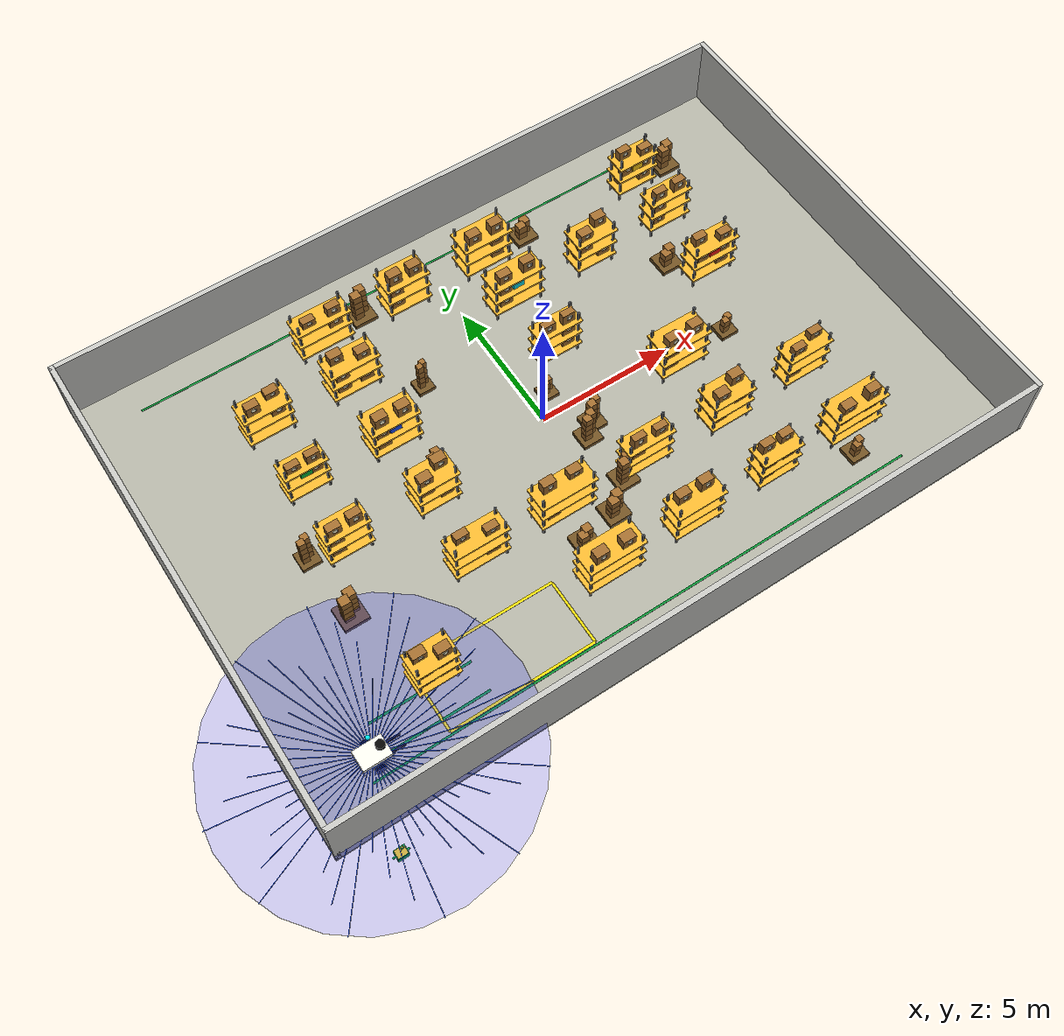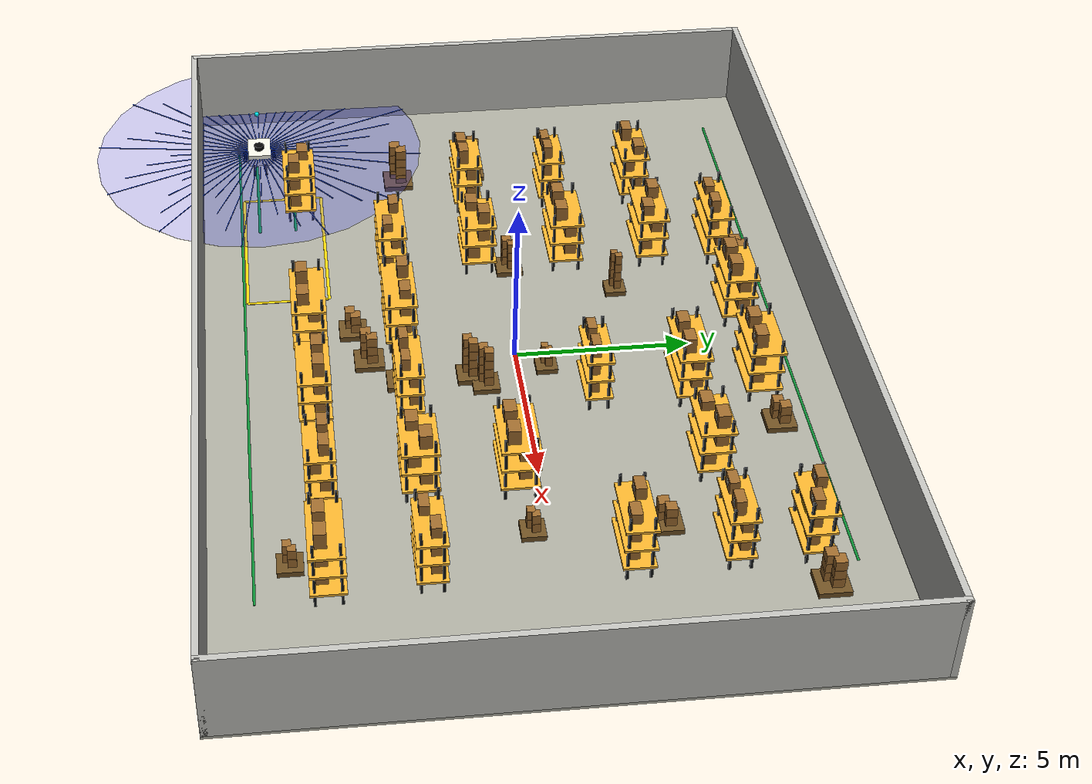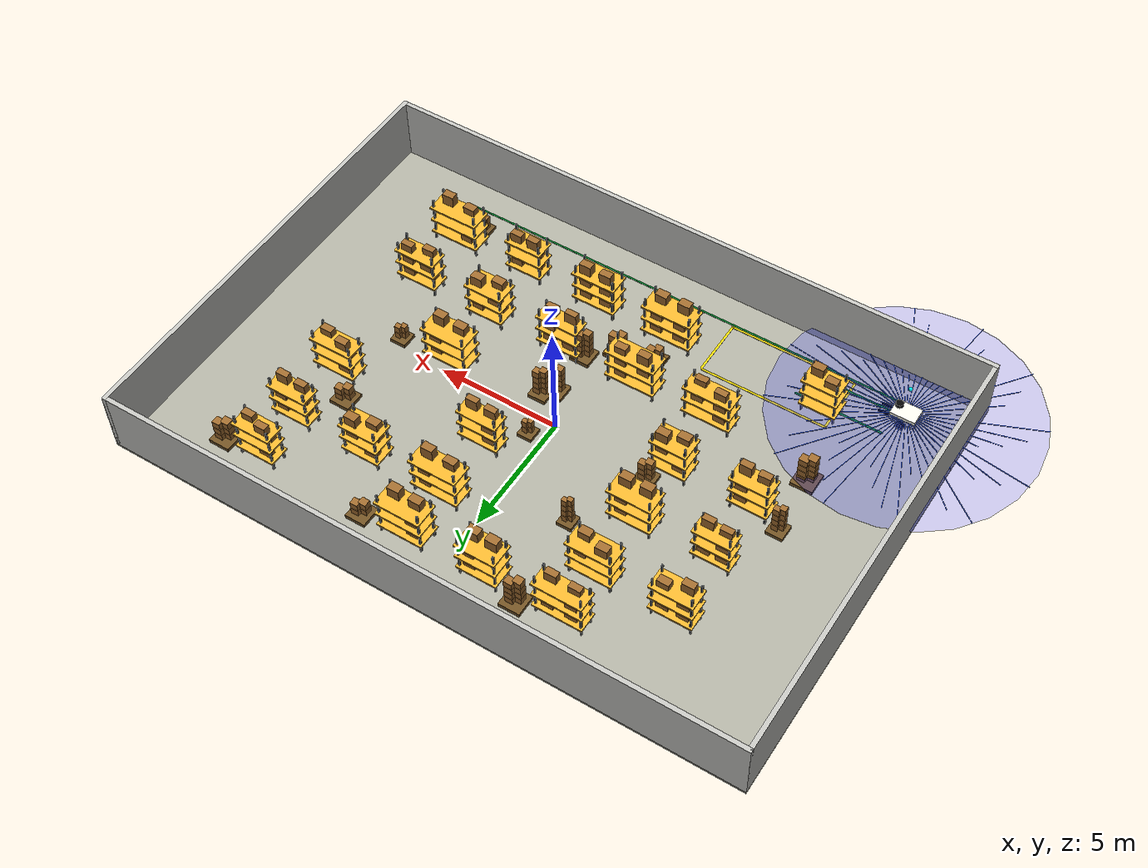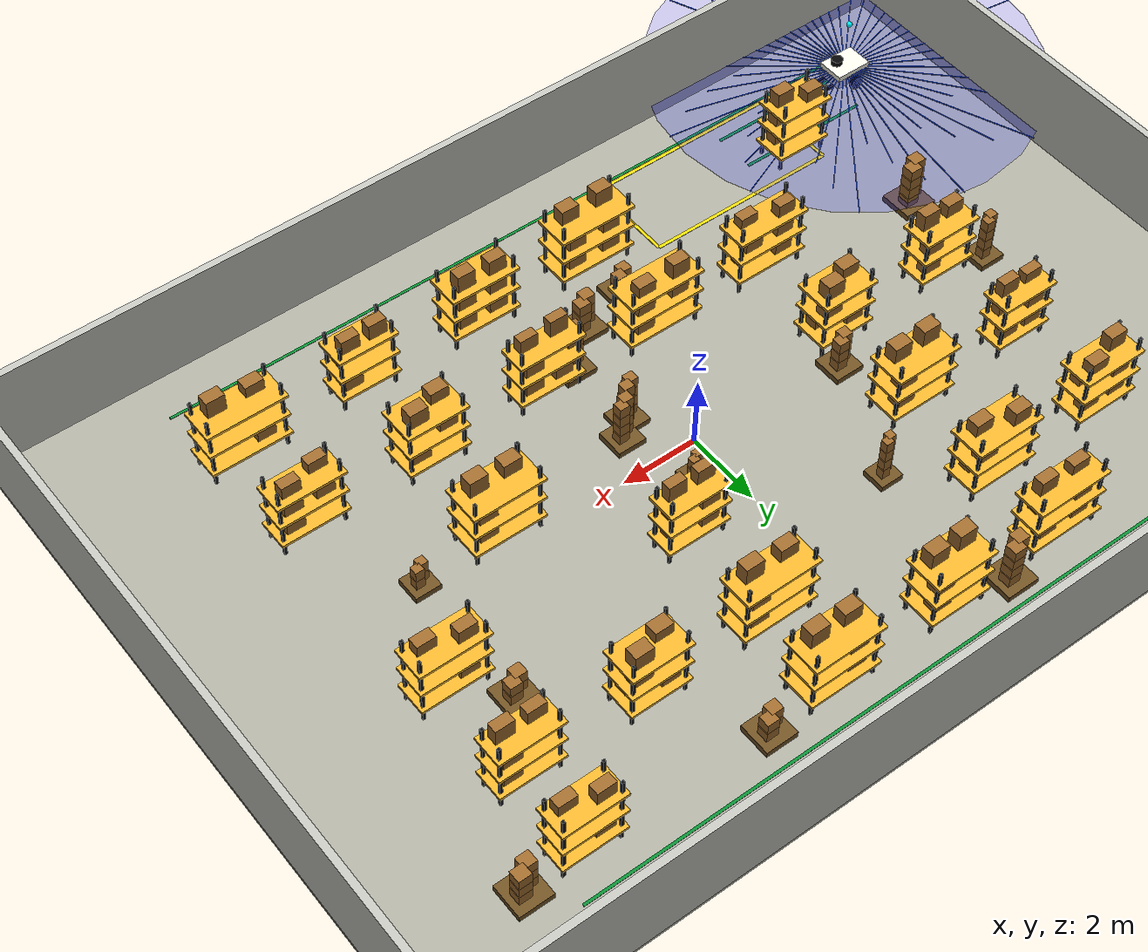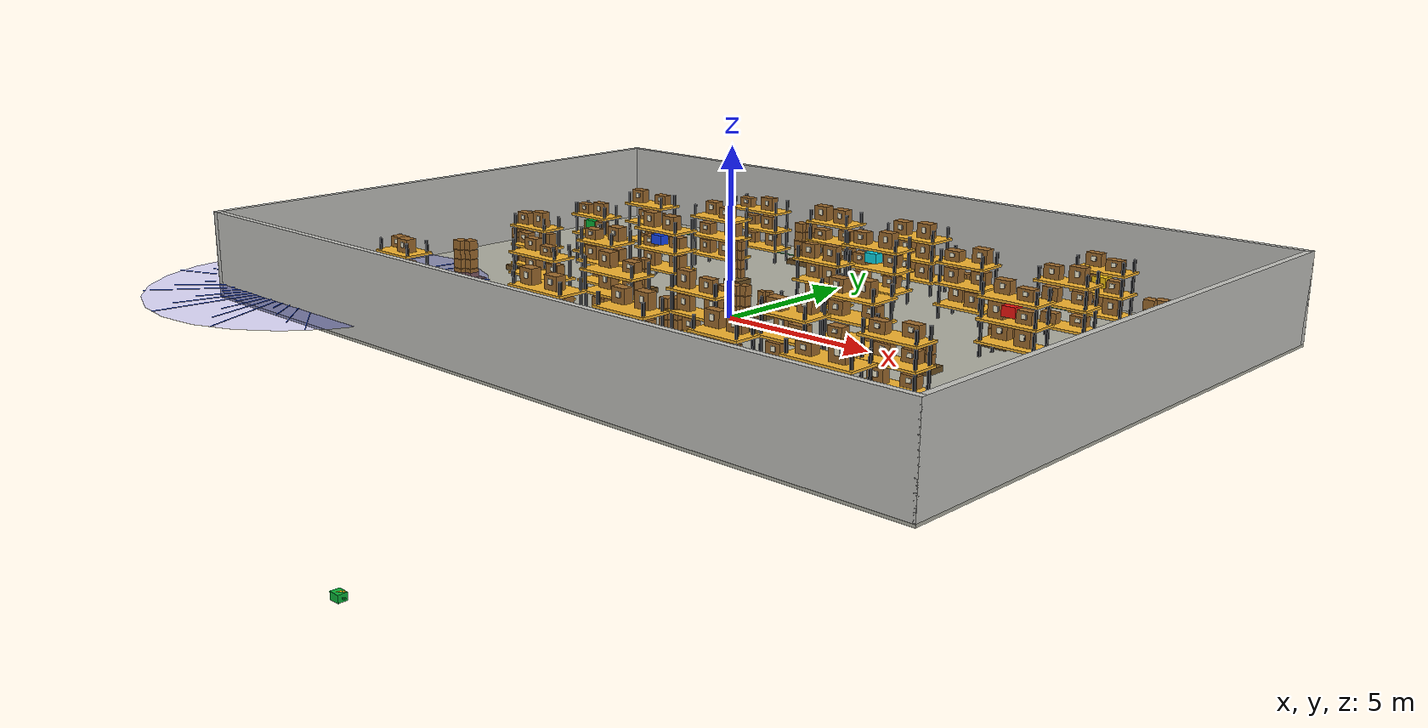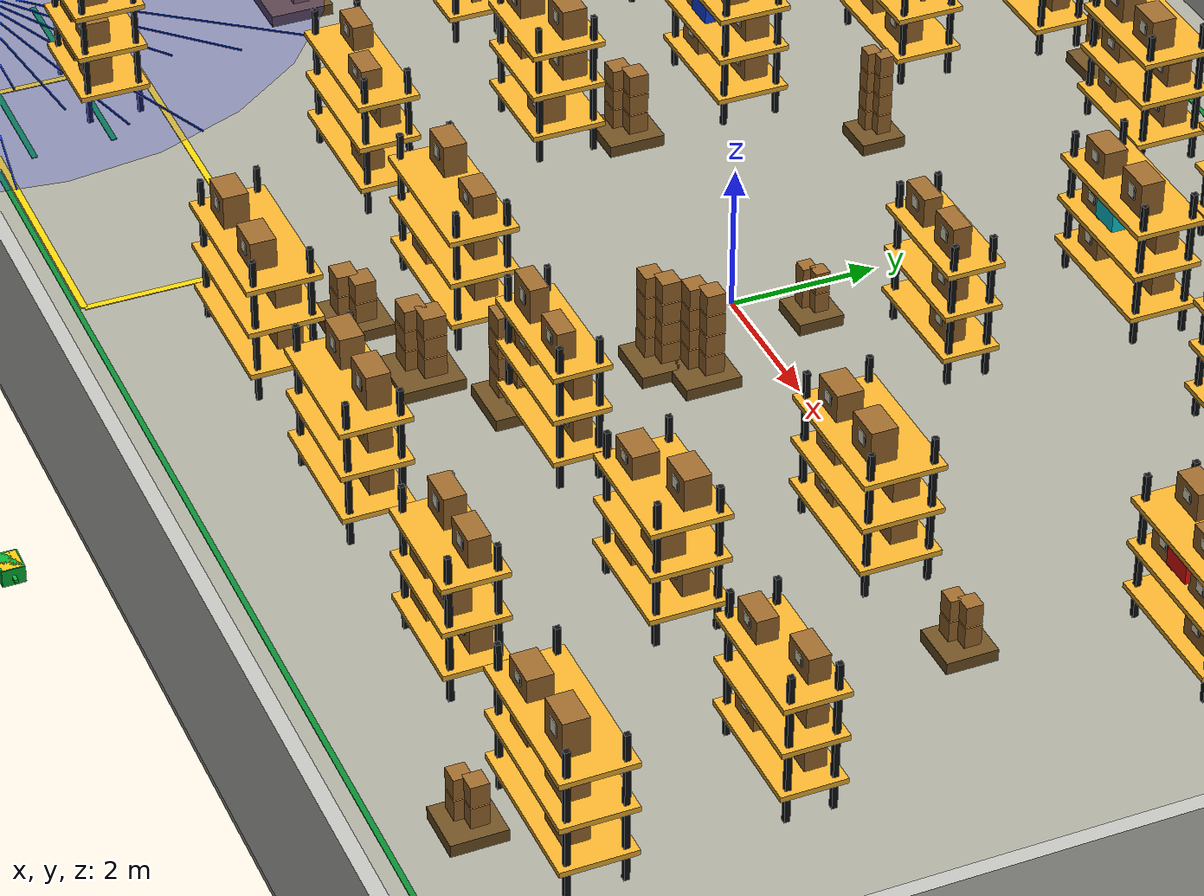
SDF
<?xml version="1.0" ?>
<sdf version="1.9">
  <world name="lidar_random_warehouse">
    <physics name="1ms" type="ignored"><max_step_size>0.01</max_step_size><real_time_factor>1.0</real_time_factor></physics>
    <plugin filename="gz-sim-physics-system" name="gz::sim::systems::Physics"/>
    <plugin filename="gz-sim-user-commands-system" name="gz::sim::systems::UserCommands"/>
    <plugin filename="gz-sim-scene-broadcaster-system" name="gz::sim::systems::SceneBroadcaster"/>
    <scene><ambient>0.66 0.66 0.66 1</ambient><background>0.04 0.05 0.06 1</background></scene>
    <gui fullscreen="1"><camera name="lidar_random_overview"><pose>0 -8 18 0 1.05 1.5708</pose><view_controller>orbit</view_controller><projection_type>perspective</projection_type></camera></gui>
    <light type="directional" name="sun"><cast_shadows>true</cast_shadows><pose>0 0 10 0 0 0</pose><diffuse>0.9 0.9 0.85 1</diffuse><direction>-0.35 0.2 -0.9</direction></light>

    <model name="floor">
      <static>true</static>
      <pose>0.000 0.000 -0.040 0 0 0</pose>
      <link name="link">
        <collision name="collision"><geometry><box><size>26.000 18.000 0.080</size></box></geometry></collision>
        <visual name="visual"><geometry><box><size>26.000 18.000 0.080</size></box></geometry><material><ambient>0.50 0.50 0.47 1</ambient><diffuse>0.68 0.68 0.63 1</diffuse></material></visual>
      </link>
    </model>
    <model name="dispatch_lane_a">
      <static>true</static>
      <pose>-8.400 -7.100 0.006 0 0 0</pose>
      <link name="link">
        <collision name="collision"><geometry><box><size>3.600 0.080 0.012</size></box></geometry></collision>
        <visual name="visual"><geometry><box><size>3.600 0.080 0.012</size></box></geometry><material><ambient>0.04 0.45 0.16 1</ambient><diffuse>0.04 0.55 0.20 1</diffuse></material></visual>
      </link>
    </model>
    <model name="dispatch_lane_b">
      <static>true</static>
      <pose>-8.400 -6.000 0.006 0 0 0</pose>
      <link name="link">
        <collision name="collision"><geometry><box><size>3.600 0.080 0.012</size></box></geometry></collision>
        <visual name="visual"><geometry><box><size>3.600 0.080 0.012</size></box></geometry><material><ambient>0.04 0.45 0.16 1</ambient><diffuse>0.04 0.55 0.20 1</diffuse></material></visual>
      </link>
    </model>
    <model name="main_aisle_left">
      <static>true</static>
      <pose>-1.000 -7.650 0.006 0 0 0</pose>
      <link name="link">
        <collision name="collision"><geometry><box><size>20.000 0.070 0.012</size></box></geometry></collision>
        <visual name="visual"><geometry><box><size>20.000 0.070 0.012</size></box></geometry><material><ambient>0.04 0.45 0.16 1</ambient><diffuse>0.04 0.55 0.20 1</diffuse></material></visual>
      </link>
    </model>
    <model name="main_aisle_right">
      <static>true</static>
      <pose>-1.000 7.650 0.006 0 0 0</pose>
      <link name="link">
        <collision name="collision"><geometry><box><size>20.000 0.070 0.012</size></box></geometry></collision>
        <visual name="visual"><geometry><box><size>20.000 0.070 0.012</size></box></geometry><material><ambient>0.04 0.45 0.16 1</ambient><diffuse>0.04 0.55 0.20 1</diffuse></material></visual>
      </link>
    </model>
    <model name="pickup_hazard_front">
      <static>true</static>
      <pose>-5.700 -7.550 0.006 0 0 0</pose>
      <link name="link">
        <collision name="collision"><geometry><box><size>5.200 0.090 0.012</size></box></geometry></collision>
        <visual name="visual"><geometry><box><size>5.200 0.090 0.012</size></box></geometry><material><ambient>0.90 0.75 0.03 1</ambient><diffuse>1.00 0.84 0.04 1</diffuse></material></visual>
      </link>
    </model>
    <model name="pickup_hazard_back">
      <static>true</static>
      <pose>-5.700 -5.150 0.006 0 0 0</pose>
      <link name="link">
        <collision name="collision"><geometry><box><size>5.200 0.090 0.012</size></box></geometry></collision>
        <visual name="visual"><geometry><box><size>5.200 0.090 0.012</size></box></geometry><material><ambient>0.90 0.75 0.03 1</ambient><diffuse>1.00 0.84 0.04 1</diffuse></material></visual>
      </link>
    </model>
    <model name="pickup_hazard_left">
      <static>true</static>
      <pose>-8.300 -6.350 0.006 0 0 0</pose>
      <link name="link">
        <collision name="collision"><geometry><box><size>0.090 2.400 0.012</size></box></geometry></collision>
        <visual name="visual"><geometry><box><size>0.090 2.400 0.012</size></box></geometry><material><ambient>0.90 0.75 0.03 1</ambient><diffuse>1.00 0.84 0.04 1</diffuse></material></visual>
      </link>
    </model>
    <model name="pickup_hazard_right">
      <static>true</static>
      <pose>-3.100 -6.350 0.006 0 0 0</pose>
      <link name="link">
        <collision name="collision"><geometry><box><size>0.090 2.400 0.012</size></box></geometry></collision>
        <visual name="visual"><geometry><box><size>0.090 2.400 0.012</size></box></geometry><material><ambient>0.90 0.75 0.03 1</ambient><diffuse>1.00 0.84 0.04 1</diffuse></material></visual>
      </link>
    </model>
    <model name="front_wall">
      <static>true</static>
      <pose>0.000 -8.910 1.300 0 0 0</pose>
      <link name="link">
        <collision name="collision"><geometry><box><size>26.000 0.180 2.600</size></box></geometry></collision>
        <visual name="visual"><geometry><box><size>26.000 0.180 2.600</size></box></geometry><material><ambient>0.66 0.66 0.64 1</ambient><diffuse>0.76 0.76 0.74 1</diffuse></material></visual>
      </link>
    </model>
    <model name="back_wall">
      <static>true</static>
      <pose>0.000 8.910 1.300 0 0 0</pose>
      <link name="link">
        <collision name="collision"><geometry><box><size>26.000 0.180 2.600</size></box></geometry></collision>
        <visual name="visual"><geometry><box><size>26.000 0.180 2.600</size></box></geometry><material><ambient>0.66 0.66 0.64 1</ambient><diffuse>0.76 0.76 0.74 1</diffuse></material></visual>
      </link>
    </model>
    <model name="left_wall">
      <static>true</static>
      <pose>-12.910 0.000 1.300 0 0 0</pose>
      <link name="link">
        <collision name="collision"><geometry><box><size>0.180 18.000 2.600</size></box></geometry></collision>
        <visual name="visual"><geometry><box><size>0.180 18.000 2.600</size></box></geometry><material><ambient>0.66 0.66 0.64 1</ambient><diffuse>0.76 0.76 0.74 1</diffuse></material></visual>
      </link>
    </model>
    <model name="right_wall">
      <static>true</static>
      <pose>12.910 0.000 1.300 0 0 0</pose>
      <link name="link">
        <collision name="collision"><geometry><box><size>0.180 18.000 2.600</size></box></geometry></collision>
        <visual name="visual"><geometry><box><size>0.180 18.000 2.600</size></box></geometry><material><ambient>0.66 0.66 0.64 1</ambient><diffuse>0.76 0.76 0.74 1</diffuse></material></visual>
      </link>
    </model>
    <model name="shelf_1">
      <static>true</static>
      <pose>-7.800 -5.800 0 0 0 0</pose>
      <link name="link">
        <collision name="collision"><pose>0 0 1.025 0 0 0</pose><geometry><box><size>1.363 0.777 2.050</size></box></geometry></collision>

        <visual name="post_0">
          <pose>-0.647 -0.354 1.025 0 0 0</pose>
          <geometry><box><size>0.070 0.070 2.050</size></box></geometry>
          <material><ambient>0.03 0.04 0.05 1</ambient><diffuse>0.05 0.06 0.07 1</diffuse></material>
        </visual>
        <visual name="post_1">
          <pose>-0.647 0.354 1.025 0 0 0</pose>
          <geometry><box><size>0.070 0.070 2.050</size></box></geometry>
          <material><ambient>0.03 0.04 0.05 1</ambient><diffuse>0.05 0.06 0.07 1</diffuse></material>
        </visual>
        <visual name="post_2">
          <pose>0.647 -0.354 1.025 0 0 0</pose>
          <geometry><box><size>0.070 0.070 2.050</size></box></geometry>
          <material><ambient>0.03 0.04 0.05 1</ambient><diffuse>0.05 0.06 0.07 1</diffuse></material>
        </visual>
        <visual name="post_3">
          <pose>0.647 0.354 1.025 0 0 0</pose>
          <geometry><box><size>0.070 0.070 2.050</size></box></geometry>
          <material><ambient>0.03 0.04 0.05 1</ambient><diffuse>0.05 0.06 0.07 1</diffuse></material>
        </visual>
        <visual name="deck_1">
          <pose>0.000 0.000 0.420 0 0 0</pose>
          <geometry><box><size>1.503 0.957 0.070</size></box></geometry>
          <material><ambient>0.70 0.52 0.18 1</ambient><diffuse>0.96 0.70 0.18 1</diffuse></material>
        </visual>
        <visual name="box_1_-0.3">
          <pose>-0.341 -0.140 0.681 0 0 0</pose>
          <geometry><box><size>0.480 0.326 0.361</size></box></geometry>
          <material><ambient>0.44 0.28 0.11 1</ambient><diffuse>0.62 0.42 0.18 1</diffuse></material>
        </visual>
        <visual name="label_1_-0.3">
          <pose>-0.341 -0.307 0.708 0 0 0</pose>
          <geometry><box><size>0.134 0.012 0.137</size></box></geometry>
          <material><ambient>0.86 0.86 0.76 1</ambient><diffuse>0.98 0.96 0.84 1</diffuse></material>
        </visual>
        <visual name="barcode_1_-0.3">
          <pose>-0.254 -0.311 0.708 0 0 0</pose>
          <geometry><box><size>0.029 0.014 0.123</size></box></geometry>
          <material><ambient>0.02 0.02 0.02 1</ambient><diffuse>0.02 0.02 0.02 1</diffuse></material>
        </visual>
        <visual name="box_1_0.3">
          <pose>0.341 -0.140 0.740 0 0 0</pose>
          <geometry><box><size>0.480 0.326 0.479</size></box></geometry>
          <material><ambient>0.44 0.28 0.11 1</ambient><diffuse>0.62 0.42 0.18 1</diffuse></material>
        </visual>
        <visual name="label_1_0.3">
          <pose>0.341 -0.307 0.769 0 0 0</pose>
          <geometry><box><size>0.134 0.012 0.182</size></box></geometry>
          <material><ambient>0.86 0.86 0.76 1</ambient><diffuse>0.98 0.96 0.84 1</diffuse></material>
        </visual>
        <visual name="barcode_1_0.3">
          <pose>0.427 -0.311 0.769 0 0 0</pose>
          <geometry><box><size>0.029 0.014 0.163</size></box></geometry>
          <material><ambient>0.02 0.02 0.02 1</ambient><diffuse>0.02 0.02 0.02 1</diffuse></material>
        </visual>
        <visual name="deck_2">
          <pose>0.000 0.000 1.040 0 0 0</pose>
          <geometry><box><size>1.503 0.957 0.070</size></box></geometry>
          <material><ambient>0.70 0.52 0.18 1</ambient><diffuse>0.96 0.70 0.18 1</diffuse></material>
        </visual>
        <visual name="box_2_-0.3">
          <pose>-0.341 -0.140 1.324 0 0 0</pose>
          <geometry><box><size>0.480 0.326 0.407</size></box></geometry>
          <material><ambient>0.44 0.28 0.11 1</ambient><diffuse>0.62 0.42 0.18 1</diffuse></material>
        </visual>
        <visual name="label_2_-0.3">
          <pose>-0.341 -0.307 1.352 0 0 0</pose>
          <geometry><box><size>0.134 0.012 0.155</size></box></geometry>
          <material><ambient>0.86 0.86 0.76 1</ambient><diffuse>0.98 0.96 0.84 1</diffuse></material>
        </visual>
        <visual name="barcode_2_-0.3">
          <pose>-0.254 -0.311 1.352 0 0 0</pose>
          <geometry><box><size>0.029 0.014 0.138</size></box></geometry>
          <material><ambient>0.02 0.02 0.02 1</ambient><diffuse>0.02 0.02 0.02 1</diffuse></material>
        </visual>
        <visual name="box_2_0.3">
          <pose>0.341 -0.140 1.290 0 0 0</pose>
          <geometry><box><size>0.480 0.326 0.339</size></box></geometry>
          <material><ambient>0.44 0.28 0.11 1</ambient><diffuse>0.62 0.42 0.18 1</diffuse></material>
        </visual>
        <visual name="label_2_0.3">
          <pose>0.341 -0.307 1.316 0 0 0</pose>
          <geometry><box><size>0.134 0.012 0.129</size></box></geometry>
          <material><ambient>0.86 0.86 0.76 1</ambient><diffuse>0.98 0.96 0.84 1</diffuse></material>
        </visual>
        <visual name="barcode_2_0.3">
          <pose>0.427 -0.311 1.316 0 0 0</pose>
          <geometry><box><size>0.029 0.014 0.115</size></box></geometry>
          <material><ambient>0.02 0.02 0.02 1</ambient><diffuse>0.02 0.02 0.02 1</diffuse></material>
        </visual>
        <visual name="deck_3">
          <pose>0.000 0.000 1.660 0 0 0</pose>
          <geometry><box><size>1.503 0.957 0.070</size></box></geometry>
          <material><ambient>0.70 0.52 0.18 1</ambient><diffuse>0.96 0.70 0.18 1</diffuse></material>
        </visual>
        <visual name="box_3_-0.3">
          <pose>-0.341 0.140 1.900 0 0 0</pose>
          <geometry><box><size>0.480 0.326 0.320</size></box></geometry>
          <material><ambient>0.44 0.28 0.11 1</ambient><diffuse>0.62 0.42 0.18 1</diffuse></material>
        </visual>
        <visual name="label_3_-0.3">
          <pose>-0.341 -0.027 1.927 0 0 0</pose>
          <geometry><box><size>0.134 0.012 0.122</size></box></geometry>
          <material><ambient>0.86 0.86 0.76 1</ambient><diffuse>0.98 0.96 0.84 1</diffuse></material>
        </visual>
        <visual name="barcode_3_-0.3">
          <pose>-0.254 -0.031 1.927 0 0 0</pose>
          <geometry><box><size>0.029 0.014 0.109</size></box></geometry>
          <material><ambient>0.02 0.02 0.02 1</ambient><diffuse>0.02 0.02 0.02 1</diffuse></material>
        </visual>
        <visual name="box_3_0.3">
          <pose>0.341 -0.140 1.940 0 0 0</pose>
          <geometry><box><size>0.480 0.326 0.400</size></box></geometry>
          <material><ambient>0.44 0.28 0.11 1</ambient><diffuse>0.62 0.42 0.18 1</diffuse></material>
        </visual>
        <visual name="label_3_0.3">
          <pose>0.341 -0.307 1.968 0 0 0</pose>
          <geometry><box><size>0.134 0.012 0.152</size></box></geometry>
          <material><ambient>0.86 0.86 0.76 1</ambient><diffuse>0.98 0.96 0.84 1</diffuse></material>
        </visual>
        <visual name="barcode_3_0.3">
          <pose>0.427 -0.311 1.968 0 0 0</pose>
          <geometry><box><size>0.029 0.014 0.136</size></box></geometry>
          <material><ambient>0.02 0.02 0.02 1</ambient><diffuse>0.02 0.02 0.02 1</diffuse></material>
        </visual>
      </link>
    </model>
    <model name="shelf_2">
      <static>true</static>
      <pose>-1.400 -5.800 0 0 0 0</pose>
      <link name="link">
        <collision name="collision"><pose>0 0 1.025 0 0 0</pose><geometry><box><size>1.958 0.805 2.050</size></box></geometry></collision>

        <visual name="post_0">
          <pose>-0.944 -0.367 1.025 0 0 0</pose>
          <geometry><box><size>0.070 0.070 2.050</size></box></geometry>
          <material><ambient>0.03 0.04 0.05 1</ambient><diffuse>0.05 0.06 0.07 1</diffuse></material>
        </visual>
        <visual name="post_1">
          <pose>-0.944 0.367 1.025 0 0 0</pose>
          <geometry><box><size>0.070 0.070 2.050</size></box></geometry>
          <material><ambient>0.03 0.04 0.05 1</ambient><diffuse>0.05 0.06 0.07 1</diffuse></material>
        </visual>
        <visual name="post_2">
          <pose>0.944 -0.367 1.025 0 0 0</pose>
          <geometry><box><size>0.070 0.070 2.050</size></box></geometry>
          <material><ambient>0.03 0.04 0.05 1</ambient><diffuse>0.05 0.06 0.07 1</diffuse></material>
        </visual>
        <visual name="post_3">
          <pose>0.944 0.367 1.025 0 0 0</pose>
          <geometry><box><size>0.070 0.070 2.050</size></box></geometry>
          <material><ambient>0.03 0.04 0.05 1</ambient><diffuse>0.05 0.06 0.07 1</diffuse></material>
        </visual>
        <visual name="deck_1">
          <pose>0.000 0.000 0.420 0 0 0</pose>
          <geometry><box><size>2.098 0.985 0.070</size></box></geometry>
          <material><ambient>0.70 0.52 0.18 1</ambient><diffuse>0.96 0.70 0.18 1</diffuse></material>
        </visual>
        <visual name="box_1_-0.5">
          <pose>-0.490 0.145 0.661 0 0 0</pose>
          <geometry><box><size>0.480 0.338 0.321</size></box></geometry>
          <material><ambient>0.44 0.28 0.11 1</ambient><diffuse>0.62 0.42 0.18 1</diffuse></material>
        </visual>
        <visual name="label_1_-0.5">
          <pose>-0.490 -0.028 0.687 0 0 0</pose>
          <geometry><box><size>0.134 0.012 0.122</size></box></geometry>
          <material><ambient>0.86 0.86 0.76 1</ambient><diffuse>0.98 0.96 0.84 1</diffuse></material>
        </visual>
        <visual name="barcode_1_-0.5">
          <pose>-0.403 -0.032 0.687 0 0 0</pose>
          <geometry><box><size>0.029 0.014 0.109</size></box></geometry>
          <material><ambient>0.02 0.02 0.02 1</ambient><diffuse>0.02 0.02 0.02 1</diffuse></material>
        </visual>
        <visual name="box_1_0.5">
          <pose>0.490 0.145 0.681 0 0 0</pose>
          <geometry><box><size>0.480 0.338 0.361</size></box></geometry>
          <material><ambient>0.44 0.28 0.11 1</ambient><diffuse>0.62 0.42 0.18 1</diffuse></material>
        </visual>
        <visual name="label_1_0.5">
          <pose>0.490 -0.028 0.708 0 0 0</pose>
          <geometry><box><size>0.134 0.012 0.137</size></box></geometry>
          <material><ambient>0.86 0.86 0.76 1</ambient><diffuse>0.98 0.96 0.84 1</diffuse></material>
        </visual>
        <visual name="barcode_1_0.5">
          <pose>0.576 -0.032 0.708 0 0 0</pose>
          <geometry><box><size>0.029 0.014 0.123</size></box></geometry>
          <material><ambient>0.02 0.02 0.02 1</ambient><diffuse>0.02 0.02 0.02 1</diffuse></material>
        </visual>
        <visual name="deck_2">
          <pose>0.000 0.000 1.040 0 0 0</pose>
          <geometry><box><size>2.098 0.985 0.070</size></box></geometry>
          <material><ambient>0.70 0.52 0.18 1</ambient><diffuse>0.96 0.70 0.18 1</diffuse></material>
        </visual>
        <visual name="box_2_-0.5">
          <pose>-0.490 0.145 1.333 0 0 0</pose>
          <geometry><box><size>0.480 0.338 0.427</size></box></geometry>
          <material><ambient>0.44 0.28 0.11 1</ambient><diffuse>0.62 0.42 0.18 1</diffuse></material>
        </visual>
        <visual name="label_2_-0.5">
          <pose>-0.490 -0.028 1.362 0 0 0</pose>
          <geometry><box><size>0.134 0.012 0.162</size></box></geometry>
          <material><ambient>0.86 0.86 0.76 1</ambient><diffuse>0.98 0.96 0.84 1</diffuse></material>
        </visual>
        <visual name="barcode_2_-0.5">
          <pose>-0.403 -0.032 1.362 0 0 0</pose>
          <geometry><box><size>0.029 0.014 0.145</size></box></geometry>
          <material><ambient>0.02 0.02 0.02 1</ambient><diffuse>0.02 0.02 0.02 1</diffuse></material>
        </visual>
        <visual name="box_2_0.5">
          <pose>0.490 0.145 1.355 0 0 0</pose>
          <geometry><box><size>0.480 0.338 0.471</size></box></geometry>
          <material><ambient>0.44 0.28 0.11 1</ambient><diffuse>0.62 0.42 0.18 1</diffuse></material>
        </visual>
        <visual name="label_2_0.5">
          <pose>0.490 -0.028 1.385 0 0 0</pose>
          <geometry><box><size>0.134 0.012 0.179</size></box></geometry>
          <material><ambient>0.86 0.86 0.76 1</ambient><diffuse>0.98 0.96 0.84 1</diffuse></material>
        </visual>
        <visual name="barcode_2_0.5">
          <pose>0.576 -0.032 1.385 0 0 0</pose>
          <geometry><box><size>0.029 0.014 0.160</size></box></geometry>
          <material><ambient>0.02 0.02 0.02 1</ambient><diffuse>0.02 0.02 0.02 1</diffuse></material>
        </visual>
        <visual name="deck_3">
          <pose>0.000 0.000 1.660 0 0 0</pose>
          <geometry><box><size>2.098 0.985 0.070</size></box></geometry>
          <material><ambient>0.70 0.52 0.18 1</ambient><diffuse>0.96 0.70 0.18 1</diffuse></material>
        </visual>
        <visual name="box_3_-0.5">
          <pose>-0.490 -0.145 1.966 0 0 0</pose>
          <geometry><box><size>0.480 0.338 0.451</size></box></geometry>
          <material><ambient>0.44 0.28 0.11 1</ambient><diffuse>0.62 0.42 0.18 1</diffuse></material>
        </visual>
        <visual name="label_3_-0.5">
          <pose>-0.490 -0.318 1.995 0 0 0</pose>
          <geometry><box><size>0.134 0.012 0.171</size></box></geometry>
          <material><ambient>0.86 0.86 0.76 1</ambient><diffuse>0.98 0.96 0.84 1</diffuse></material>
        </visual>
        <visual name="barcode_3_-0.5">
          <pose>-0.403 -0.322 1.995 0 0 0</pose>
          <geometry><box><size>0.029 0.014 0.153</size></box></geometry>
          <material><ambient>0.02 0.02 0.02 1</ambient><diffuse>0.02 0.02 0.02 1</diffuse></material>
        </visual>
        <visual name="box_3_0.5">
          <pose>0.490 -0.145 1.941 0 0 0</pose>
          <geometry><box><size>0.480 0.338 0.402</size></box></geometry>
          <material><ambient>0.44 0.28 0.11 1</ambient><diffuse>0.62 0.42 0.18 1</diffuse></material>
        </visual>
        <visual name="label_3_0.5">
          <pose>0.490 -0.318 1.969 0 0 0</pose>
          <geometry><box><size>0.134 0.012 0.153</size></box></geometry>
          <material><ambient>0.86 0.86 0.76 1</ambient><diffuse>0.98 0.96 0.84 1</diffuse></material>
        </visual>
        <visual name="barcode_3_0.5">
          <pose>0.576 -0.322 1.969 0 0 0</pose>
          <geometry><box><size>0.029 0.014 0.137</size></box></geometry>
          <material><ambient>0.02 0.02 0.02 1</ambient><diffuse>0.02 0.02 0.02 1</diffuse></material>
        </visual>
      </link>
    </model>
    <model name="shelf_3">
      <static>true</static>
      <pose>1.800 -5.800 0 0 0 0</pose>
      <link name="link">
        <collision name="collision"><pose>0 0 1.025 0 0 0</pose><geometry><box><size>1.716 0.743 2.050</size></box></geometry></collision>

        <visual name="post_0">
          <pose>-0.823 -0.336 1.025 0 0 0</pose>
          <geometry><box><size>0.070 0.070 2.050</size></box></geometry>
          <material><ambient>0.03 0.04 0.05 1</ambient><diffuse>0.05 0.06 0.07 1</diffuse></material>
        </visual>
        <visual name="post_1">
          <pose>-0.823 0.336 1.025 0 0 0</pose>
          <geometry><box><size>0.070 0.070 2.050</size></box></geometry>
          <material><ambient>0.03 0.04 0.05 1</ambient><diffuse>0.05 0.06 0.07 1</diffuse></material>
        </visual>
        <visual name="post_2">
          <pose>0.823 -0.336 1.025 0 0 0</pose>
          <geometry><box><size>0.070 0.070 2.050</size></box></geometry>
          <material><ambient>0.03 0.04 0.05 1</ambient><diffuse>0.05 0.06 0.07 1</diffuse></material>
        </visual>
        <visual name="post_3">
          <pose>0.823 0.336 1.025 0 0 0</pose>
          <geometry><box><size>0.070 0.070 2.050</size></box></geometry>
          <material><ambient>0.03 0.04 0.05 1</ambient><diffuse>0.05 0.06 0.07 1</diffuse></material>
        </visual>
        <visual name="deck_1">
          <pose>0.000 0.000 0.420 0 0 0</pose>
          <geometry><box><size>1.856 0.923 0.070</size></box></geometry>
          <material><ambient>0.70 0.52 0.18 1</ambient><diffuse>0.96 0.70 0.18 1</diffuse></material>
        </visual>
        <visual name="box_1_-0.4">
          <pose>-0.429 0.134 0.643 0 0 0</pose>
          <geometry><box><size>0.480 0.312 0.286</size></box></geometry>
          <material><ambient>0.44 0.28 0.11 1</ambient><diffuse>0.62 0.42 0.18 1</diffuse></material>
        </visual>
        <visual name="label_1_-0.4">
          <pose>-0.429 -0.026 0.669 0 0 0</pose>
          <geometry><box><size>0.134 0.012 0.109</size></box></geometry>
          <material><ambient>0.86 0.86 0.76 1</ambient><diffuse>0.98 0.96 0.84 1</diffuse></material>
        </visual>
        <visual name="barcode_1_-0.4">
          <pose>-0.343 -0.030 0.669 0 0 0</pose>
          <geometry><box><size>0.029 0.014 0.097</size></box></geometry>
          <material><ambient>0.02 0.02 0.02 1</ambient><diffuse>0.02 0.02 0.02 1</diffuse></material>
        </visual>
        <visual name="box_1_0.4">
          <pose>0.429 0.134 0.715 0 0 0</pose>
          <geometry><box><size>0.480 0.312 0.429</size></box></geometry>
          <material><ambient>0.44 0.28 0.11 1</ambient><diffuse>0.62 0.42 0.18 1</diffuse></material>
        </visual>
        <visual name="label_1_0.4">
          <pose>0.429 -0.026 0.743 0 0 0</pose>
          <geometry><box><size>0.134 0.012 0.163</size></box></geometry>
          <material><ambient>0.86 0.86 0.76 1</ambient><diffuse>0.98 0.96 0.84 1</diffuse></material>
        </visual>
        <visual name="barcode_1_0.4">
          <pose>0.515 -0.030 0.743 0 0 0</pose>
          <geometry><box><size>0.029 0.014 0.146</size></box></geometry>
          <material><ambient>0.02 0.02 0.02 1</ambient><diffuse>0.02 0.02 0.02 1</diffuse></material>
        </visual>
        <visual name="deck_2">
          <pose>0.000 0.000 1.040 0 0 0</pose>
          <geometry><box><size>1.856 0.923 0.070</size></box></geometry>
          <material><ambient>0.70 0.52 0.18 1</ambient><diffuse>0.96 0.70 0.18 1</diffuse></material>
        </visual>
        <visual name="box_2_-0.4">
          <pose>-0.429 0.134 1.332 0 0 0</pose>
          <geometry><box><size>0.480 0.312 0.424</size></box></geometry>
          <material><ambient>0.44 0.28 0.11 1</ambient><diffuse>0.62 0.42 0.18 1</diffuse></material>
        </visual>
        <visual name="label_2_-0.4">
          <pose>-0.429 -0.026 1.360 0 0 0</pose>
          <geometry><box><size>0.134 0.012 0.161</size></box></geometry>
          <material><ambient>0.86 0.86 0.76 1</ambient><diffuse>0.98 0.96 0.84 1</diffuse></material>
        </visual>
        <visual name="barcode_2_-0.4">
          <pose>-0.343 -0.030 1.360 0 0 0</pose>
          <geometry><box><size>0.029 0.014 0.144</size></box></geometry>
          <material><ambient>0.02 0.02 0.02 1</ambient><diffuse>0.02 0.02 0.02 1</diffuse></material>
        </visual>
        <visual name="box_2_0.4">
          <pose>0.429 0.134 1.300 0 0 0</pose>
          <geometry><box><size>0.480 0.312 0.360</size></box></geometry>
          <material><ambient>0.44 0.28 0.11 1</ambient><diffuse>0.62 0.42 0.18 1</diffuse></material>
        </visual>
        <visual name="label_2_0.4">
          <pose>0.429 -0.026 1.327 0 0 0</pose>
          <geometry><box><size>0.134 0.012 0.137</size></box></geometry>
          <material><ambient>0.86 0.86 0.76 1</ambient><diffuse>0.98 0.96 0.84 1</diffuse></material>
        </visual>
        <visual name="barcode_2_0.4">
          <pose>0.515 -0.030 1.327 0 0 0</pose>
          <geometry><box><size>0.029 0.014 0.122</size></box></geometry>
          <material><ambient>0.02 0.02 0.02 1</ambient><diffuse>0.02 0.02 0.02 1</diffuse></material>
        </visual>
        <visual name="deck_3">
          <pose>0.000 0.000 1.660 0 0 0</pose>
          <geometry><box><size>1.856 0.923 0.070</size></box></geometry>
          <material><ambient>0.70 0.52 0.18 1</ambient><diffuse>0.96 0.70 0.18 1</diffuse></material>
        </visual>
        <visual name="box_3_-0.4">
          <pose>-0.429 0.134 1.952 0 0 0</pose>
          <geometry><box><size>0.480 0.312 0.423</size></box></geometry>
          <material><ambient>0.44 0.28 0.11 1</ambient><diffuse>0.62 0.42 0.18 1</diffuse></material>
        </visual>
        <visual name="label_3_-0.4">
          <pose>-0.429 -0.026 1.980 0 0 0</pose>
          <geometry><box><size>0.134 0.012 0.161</size></box></geometry>
          <material><ambient>0.86 0.86 0.76 1</ambient><diffuse>0.98 0.96 0.84 1</diffuse></material>
        </visual>
        <visual name="barcode_3_-0.4">
          <pose>-0.343 -0.030 1.980 0 0 0</pose>
          <geometry><box><size>0.029 0.014 0.144</size></box></geometry>
          <material><ambient>0.02 0.02 0.02 1</ambient><diffuse>0.02 0.02 0.02 1</diffuse></material>
        </visual>
        <visual name="box_3_0.4">
          <pose>0.429 0.134 1.972 0 0 0</pose>
          <geometry><box><size>0.480 0.312 0.464</size></box></geometry>
          <material><ambient>0.44 0.28 0.11 1</ambient><diffuse>0.62 0.42 0.18 1</diffuse></material>
        </visual>
        <visual name="label_3_0.4">
          <pose>0.429 -0.026 2.001 0 0 0</pose>
          <geometry><box><size>0.134 0.012 0.176</size></box></geometry>
          <material><ambient>0.86 0.86 0.76 1</ambient><diffuse>0.98 0.96 0.84 1</diffuse></material>
        </visual>
        <visual name="barcode_3_0.4">
          <pose>0.515 -0.030 2.001 0 0 0</pose>
          <geometry><box><size>0.029 0.014 0.158</size></box></geometry>
          <material><ambient>0.02 0.02 0.02 1</ambient><diffuse>0.02 0.02 0.02 1</diffuse></material>
        </visual>
      </link>
    </model>
    <model name="shelf_4">
      <static>true</static>
      <pose>5.000 -5.800 0 0 0 0</pose>
      <link name="link">
        <collision name="collision"><pose>0 0 1.025 0 0 0</pose><geometry><box><size>1.454 0.663 2.050</size></box></geometry></collision>

        <visual name="post_0">
          <pose>-0.692 -0.297 1.025 0 0 0</pose>
          <geometry><box><size>0.070 0.070 2.050</size></box></geometry>
          <material><ambient>0.03 0.04 0.05 1</ambient><diffuse>0.05 0.06 0.07 1</diffuse></material>
        </visual>
        <visual name="post_1">
          <pose>-0.692 0.297 1.025 0 0 0</pose>
          <geometry><box><size>0.070 0.070 2.050</size></box></geometry>
          <material><ambient>0.03 0.04 0.05 1</ambient><diffuse>0.05 0.06 0.07 1</diffuse></material>
        </visual>
        <visual name="post_2">
          <pose>0.692 -0.297 1.025 0 0 0</pose>
          <geometry><box><size>0.070 0.070 2.050</size></box></geometry>
          <material><ambient>0.03 0.04 0.05 1</ambient><diffuse>0.05 0.06 0.07 1</diffuse></material>
        </visual>
        <visual name="post_3">
          <pose>0.692 0.297 1.025 0 0 0</pose>
          <geometry><box><size>0.070 0.070 2.050</size></box></geometry>
          <material><ambient>0.03 0.04 0.05 1</ambient><diffuse>0.05 0.06 0.07 1</diffuse></material>
        </visual>
        <visual name="deck_1">
          <pose>0.000 0.000 0.420 0 0 0</pose>
          <geometry><box><size>1.594 0.843 0.070</size></box></geometry>
          <material><ambient>0.70 0.52 0.18 1</ambient><diffuse>0.96 0.70 0.18 1</diffuse></material>
        </visual>
        <visual name="box_1_-0.4">
          <pose>-0.363 -0.119 0.703 0 0 0</pose>
          <geometry><box><size>0.480 0.279 0.406</size></box></geometry>
          <material><ambient>0.44 0.28 0.11 1</ambient><diffuse>0.62 0.42 0.18 1</diffuse></material>
        </visual>
        <visual name="label_1_-0.4">
          <pose>-0.363 -0.263 0.731 0 0 0</pose>
          <geometry><box><size>0.134 0.012 0.154</size></box></geometry>
          <material><ambient>0.86 0.86 0.76 1</ambient><diffuse>0.98 0.96 0.84 1</diffuse></material>
        </visual>
        <visual name="barcode_1_-0.4">
          <pose>-0.277 -0.267 0.731 0 0 0</pose>
          <geometry><box><size>0.029 0.014 0.138</size></box></geometry>
          <material><ambient>0.02 0.02 0.02 1</ambient><diffuse>0.02 0.02 0.02 1</diffuse></material>
        </visual>
        <visual name="box_1_0.4">
          <pose>0.363 0.119 0.707 0 0 0</pose>
          <geometry><box><size>0.480 0.279 0.415</size></box></geometry>
          <material><ambient>0.44 0.28 0.11 1</ambient><diffuse>0.62 0.42 0.18 1</diffuse></material>
        </visual>
        <visual name="label_1_0.4">
          <pose>0.363 -0.024 0.736 0 0 0</pose>
          <geometry><box><size>0.134 0.012 0.158</size></box></geometry>
          <material><ambient>0.86 0.86 0.76 1</ambient><diffuse>0.98 0.96 0.84 1</diffuse></material>
        </visual>
        <visual name="barcode_1_0.4">
          <pose>0.450 -0.028 0.736 0 0 0</pose>
          <geometry><box><size>0.029 0.014 0.141</size></box></geometry>
          <material><ambient>0.02 0.02 0.02 1</ambient><diffuse>0.02 0.02 0.02 1</diffuse></material>
        </visual>
        <visual name="deck_2">
          <pose>0.000 0.000 1.040 0 0 0</pose>
          <geometry><box><size>1.594 0.843 0.070</size></box></geometry>
          <material><ambient>0.70 0.52 0.18 1</ambient><diffuse>0.96 0.70 0.18 1</diffuse></material>
        </visual>
        <visual name="box_2_-0.4">
          <pose>-0.363 -0.119 1.318 0 0 0</pose>
          <geometry><box><size>0.480 0.279 0.396</size></box></geometry>
          <material><ambient>0.44 0.28 0.11 1</ambient><diffuse>0.62 0.42 0.18 1</diffuse></material>
        </visual>
        <visual name="label_2_-0.4">
          <pose>-0.363 -0.263 1.346 0 0 0</pose>
          <geometry><box><size>0.134 0.012 0.150</size></box></geometry>
          <material><ambient>0.86 0.86 0.76 1</ambient><diffuse>0.98 0.96 0.84 1</diffuse></material>
        </visual>
        <visual name="barcode_2_-0.4">
          <pose>-0.277 -0.267 1.346 0 0 0</pose>
          <geometry><box><size>0.029 0.014 0.135</size></box></geometry>
          <material><ambient>0.02 0.02 0.02 1</ambient><diffuse>0.02 0.02 0.02 1</diffuse></material>
        </visual>
        <visual name="box_2_0.4">
          <pose>0.363 -0.119 1.307 0 0 0</pose>
          <geometry><box><size>0.480 0.279 0.375</size></box></geometry>
          <material><ambient>0.44 0.28 0.11 1</ambient><diffuse>0.62 0.42 0.18 1</diffuse></material>
        </visual>
        <visual name="label_2_0.4">
          <pose>0.363 -0.263 1.335 0 0 0</pose>
          <geometry><box><size>0.134 0.012 0.142</size></box></geometry>
          <material><ambient>0.86 0.86 0.76 1</ambient><diffuse>0.98 0.96 0.84 1</diffuse></material>
        </visual>
        <visual name="barcode_2_0.4">
          <pose>0.450 -0.267 1.335 0 0 0</pose>
          <geometry><box><size>0.029 0.014 0.127</size></box></geometry>
          <material><ambient>0.02 0.02 0.02 1</ambient><diffuse>0.02 0.02 0.02 1</diffuse></material>
        </visual>
        <visual name="deck_3">
          <pose>0.000 0.000 1.660 0 0 0</pose>
          <geometry><box><size>1.594 0.843 0.070</size></box></geometry>
          <material><ambient>0.70 0.52 0.18 1</ambient><diffuse>0.96 0.70 0.18 1</diffuse></material>
        </visual>
        <visual name="box_3_-0.4">
          <pose>-0.363 0.119 1.956 0 0 0</pose>
          <geometry><box><size>0.480 0.279 0.432</size></box></geometry>
          <material><ambient>0.44 0.28 0.11 1</ambient><diffuse>0.62 0.42 0.18 1</diffuse></material>
        </visual>
        <visual name="label_3_-0.4">
          <pose>-0.363 -0.024 1.985 0 0 0</pose>
          <geometry><box><size>0.134 0.012 0.164</size></box></geometry>
          <material><ambient>0.86 0.86 0.76 1</ambient><diffuse>0.98 0.96 0.84 1</diffuse></material>
        </visual>
        <visual name="barcode_3_-0.4">
          <pose>-0.277 -0.028 1.985 0 0 0</pose>
          <geometry><box><size>0.029 0.014 0.147</size></box></geometry>
          <material><ambient>0.02 0.02 0.02 1</ambient><diffuse>0.02 0.02 0.02 1</diffuse></material>
        </visual>
        <visual name="box_3_0.4">
          <pose>0.363 0.119 1.933 0 0 0</pose>
          <geometry><box><size>0.480 0.279 0.385</size></box></geometry>
          <material><ambient>0.44 0.28 0.11 1</ambient><diffuse>0.62 0.42 0.18 1</diffuse></material>
        </visual>
        <visual name="label_3_0.4">
          <pose>0.363 -0.024 1.960 0 0 0</pose>
          <geometry><box><size>0.134 0.012 0.146</size></box></geometry>
          <material><ambient>0.86 0.86 0.76 1</ambient><diffuse>0.98 0.96 0.84 1</diffuse></material>
        </visual>
        <visual name="barcode_3_0.4">
          <pose>0.450 -0.028 1.960 0 0 0</pose>
          <geometry><box><size>0.029 0.014 0.131</size></box></geometry>
          <material><ambient>0.02 0.02 0.02 1</ambient><diffuse>0.02 0.02 0.02 1</diffuse></material>
        </visual>
      </link>
    </model>
    <model name="shelf_5">
      <static>true</static>
      <pose>8.200 -5.800 0 0 0 0</pose>
      <link name="link">
        <collision name="collision"><pose>0 0 1.025 0 0 0</pose><geometry><box><size>1.949 0.763 2.050</size></box></geometry></collision>

        <visual name="post_0">
          <pose>-0.939 -0.346 1.025 0 0 0</pose>
          <geometry><box><size>0.070 0.070 2.050</size></box></geometry>
          <material><ambient>0.03 0.04 0.05 1</ambient><diffuse>0.05 0.06 0.07 1</diffuse></material>
        </visual>
        <visual name="post_1">
          <pose>-0.939 0.346 1.025 0 0 0</pose>
          <geometry><box><size>0.070 0.070 2.050</size></box></geometry>
          <material><ambient>0.03 0.04 0.05 1</ambient><diffuse>0.05 0.06 0.07 1</diffuse></material>
        </visual>
        <visual name="post_2">
          <pose>0.939 -0.346 1.025 0 0 0</pose>
          <geometry><box><size>0.070 0.070 2.050</size></box></geometry>
          <material><ambient>0.03 0.04 0.05 1</ambient><diffuse>0.05 0.06 0.07 1</diffuse></material>
        </visual>
        <visual name="post_3">
          <pose>0.939 0.346 1.025 0 0 0</pose>
          <geometry><box><size>0.070 0.070 2.050</size></box></geometry>
          <material><ambient>0.03 0.04 0.05 1</ambient><diffuse>0.05 0.06 0.07 1</diffuse></material>
        </visual>
        <visual name="deck_1">
          <pose>0.000 0.000 0.420 0 0 0</pose>
          <geometry><box><size>2.089 0.943 0.070</size></box></geometry>
          <material><ambient>0.70 0.52 0.18 1</ambient><diffuse>0.96 0.70 0.18 1</diffuse></material>
        </visual>
        <visual name="box_1_-0.5">
          <pose>-0.487 0.137 0.651 0 0 0</pose>
          <geometry><box><size>0.480 0.320 0.302</size></box></geometry>
          <material><ambient>0.44 0.28 0.11 1</ambient><diffuse>0.62 0.42 0.18 1</diffuse></material>
        </visual>
        <visual name="label_1_-0.5">
          <pose>-0.487 -0.027 0.677 0 0 0</pose>
          <geometry><box><size>0.134 0.012 0.115</size></box></geometry>
          <material><ambient>0.86 0.86 0.76 1</ambient><diffuse>0.98 0.96 0.84 1</diffuse></material>
        </visual>
        <visual name="barcode_1_-0.5">
          <pose>-0.401 -0.031 0.677 0 0 0</pose>
          <geometry><box><size>0.029 0.014 0.103</size></box></geometry>
          <material><ambient>0.02 0.02 0.02 1</ambient><diffuse>0.02 0.02 0.02 1</diffuse></material>
        </visual>
        <visual name="box_1_0.5">
          <pose>0.487 -0.137 0.640 0 0 0</pose>
          <geometry><box><size>0.480 0.320 0.280</size></box></geometry>
          <material><ambient>0.44 0.28 0.11 1</ambient><diffuse>0.62 0.42 0.18 1</diffuse></material>
        </visual>
        <visual name="label_1_0.5">
          <pose>0.487 -0.302 0.666 0 0 0</pose>
          <geometry><box><size>0.134 0.012 0.107</size></box></geometry>
          <material><ambient>0.86 0.86 0.76 1</ambient><diffuse>0.98 0.96 0.84 1</diffuse></material>
        </visual>
        <visual name="barcode_1_0.5">
          <pose>0.574 -0.306 0.666 0 0 0</pose>
          <geometry><box><size>0.029 0.014 0.095</size></box></geometry>
          <material><ambient>0.02 0.02 0.02 1</ambient><diffuse>0.02 0.02 0.02 1</diffuse></material>
        </visual>
        <visual name="deck_2">
          <pose>0.000 0.000 1.040 0 0 0</pose>
          <geometry><box><size>2.089 0.943 0.070</size></box></geometry>
          <material><ambient>0.70 0.52 0.18 1</ambient><diffuse>0.96 0.70 0.18 1</diffuse></material>
        </visual>
        <visual name="box_2_-0.5">
          <pose>-0.487 -0.137 1.276 0 0 0</pose>
          <geometry><box><size>0.480 0.320 0.313</size></box></geometry>
          <material><ambient>0.44 0.28 0.11 1</ambient><diffuse>0.62 0.42 0.18 1</diffuse></material>
        </visual>
        <visual name="label_2_-0.5">
          <pose>-0.487 -0.302 1.303 0 0 0</pose>
          <geometry><box><size>0.134 0.012 0.119</size></box></geometry>
          <material><ambient>0.86 0.86 0.76 1</ambient><diffuse>0.98 0.96 0.84 1</diffuse></material>
        </visual>
        <visual name="barcode_2_-0.5">
          <pose>-0.401 -0.306 1.303 0 0 0</pose>
          <geometry><box><size>0.029 0.014 0.106</size></box></geometry>
          <material><ambient>0.02 0.02 0.02 1</ambient><diffuse>0.02 0.02 0.02 1</diffuse></material>
        </visual>
        <visual name="box_2_0.5">
          <pose>0.487 -0.137 1.332 0 0 0</pose>
          <geometry><box><size>0.480 0.320 0.424</size></box></geometry>
          <material><ambient>0.44 0.28 0.11 1</ambient><diffuse>0.62 0.42 0.18 1</diffuse></material>
        </visual>
        <visual name="label_2_0.5">
          <pose>0.487 -0.302 1.361 0 0 0</pose>
          <geometry><box><size>0.134 0.012 0.161</size></box></geometry>
          <material><ambient>0.86 0.86 0.76 1</ambient><diffuse>0.98 0.96 0.84 1</diffuse></material>
        </visual>
        <visual name="barcode_2_0.5">
          <pose>0.574 -0.306 1.361 0 0 0</pose>
          <geometry><box><size>0.029 0.014 0.144</size></box></geometry>
          <material><ambient>0.02 0.02 0.02 1</ambient><diffuse>0.02 0.02 0.02 1</diffuse></material>
        </visual>
        <visual name="deck_3">
          <pose>0.000 0.000 1.660 0 0 0</pose>
          <geometry><box><size>2.089 0.943 0.070</size></box></geometry>
          <material><ambient>0.70 0.52 0.18 1</ambient><diffuse>0.96 0.70 0.18 1</diffuse></material>
        </visual>
        <visual name="box_3_-0.5">
          <pose>-0.487 -0.137 1.893 0 0 0</pose>
          <geometry><box><size>0.480 0.320 0.306</size></box></geometry>
          <material><ambient>0.44 0.28 0.11 1</ambient><diffuse>0.62 0.42 0.18 1</diffuse></material>
        </visual>
        <visual name="label_3_-0.5">
          <pose>-0.487 -0.302 1.919 0 0 0</pose>
          <geometry><box><size>0.134 0.012 0.116</size></box></geometry>
          <material><ambient>0.86 0.86 0.76 1</ambient><diffuse>0.98 0.96 0.84 1</diffuse></material>
        </visual>
        <visual name="barcode_3_-0.5">
          <pose>-0.401 -0.306 1.919 0 0 0</pose>
          <geometry><box><size>0.029 0.014 0.104</size></box></geometry>
          <material><ambient>0.02 0.02 0.02 1</ambient><diffuse>0.02 0.02 0.02 1</diffuse></material>
        </visual>
        <visual name="box_3_0.5">
          <pose>0.487 -0.137 1.980 0 0 0</pose>
          <geometry><box><size>0.480 0.320 0.479</size></box></geometry>
          <material><ambient>0.44 0.28 0.11 1</ambient><diffuse>0.62 0.42 0.18 1</diffuse></material>
        </visual>
        <visual name="label_3_0.5">
          <pose>0.487 -0.302 2.009 0 0 0</pose>
          <geometry><box><size>0.134 0.012 0.182</size></box></geometry>
          <material><ambient>0.86 0.86 0.76 1</ambient><diffuse>0.98 0.96 0.84 1</diffuse></material>
        </visual>
        <visual name="barcode_3_0.5">
          <pose>0.574 -0.306 2.009 0 0 0</pose>
          <geometry><box><size>0.029 0.014 0.163</size></box></geometry>
          <material><ambient>0.02 0.02 0.02 1</ambient><diffuse>0.02 0.02 0.02 1</diffuse></material>
        </visual>
      </link>
    </model>
    <model name="shelf_6">
      <static>true</static>
      <pose>-4.600 -3.200 0 0 0 0</pose>
      <link name="link">
        <collision name="collision"><pose>0 0 1.025 0 0 0</pose><geometry><box><size>1.867 0.662 2.050</size></box></geometry></collision>

        <visual name="post_0">
          <pose>-0.899 -0.296 1.025 0 0 0</pose>
          <geometry><box><size>0.070 0.070 2.050</size></box></geometry>
          <material><ambient>0.03 0.04 0.05 1</ambient><diffuse>0.05 0.06 0.07 1</diffuse></material>
        </visual>
        <visual name="post_1">
          <pose>-0.899 0.296 1.025 0 0 0</pose>
          <geometry><box><size>0.070 0.070 2.050</size></box></geometry>
          <material><ambient>0.03 0.04 0.05 1</ambient><diffuse>0.05 0.06 0.07 1</diffuse></material>
        </visual>
        <visual name="post_2">
          <pose>0.899 -0.296 1.025 0 0 0</pose>
          <geometry><box><size>0.070 0.070 2.050</size></box></geometry>
          <material><ambient>0.03 0.04 0.05 1</ambient><diffuse>0.05 0.06 0.07 1</diffuse></material>
        </visual>
        <visual name="post_3">
          <pose>0.899 0.296 1.025 0 0 0</pose>
          <geometry><box><size>0.070 0.070 2.050</size></box></geometry>
          <material><ambient>0.03 0.04 0.05 1</ambient><diffuse>0.05 0.06 0.07 1</diffuse></material>
        </visual>
        <visual name="deck_1">
          <pose>0.000 0.000 0.420 0 0 0</pose>
          <geometry><box><size>2.007 0.842 0.070</size></box></geometry>
          <material><ambient>0.70 0.52 0.18 1</ambient><diffuse>0.96 0.70 0.18 1</diffuse></material>
        </visual>
        <visual name="box_1_-0.5">
          <pose>-0.467 0.119 0.731 0 0 0</pose>
          <geometry><box><size>0.480 0.278 0.463</size></box></geometry>
          <material><ambient>0.44 0.28 0.11 1</ambient><diffuse>0.62 0.42 0.18 1</diffuse></material>
        </visual>
        <visual name="label_1_-0.5">
          <pose>-0.467 -0.024 0.761 0 0 0</pose>
          <geometry><box><size>0.134 0.012 0.176</size></box></geometry>
          <material><ambient>0.86 0.86 0.76 1</ambient><diffuse>0.98 0.96 0.84 1</diffuse></material>
        </visual>
        <visual name="barcode_1_-0.5">
          <pose>-0.380 -0.028 0.761 0 0 0</pose>
          <geometry><box><size>0.029 0.014 0.157</size></box></geometry>
          <material><ambient>0.02 0.02 0.02 1</ambient><diffuse>0.02 0.02 0.02 1</diffuse></material>
        </visual>
        <visual name="box_1_0.5">
          <pose>0.467 -0.119 0.721 0 0 0</pose>
          <geometry><box><size>0.480 0.278 0.443</size></box></geometry>
          <material><ambient>0.44 0.28 0.11 1</ambient><diffuse>0.62 0.42 0.18 1</diffuse></material>
        </visual>
        <visual name="label_1_0.5">
          <pose>0.467 -0.262 0.750 0 0 0</pose>
          <geometry><box><size>0.134 0.012 0.168</size></box></geometry>
          <material><ambient>0.86 0.86 0.76 1</ambient><diffuse>0.98 0.96 0.84 1</diffuse></material>
        </visual>
        <visual name="barcode_1_0.5">
          <pose>0.553 -0.266 0.750 0 0 0</pose>
          <geometry><box><size>0.029 0.014 0.151</size></box></geometry>
          <material><ambient>0.02 0.02 0.02 1</ambient><diffuse>0.02 0.02 0.02 1</diffuse></material>
        </visual>
        <visual name="deck_2">
          <pose>0.000 0.000 1.040 0 0 0</pose>
          <geometry><box><size>2.007 0.842 0.070</size></box></geometry>
          <material><ambient>0.70 0.52 0.18 1</ambient><diffuse>0.96 0.70 0.18 1</diffuse></material>
        </visual>
        <visual name="box_2_-0.5">
          <pose>-0.467 0.119 1.313 0 0 0</pose>
          <geometry><box><size>0.480 0.278 0.386</size></box></geometry>
          <material><ambient>0.44 0.28 0.11 1</ambient><diffuse>0.62 0.42 0.18 1</diffuse></material>
        </visual>
        <visual name="label_2_-0.5">
          <pose>-0.467 -0.024 1.341 0 0 0</pose>
          <geometry><box><size>0.134 0.012 0.147</size></box></geometry>
          <material><ambient>0.86 0.86 0.76 1</ambient><diffuse>0.98 0.96 0.84 1</diffuse></material>
        </visual>
        <visual name="barcode_2_-0.5">
          <pose>-0.380 -0.028 1.341 0 0 0</pose>
          <geometry><box><size>0.029 0.014 0.131</size></box></geometry>
          <material><ambient>0.02 0.02 0.02 1</ambient><diffuse>0.02 0.02 0.02 1</diffuse></material>
        </visual>
        <visual name="box_2_0.5">
          <pose>0.467 0.119 1.282 0 0 0</pose>
          <geometry><box><size>0.480 0.278 0.323</size></box></geometry>
          <material><ambient>0.44 0.28 0.11 1</ambient><diffuse>0.62 0.42 0.18 1</diffuse></material>
        </visual>
        <visual name="label_2_0.5">
          <pose>0.467 -0.024 1.308 0 0 0</pose>
          <geometry><box><size>0.134 0.012 0.123</size></box></geometry>
          <material><ambient>0.86 0.86 0.76 1</ambient><diffuse>0.98 0.96 0.84 1</diffuse></material>
        </visual>
        <visual name="barcode_2_0.5">
          <pose>0.553 -0.028 1.308 0 0 0</pose>
          <geometry><box><size>0.029 0.014 0.110</size></box></geometry>
          <material><ambient>0.02 0.02 0.02 1</ambient><diffuse>0.02 0.02 0.02 1</diffuse></material>
        </visual>
        <visual name="deck_3">
          <pose>0.000 0.000 1.660 0 0 0</pose>
          <geometry><box><size>2.007 0.842 0.070</size></box></geometry>
          <material><ambient>0.70 0.52 0.18 1</ambient><diffuse>0.96 0.70 0.18 1</diffuse></material>
        </visual>
        <visual name="box_3_-0.5">
          <pose>-0.467 0.119 1.913 0 0 0</pose>
          <geometry><box><size>0.480 0.278 0.346</size></box></geometry>
          <material><ambient>0.44 0.28 0.11 1</ambient><diffuse>0.62 0.42 0.18 1</diffuse></material>
        </visual>
        <visual name="label_3_-0.5">
          <pose>-0.467 -0.024 1.940 0 0 0</pose>
          <geometry><box><size>0.134 0.012 0.132</size></box></geometry>
          <material><ambient>0.86 0.86 0.76 1</ambient><diffuse>0.98 0.96 0.84 1</diffuse></material>
        </visual>
        <visual name="barcode_3_-0.5">
          <pose>-0.380 -0.028 1.940 0 0 0</pose>
          <geometry><box><size>0.029 0.014 0.118</size></box></geometry>
          <material><ambient>0.02 0.02 0.02 1</ambient><diffuse>0.02 0.02 0.02 1</diffuse></material>
        </visual>
        <visual name="box_3_0.5">
          <pose>0.467 -0.119 1.881 0 0 0</pose>
          <geometry><box><size>0.480 0.278 0.282</size></box></geometry>
          <material><ambient>0.44 0.28 0.11 1</ambient><diffuse>0.62 0.42 0.18 1</diffuse></material>
        </visual>
        <visual name="label_3_0.5">
          <pose>0.467 -0.262 1.907 0 0 0</pose>
          <geometry><box><size>0.134 0.012 0.107</size></box></geometry>
          <material><ambient>0.86 0.86 0.76 1</ambient><diffuse>0.98 0.96 0.84 1</diffuse></material>
        </visual>
        <visual name="barcode_3_0.5">
          <pose>0.553 -0.266 1.907 0 0 0</pose>
          <geometry><box><size>0.029 0.014 0.096</size></box></geometry>
          <material><ambient>0.02 0.02 0.02 1</ambient><diffuse>0.02 0.02 0.02 1</diffuse></material>
        </visual>
      </link>
    </model>
    <model name="shelf_7">
      <static>true</static>
      <pose>-1.400 -3.200 0 0 0 0</pose>
      <link name="link">
        <collision name="collision"><pose>0 0 1.025 0 0 0</pose><geometry><box><size>1.946 0.741 2.050</size></box></geometry></collision>

        <visual name="post_0">
          <pose>-0.938 -0.336 1.025 0 0 0</pose>
          <geometry><box><size>0.070 0.070 2.050</size></box></geometry>
          <material><ambient>0.03 0.04 0.05 1</ambient><diffuse>0.05 0.06 0.07 1</diffuse></material>
        </visual>
        <visual name="post_1">
          <pose>-0.938 0.336 1.025 0 0 0</pose>
          <geometry><box><size>0.070 0.070 2.050</size></box></geometry>
          <material><ambient>0.03 0.04 0.05 1</ambient><diffuse>0.05 0.06 0.07 1</diffuse></material>
        </visual>
        <visual name="post_2">
          <pose>0.938 -0.336 1.025 0 0 0</pose>
          <geometry><box><size>0.070 0.070 2.050</size></box></geometry>
          <material><ambient>0.03 0.04 0.05 1</ambient><diffuse>0.05 0.06 0.07 1</diffuse></material>
        </visual>
        <visual name="post_3">
          <pose>0.938 0.336 1.025 0 0 0</pose>
          <geometry><box><size>0.070 0.070 2.050</size></box></geometry>
          <material><ambient>0.03 0.04 0.05 1</ambient><diffuse>0.05 0.06 0.07 1</diffuse></material>
        </visual>
        <visual name="deck_1">
          <pose>0.000 0.000 0.420 0 0 0</pose>
          <geometry><box><size>2.086 0.921 0.070</size></box></geometry>
          <material><ambient>0.70 0.52 0.18 1</ambient><diffuse>0.96 0.70 0.18 1</diffuse></material>
        </visual>
        <visual name="box_1_-0.5">
          <pose>-0.486 -0.133 0.701 0 0 0</pose>
          <geometry><box><size>0.480 0.311 0.402</size></box></geometry>
          <material><ambient>0.44 0.28 0.11 1</ambient><diffuse>0.62 0.42 0.18 1</diffuse></material>
        </visual>
        <visual name="label_1_-0.5">
          <pose>-0.486 -0.293 0.729 0 0 0</pose>
          <geometry><box><size>0.134 0.012 0.153</size></box></geometry>
          <material><ambient>0.86 0.86 0.76 1</ambient><diffuse>0.98 0.96 0.84 1</diffuse></material>
        </visual>
        <visual name="barcode_1_-0.5">
          <pose>-0.400 -0.297 0.729 0 0 0</pose>
          <geometry><box><size>0.029 0.014 0.137</size></box></geometry>
          <material><ambient>0.02 0.02 0.02 1</ambient><diffuse>0.02 0.02 0.02 1</diffuse></material>
        </visual>
        <visual name="box_1_0.5">
          <pose>0.486 0.133 0.721 0 0 0</pose>
          <geometry><box><size>0.480 0.311 0.442</size></box></geometry>
          <material><ambient>0.44 0.28 0.11 1</ambient><diffuse>0.62 0.42 0.18 1</diffuse></material>
        </visual>
        <visual name="label_1_0.5">
          <pose>0.486 -0.026 0.750 0 0 0</pose>
          <geometry><box><size>0.134 0.012 0.168</size></box></geometry>
          <material><ambient>0.86 0.86 0.76 1</ambient><diffuse>0.98 0.96 0.84 1</diffuse></material>
        </visual>
        <visual name="barcode_1_0.5">
          <pose>0.573 -0.030 0.750 0 0 0</pose>
          <geometry><box><size>0.029 0.014 0.150</size></box></geometry>
          <material><ambient>0.02 0.02 0.02 1</ambient><diffuse>0.02 0.02 0.02 1</diffuse></material>
        </visual>
        <visual name="deck_2">
          <pose>0.000 0.000 1.040 0 0 0</pose>
          <geometry><box><size>2.086 0.921 0.070</size></box></geometry>
          <material><ambient>0.70 0.52 0.18 1</ambient><diffuse>0.96 0.70 0.18 1</diffuse></material>
        </visual>
        <visual name="box_2_-0.5">
          <pose>-0.486 0.133 1.359 0 0 0</pose>
          <geometry><box><size>0.480 0.311 0.477</size></box></geometry>
          <material><ambient>0.44 0.28 0.11 1</ambient><diffuse>0.62 0.42 0.18 1</diffuse></material>
        </visual>
        <visual name="label_2_-0.5">
          <pose>-0.486 -0.026 1.388 0 0 0</pose>
          <geometry><box><size>0.134 0.012 0.181</size></box></geometry>
          <material><ambient>0.86 0.86 0.76 1</ambient><diffuse>0.98 0.96 0.84 1</diffuse></material>
        </visual>
        <visual name="barcode_2_-0.5">
          <pose>-0.400 -0.030 1.388 0 0 0</pose>
          <geometry><box><size>0.029 0.014 0.162</size></box></geometry>
          <material><ambient>0.02 0.02 0.02 1</ambient><diffuse>0.02 0.02 0.02 1</diffuse></material>
        </visual>
        <visual name="box_2_0.5">
          <pose>0.486 0.133 1.313 0 0 0</pose>
          <geometry><box><size>0.480 0.311 0.386</size></box></geometry>
          <material><ambient>0.44 0.28 0.11 1</ambient><diffuse>0.62 0.42 0.18 1</diffuse></material>
        </visual>
        <visual name="label_2_0.5">
          <pose>0.486 -0.026 1.341 0 0 0</pose>
          <geometry><box><size>0.134 0.012 0.147</size></box></geometry>
          <material><ambient>0.86 0.86 0.76 1</ambient><diffuse>0.98 0.96 0.84 1</diffuse></material>
        </visual>
        <visual name="barcode_2_0.5">
          <pose>0.573 -0.030 1.341 0 0 0</pose>
          <geometry><box><size>0.029 0.014 0.131</size></box></geometry>
          <material><ambient>0.02 0.02 0.02 1</ambient><diffuse>0.02 0.02 0.02 1</diffuse></material>
        </visual>
        <visual name="deck_3">
          <pose>0.000 0.000 1.660 0 0 0</pose>
          <geometry><box><size>2.086 0.921 0.070</size></box></geometry>
          <material><ambient>0.70 0.52 0.18 1</ambient><diffuse>0.96 0.70 0.18 1</diffuse></material>
        </visual>
        <visual name="box_3_-0.5">
          <pose>-0.486 0.133 1.961 0 0 0</pose>
          <geometry><box><size>0.480 0.311 0.442</size></box></geometry>
          <material><ambient>0.44 0.28 0.11 1</ambient><diffuse>0.62 0.42 0.18 1</diffuse></material>
        </visual>
        <visual name="label_3_-0.5">
          <pose>-0.486 -0.026 1.990 0 0 0</pose>
          <geometry><box><size>0.134 0.012 0.168</size></box></geometry>
          <material><ambient>0.86 0.86 0.76 1</ambient><diffuse>0.98 0.96 0.84 1</diffuse></material>
        </visual>
        <visual name="barcode_3_-0.5">
          <pose>-0.400 -0.030 1.990 0 0 0</pose>
          <geometry><box><size>0.029 0.014 0.150</size></box></geometry>
          <material><ambient>0.02 0.02 0.02 1</ambient><diffuse>0.02 0.02 0.02 1</diffuse></material>
        </visual>
        <visual name="box_3_0.5">
          <pose>0.486 0.133 1.893 0 0 0</pose>
          <geometry><box><size>0.480 0.311 0.307</size></box></geometry>
          <material><ambient>0.44 0.28 0.11 1</ambient><diffuse>0.62 0.42 0.18 1</diffuse></material>
        </visual>
        <visual name="label_3_0.5">
          <pose>0.486 -0.026 1.920 0 0 0</pose>
          <geometry><box><size>0.134 0.012 0.117</size></box></geometry>
          <material><ambient>0.86 0.86 0.76 1</ambient><diffuse>0.98 0.96 0.84 1</diffuse></material>
        </visual>
        <visual name="barcode_3_0.5">
          <pose>0.573 -0.030 1.920 0 0 0</pose>
          <geometry><box><size>0.029 0.014 0.104</size></box></geometry>
          <material><ambient>0.02 0.02 0.02 1</ambient><diffuse>0.02 0.02 0.02 1</diffuse></material>
        </visual>
      </link>
    </model>
    <model name="shelf_8">
      <static>true</static>
      <pose>1.800 -3.200 0 0 0 0</pose>
      <link name="link">
        <collision name="collision"><pose>0 0 1.025 0 0 0</pose><geometry><box><size>1.653 0.583 2.050</size></box></geometry></collision>

        <visual name="post_0">
          <pose>-0.792 -0.256 1.025 0 0 0</pose>
          <geometry><box><size>0.070 0.070 2.050</size></box></geometry>
          <material><ambient>0.03 0.04 0.05 1</ambient><diffuse>0.05 0.06 0.07 1</diffuse></material>
        </visual>
        <visual name="post_1">
          <pose>-0.792 0.256 1.025 0 0 0</pose>
          <geometry><box><size>0.070 0.070 2.050</size></box></geometry>
          <material><ambient>0.03 0.04 0.05 1</ambient><diffuse>0.05 0.06 0.07 1</diffuse></material>
        </visual>
        <visual name="post_2">
          <pose>0.792 -0.256 1.025 0 0 0</pose>
          <geometry><box><size>0.070 0.070 2.050</size></box></geometry>
          <material><ambient>0.03 0.04 0.05 1</ambient><diffuse>0.05 0.06 0.07 1</diffuse></material>
        </visual>
        <visual name="post_3">
          <pose>0.792 0.256 1.025 0 0 0</pose>
          <geometry><box><size>0.070 0.070 2.050</size></box></geometry>
          <material><ambient>0.03 0.04 0.05 1</ambient><diffuse>0.05 0.06 0.07 1</diffuse></material>
        </visual>
        <visual name="deck_1">
          <pose>0.000 0.000 0.420 0 0 0</pose>
          <geometry><box><size>1.793 0.763 0.070</size></box></geometry>
          <material><ambient>0.70 0.52 0.18 1</ambient><diffuse>0.96 0.70 0.18 1</diffuse></material>
        </visual>
        <visual name="box_1_-0.4">
          <pose>-0.413 0.105 0.681 0 0 0</pose>
          <geometry><box><size>0.480 0.245 0.363</size></box></geometry>
          <material><ambient>0.44 0.28 0.11 1</ambient><diffuse>0.62 0.42 0.18 1</diffuse></material>
        </visual>
        <visual name="label_1_-0.4">
          <pose>-0.413 -0.021 0.709 0 0 0</pose>
          <geometry><box><size>0.134 0.012 0.138</size></box></geometry>
          <material><ambient>0.86 0.86 0.76 1</ambient><diffuse>0.98 0.96 0.84 1</diffuse></material>
        </visual>
        <visual name="barcode_1_-0.4">
          <pose>-0.327 -0.025 0.709 0 0 0</pose>
          <geometry><box><size>0.029 0.014 0.123</size></box></geometry>
          <material><ambient>0.02 0.02 0.02 1</ambient><diffuse>0.02 0.02 0.02 1</diffuse></material>
        </visual>
        <visual name="box_1_0.4">
          <pose>0.413 0.105 0.651 0 0 0</pose>
          <geometry><box><size>0.480 0.245 0.303</size></box></geometry>
          <material><ambient>0.44 0.28 0.11 1</ambient><diffuse>0.62 0.42 0.18 1</diffuse></material>
        </visual>
        <visual name="label_1_0.4">
          <pose>0.413 -0.021 0.677 0 0 0</pose>
          <geometry><box><size>0.134 0.012 0.115</size></box></geometry>
          <material><ambient>0.86 0.86 0.76 1</ambient><diffuse>0.98 0.96 0.84 1</diffuse></material>
        </visual>
        <visual name="barcode_1_0.4">
          <pose>0.500 -0.025 0.677 0 0 0</pose>
          <geometry><box><size>0.029 0.014 0.103</size></box></geometry>
          <material><ambient>0.02 0.02 0.02 1</ambient><diffuse>0.02 0.02 0.02 1</diffuse></material>
        </visual>
        <visual name="deck_2">
          <pose>0.000 0.000 1.040 0 0 0</pose>
          <geometry><box><size>1.793 0.763 0.070</size></box></geometry>
          <material><ambient>0.70 0.52 0.18 1</ambient><diffuse>0.96 0.70 0.18 1</diffuse></material>
        </visual>
        <visual name="box_2_-0.4">
          <pose>-0.413 -0.105 1.338 0 0 0</pose>
          <geometry><box><size>0.480 0.245 0.436</size></box></geometry>
          <material><ambient>0.44 0.28 0.11 1</ambient><diffuse>0.62 0.42 0.18 1</diffuse></material>
        </visual>
        <visual name="label_2_-0.4">
          <pose>-0.413 -0.231 1.367 0 0 0</pose>
          <geometry><box><size>0.134 0.012 0.166</size></box></geometry>
          <material><ambient>0.86 0.86 0.76 1</ambient><diffuse>0.98 0.96 0.84 1</diffuse></material>
        </visual>
        <visual name="barcode_2_-0.4">
          <pose>-0.327 -0.235 1.367 0 0 0</pose>
          <geometry><box><size>0.029 0.014 0.148</size></box></geometry>
          <material><ambient>0.02 0.02 0.02 1</ambient><diffuse>0.02 0.02 0.02 1</diffuse></material>
        </visual>
        <visual name="box_2_0.4">
          <pose>0.413 0.105 1.358 0 0 0</pose>
          <geometry><box><size>0.480 0.245 0.476</size></box></geometry>
          <material><ambient>0.44 0.28 0.11 1</ambient><diffuse>0.62 0.42 0.18 1</diffuse></material>
        </visual>
        <visual name="label_2_0.4">
          <pose>0.413 -0.021 1.387 0 0 0</pose>
          <geometry><box><size>0.134 0.012 0.181</size></box></geometry>
          <material><ambient>0.86 0.86 0.76 1</ambient><diffuse>0.98 0.96 0.84 1</diffuse></material>
        </visual>
        <visual name="barcode_2_0.4">
          <pose>0.500 -0.025 1.387 0 0 0</pose>
          <geometry><box><size>0.029 0.014 0.162</size></box></geometry>
          <material><ambient>0.02 0.02 0.02 1</ambient><diffuse>0.02 0.02 0.02 1</diffuse></material>
        </visual>
        <visual name="deck_3">
          <pose>0.000 0.000 1.660 0 0 0</pose>
          <geometry><box><size>1.793 0.763 0.070</size></box></geometry>
          <material><ambient>0.70 0.52 0.18 1</ambient><diffuse>0.96 0.70 0.18 1</diffuse></material>
        </visual>
        <visual name="box_3_-0.4">
          <pose>-0.413 -0.105 1.979 0 0 0</pose>
          <geometry><box><size>0.480 0.245 0.477</size></box></geometry>
          <material><ambient>0.44 0.28 0.11 1</ambient><diffuse>0.62 0.42 0.18 1</diffuse></material>
        </visual>
        <visual name="label_3_-0.4">
          <pose>-0.413 -0.231 2.008 0 0 0</pose>
          <geometry><box><size>0.134 0.012 0.181</size></box></geometry>
          <material><ambient>0.86 0.86 0.76 1</ambient><diffuse>0.98 0.96 0.84 1</diffuse></material>
        </visual>
        <visual name="barcode_3_-0.4">
          <pose>-0.327 -0.235 2.008 0 0 0</pose>
          <geometry><box><size>0.029 0.014 0.162</size></box></geometry>
          <material><ambient>0.02 0.02 0.02 1</ambient><diffuse>0.02 0.02 0.02 1</diffuse></material>
        </visual>
        <visual name="box_3_0.4">
          <pose>0.413 -0.105 1.933 0 0 0</pose>
          <geometry><box><size>0.480 0.245 0.386</size></box></geometry>
          <material><ambient>0.44 0.28 0.11 1</ambient><diffuse>0.62 0.42 0.18 1</diffuse></material>
        </visual>
        <visual name="label_3_0.4">
          <pose>0.413 -0.231 1.961 0 0 0</pose>
          <geometry><box><size>0.134 0.012 0.147</size></box></geometry>
          <material><ambient>0.86 0.86 0.76 1</ambient><diffuse>0.98 0.96 0.84 1</diffuse></material>
        </visual>
        <visual name="barcode_3_0.4">
          <pose>0.500 -0.235 1.961 0 0 0</pose>
          <geometry><box><size>0.029 0.014 0.131</size></box></geometry>
          <material><ambient>0.02 0.02 0.02 1</ambient><diffuse>0.02 0.02 0.02 1</diffuse></material>
        </visual>
      </link>
    </model>
    <model name="shelf_9">
      <static>true</static>
      <pose>5.000 -3.200 0 0 0 0</pose>
      <link name="link">
        <collision name="collision"><pose>0 0 1.025 0 0 0</pose><geometry><box><size>1.487 0.843 2.050</size></box></geometry></collision>

        <visual name="post_0">
          <pose>-0.709 -0.386 1.025 0 0 0</pose>
          <geometry><box><size>0.070 0.070 2.050</size></box></geometry>
          <material><ambient>0.03 0.04 0.05 1</ambient><diffuse>0.05 0.06 0.07 1</diffuse></material>
        </visual>
        <visual name="post_1">
          <pose>-0.709 0.386 1.025 0 0 0</pose>
          <geometry><box><size>0.070 0.070 2.050</size></box></geometry>
          <material><ambient>0.03 0.04 0.05 1</ambient><diffuse>0.05 0.06 0.07 1</diffuse></material>
        </visual>
        <visual name="post_2">
          <pose>0.709 -0.386 1.025 0 0 0</pose>
          <geometry><box><size>0.070 0.070 2.050</size></box></geometry>
          <material><ambient>0.03 0.04 0.05 1</ambient><diffuse>0.05 0.06 0.07 1</diffuse></material>
        </visual>
        <visual name="post_3">
          <pose>0.709 0.386 1.025 0 0 0</pose>
          <geometry><box><size>0.070 0.070 2.050</size></box></geometry>
          <material><ambient>0.03 0.04 0.05 1</ambient><diffuse>0.05 0.06 0.07 1</diffuse></material>
        </visual>
        <visual name="deck_1">
          <pose>0.000 0.000 0.420 0 0 0</pose>
          <geometry><box><size>1.627 1.023 0.070</size></box></geometry>
          <material><ambient>0.70 0.52 0.18 1</ambient><diffuse>0.96 0.70 0.18 1</diffuse></material>
        </visual>
        <visual name="box_1_-0.4">
          <pose>-0.372 -0.152 0.693 0 0 0</pose>
          <geometry><box><size>0.480 0.340 0.386</size></box></geometry>
          <material><ambient>0.44 0.28 0.11 1</ambient><diffuse>0.62 0.42 0.18 1</diffuse></material>
        </visual>
        <visual name="label_1_-0.4">
          <pose>-0.372 -0.326 0.721 0 0 0</pose>
          <geometry><box><size>0.134 0.012 0.147</size></box></geometry>
          <material><ambient>0.86 0.86 0.76 1</ambient><diffuse>0.98 0.96 0.84 1</diffuse></material>
        </visual>
        <visual name="barcode_1_-0.4">
          <pose>-0.285 -0.330 0.721 0 0 0</pose>
          <geometry><box><size>0.029 0.014 0.131</size></box></geometry>
          <material><ambient>0.02 0.02 0.02 1</ambient><diffuse>0.02 0.02 0.02 1</diffuse></material>
        </visual>
        <visual name="box_1_0.4">
          <pose>0.372 0.152 0.698 0 0 0</pose>
          <geometry><box><size>0.480 0.340 0.396</size></box></geometry>
          <material><ambient>0.44 0.28 0.11 1</ambient><diffuse>0.62 0.42 0.18 1</diffuse></material>
        </visual>
        <visual name="label_1_0.4">
          <pose>0.372 -0.022 0.726 0 0 0</pose>
          <geometry><box><size>0.134 0.012 0.151</size></box></geometry>
          <material><ambient>0.86 0.86 0.76 1</ambient><diffuse>0.98 0.96 0.84 1</diffuse></material>
        </visual>
        <visual name="barcode_1_0.4">
          <pose>0.458 -0.026 0.726 0 0 0</pose>
          <geometry><box><size>0.029 0.014 0.135</size></box></geometry>
          <material><ambient>0.02 0.02 0.02 1</ambient><diffuse>0.02 0.02 0.02 1</diffuse></material>
        </visual>
        <visual name="deck_2">
          <pose>0.000 0.000 1.040 0 0 0</pose>
          <geometry><box><size>1.627 1.023 0.070</size></box></geometry>
          <material><ambient>0.70 0.52 0.18 1</ambient><diffuse>0.96 0.70 0.18 1</diffuse></material>
        </visual>
        <visual name="box_2_-0.4">
          <pose>-0.372 0.152 1.326 0 0 0</pose>
          <geometry><box><size>0.480 0.340 0.412</size></box></geometry>
          <material><ambient>0.44 0.28 0.11 1</ambient><diffuse>0.62 0.42 0.18 1</diffuse></material>
        </visual>
        <visual name="label_2_-0.4">
          <pose>-0.372 -0.022 1.354 0 0 0</pose>
          <geometry><box><size>0.134 0.012 0.157</size></box></geometry>
          <material><ambient>0.86 0.86 0.76 1</ambient><diffuse>0.98 0.96 0.84 1</diffuse></material>
        </visual>
        <visual name="barcode_2_-0.4">
          <pose>-0.285 -0.026 1.354 0 0 0</pose>
          <geometry><box><size>0.029 0.014 0.140</size></box></geometry>
          <material><ambient>0.02 0.02 0.02 1</ambient><diffuse>0.02 0.02 0.02 1</diffuse></material>
        </visual>
        <visual name="box_2_0.4">
          <pose>0.372 -0.152 1.302 0 0 0</pose>
          <geometry><box><size>0.480 0.340 0.363</size></box></geometry>
          <material><ambient>0.44 0.28 0.11 1</ambient><diffuse>0.62 0.42 0.18 1</diffuse></material>
        </visual>
        <visual name="label_2_0.4">
          <pose>0.372 -0.326 1.329 0 0 0</pose>
          <geometry><box><size>0.134 0.012 0.138</size></box></geometry>
          <material><ambient>0.86 0.86 0.76 1</ambient><diffuse>0.98 0.96 0.84 1</diffuse></material>
        </visual>
        <visual name="barcode_2_0.4">
          <pose>0.458 -0.330 1.329 0 0 0</pose>
          <geometry><box><size>0.029 0.014 0.124</size></box></geometry>
          <material><ambient>0.02 0.02 0.02 1</ambient><diffuse>0.02 0.02 0.02 1</diffuse></material>
        </visual>
        <visual name="deck_3">
          <pose>0.000 0.000 1.660 0 0 0</pose>
          <geometry><box><size>1.627 1.023 0.070</size></box></geometry>
          <material><ambient>0.70 0.52 0.18 1</ambient><diffuse>0.96 0.70 0.18 1</diffuse></material>
        </visual>
        <visual name="box_3_-0.4">
          <pose>-0.372 -0.152 1.900 0 0 0</pose>
          <geometry><box><size>0.480 0.340 0.320</size></box></geometry>
          <material><ambient>0.44 0.28 0.11 1</ambient><diffuse>0.62 0.42 0.18 1</diffuse></material>
        </visual>
        <visual name="label_3_-0.4">
          <pose>-0.372 -0.326 1.926 0 0 0</pose>
          <geometry><box><size>0.134 0.012 0.121</size></box></geometry>
          <material><ambient>0.86 0.86 0.76 1</ambient><diffuse>0.98 0.96 0.84 1</diffuse></material>
        </visual>
        <visual name="barcode_3_-0.4">
          <pose>-0.285 -0.330 1.926 0 0 0</pose>
          <geometry><box><size>0.029 0.014 0.109</size></box></geometry>
          <material><ambient>0.02 0.02 0.02 1</ambient><diffuse>0.02 0.02 0.02 1</diffuse></material>
        </visual>
        <visual name="box_3_0.4">
          <pose>0.372 0.152 1.955 0 0 0</pose>
          <geometry><box><size>0.480 0.340 0.430</size></box></geometry>
          <material><ambient>0.44 0.28 0.11 1</ambient><diffuse>0.62 0.42 0.18 1</diffuse></material>
        </visual>
        <visual name="label_3_0.4">
          <pose>0.372 -0.022 1.984 0 0 0</pose>
          <geometry><box><size>0.134 0.012 0.163</size></box></geometry>
          <material><ambient>0.86 0.86 0.76 1</ambient><diffuse>0.98 0.96 0.84 1</diffuse></material>
        </visual>
        <visual name="barcode_3_0.4">
          <pose>0.458 -0.026 1.984 0 0 0</pose>
          <geometry><box><size>0.029 0.014 0.146</size></box></geometry>
          <material><ambient>0.02 0.02 0.02 1</ambient><diffuse>0.02 0.02 0.02 1</diffuse></material>
        </visual>
      </link>
    </model>
    <model name="shelf_10">
      <static>true</static>
      <pose>8.200 -3.200 0 0 0 0</pose>
      <link name="link">
        <collision name="collision"><pose>0 0 1.025 0 0 0</pose><geometry><box><size>1.629 0.642 2.050</size></box></geometry></collision>

        <visual name="post_0">
          <pose>-0.779 -0.286 1.025 0 0 0</pose>
          <geometry><box><size>0.070 0.070 2.050</size></box></geometry>
          <material><ambient>0.03 0.04 0.05 1</ambient><diffuse>0.05 0.06 0.07 1</diffuse></material>
        </visual>
        <visual name="post_1">
          <pose>-0.779 0.286 1.025 0 0 0</pose>
          <geometry><box><size>0.070 0.070 2.050</size></box></geometry>
          <material><ambient>0.03 0.04 0.05 1</ambient><diffuse>0.05 0.06 0.07 1</diffuse></material>
        </visual>
        <visual name="post_2">
          <pose>0.779 -0.286 1.025 0 0 0</pose>
          <geometry><box><size>0.070 0.070 2.050</size></box></geometry>
          <material><ambient>0.03 0.04 0.05 1</ambient><diffuse>0.05 0.06 0.07 1</diffuse></material>
        </visual>
        <visual name="post_3">
          <pose>0.779 0.286 1.025 0 0 0</pose>
          <geometry><box><size>0.070 0.070 2.050</size></box></geometry>
          <material><ambient>0.03 0.04 0.05 1</ambient><diffuse>0.05 0.06 0.07 1</diffuse></material>
        </visual>
        <visual name="deck_1">
          <pose>0.000 0.000 0.420 0 0 0</pose>
          <geometry><box><size>1.769 0.822 0.070</size></box></geometry>
          <material><ambient>0.70 0.52 0.18 1</ambient><diffuse>0.96 0.70 0.18 1</diffuse></material>
        </visual>
        <visual name="box_1_-0.4">
          <pose>-0.407 -0.116 0.701 0 0 0</pose>
          <geometry><box><size>0.480 0.270 0.402</size></box></geometry>
          <material><ambient>0.44 0.28 0.11 1</ambient><diffuse>0.62 0.42 0.18 1</diffuse></material>
        </visual>
        <visual name="label_1_-0.4">
          <pose>-0.407 -0.255 0.729 0 0 0</pose>
          <geometry><box><size>0.134 0.012 0.153</size></box></geometry>
          <material><ambient>0.86 0.86 0.76 1</ambient><diffuse>0.98 0.96 0.84 1</diffuse></material>
        </visual>
        <visual name="barcode_1_-0.4">
          <pose>-0.321 -0.259 0.729 0 0 0</pose>
          <geometry><box><size>0.029 0.014 0.137</size></box></geometry>
          <material><ambient>0.02 0.02 0.02 1</ambient><diffuse>0.02 0.02 0.02 1</diffuse></material>
        </visual>
        <visual name="box_1_0.4">
          <pose>0.407 0.116 0.658 0 0 0</pose>
          <geometry><box><size>0.480 0.270 0.316</size></box></geometry>
          <material><ambient>0.44 0.28 0.11 1</ambient><diffuse>0.62 0.42 0.18 1</diffuse></material>
        </visual>
        <visual name="label_1_0.4">
          <pose>0.407 -0.023 0.685 0 0 0</pose>
          <geometry><box><size>0.134 0.012 0.120</size></box></geometry>
          <material><ambient>0.86 0.86 0.76 1</ambient><diffuse>0.98 0.96 0.84 1</diffuse></material>
        </visual>
        <visual name="barcode_1_0.4">
          <pose>0.494 -0.027 0.685 0 0 0</pose>
          <geometry><box><size>0.029 0.014 0.108</size></box></geometry>
          <material><ambient>0.02 0.02 0.02 1</ambient><diffuse>0.02 0.02 0.02 1</diffuse></material>
        </visual>
        <visual name="deck_2">
          <pose>0.000 0.000 1.040 0 0 0</pose>
          <geometry><box><size>1.769 0.822 0.070</size></box></geometry>
          <material><ambient>0.70 0.52 0.18 1</ambient><diffuse>0.96 0.70 0.18 1</diffuse></material>
        </visual>
        <visual name="box_2_-0.4">
          <pose>-0.407 0.116 1.288 0 0 0</pose>
          <geometry><box><size>0.480 0.270 0.336</size></box></geometry>
          <material><ambient>0.44 0.28 0.11 1</ambient><diffuse>0.62 0.42 0.18 1</diffuse></material>
        </visual>
        <visual name="label_2_-0.4">
          <pose>-0.407 -0.023 1.315 0 0 0</pose>
          <geometry><box><size>0.134 0.012 0.128</size></box></geometry>
          <material><ambient>0.86 0.86 0.76 1</ambient><diffuse>0.98 0.96 0.84 1</diffuse></material>
        </visual>
        <visual name="barcode_2_-0.4">
          <pose>-0.321 -0.027 1.315 0 0 0</pose>
          <geometry><box><size>0.029 0.014 0.114</size></box></geometry>
          <material><ambient>0.02 0.02 0.02 1</ambient><diffuse>0.02 0.02 0.02 1</diffuse></material>
        </visual>
        <visual name="box_2_0.4">
          <pose>0.407 0.116 1.282 0 0 0</pose>
          <geometry><box><size>0.480 0.270 0.325</size></box></geometry>
          <material><ambient>0.44 0.28 0.11 1</ambient><diffuse>0.62 0.42 0.18 1</diffuse></material>
        </visual>
        <visual name="label_2_0.4">
          <pose>0.407 -0.023 1.309 0 0 0</pose>
          <geometry><box><size>0.134 0.012 0.123</size></box></geometry>
          <material><ambient>0.86 0.86 0.76 1</ambient><diffuse>0.98 0.96 0.84 1</diffuse></material>
        </visual>
        <visual name="barcode_2_0.4">
          <pose>0.494 -0.027 1.309 0 0 0</pose>
          <geometry><box><size>0.029 0.014 0.110</size></box></geometry>
          <material><ambient>0.02 0.02 0.02 1</ambient><diffuse>0.02 0.02 0.02 1</diffuse></material>
        </visual>
        <visual name="deck_3">
          <pose>0.000 0.000 1.660 0 0 0</pose>
          <geometry><box><size>1.769 0.822 0.070</size></box></geometry>
          <material><ambient>0.70 0.52 0.18 1</ambient><diffuse>0.96 0.70 0.18 1</diffuse></material>
        </visual>
        <visual name="box_3_-0.4">
          <pose>-0.407 -0.116 1.898 0 0 0</pose>
          <geometry><box><size>0.480 0.270 0.315</size></box></geometry>
          <material><ambient>0.44 0.28 0.11 1</ambient><diffuse>0.62 0.42 0.18 1</diffuse></material>
        </visual>
        <visual name="label_3_-0.4">
          <pose>-0.407 -0.255 1.924 0 0 0</pose>
          <geometry><box><size>0.134 0.012 0.120</size></box></geometry>
          <material><ambient>0.86 0.86 0.76 1</ambient><diffuse>0.98 0.96 0.84 1</diffuse></material>
        </visual>
        <visual name="barcode_3_-0.4">
          <pose>-0.321 -0.259 1.924 0 0 0</pose>
          <geometry><box><size>0.029 0.014 0.107</size></box></geometry>
          <material><ambient>0.02 0.02 0.02 1</ambient><diffuse>0.02 0.02 0.02 1</diffuse></material>
        </visual>
        <visual name="box_3_0.4">
          <pose>0.407 0.116 1.909 0 0 0</pose>
          <geometry><box><size>0.480 0.270 0.338</size></box></geometry>
          <material><ambient>0.44 0.28 0.11 1</ambient><diffuse>0.62 0.42 0.18 1</diffuse></material>
        </visual>
        <visual name="label_3_0.4">
          <pose>0.407 -0.023 1.936 0 0 0</pose>
          <geometry><box><size>0.134 0.012 0.129</size></box></geometry>
          <material><ambient>0.86 0.86 0.76 1</ambient><diffuse>0.98 0.96 0.84 1</diffuse></material>
        </visual>
        <visual name="barcode_3_0.4">
          <pose>0.494 -0.027 1.936 0 0 0</pose>
          <geometry><box><size>0.029 0.014 0.115</size></box></geometry>
          <material><ambient>0.02 0.02 0.02 1</ambient><diffuse>0.02 0.02 0.02 1</diffuse></material>
        </visual>
      </link>
    </model>
    <model name="shelf_11">
      <static>true</static>
      <pose>-7.800 -0.600 0 0 0 0</pose>
      <link name="link">
        <collision name="collision"><pose>0 0 1.025 0 0 0</pose><geometry><box><size>1.466 0.683 2.050</size></box></geometry></collision>

        <visual name="post_0">
          <pose>-0.698 -0.306 1.025 0 0 0</pose>
          <geometry><box><size>0.070 0.070 2.050</size></box></geometry>
          <material><ambient>0.03 0.04 0.05 1</ambient><diffuse>0.05 0.06 0.07 1</diffuse></material>
        </visual>
        <visual name="post_1">
          <pose>-0.698 0.306 1.025 0 0 0</pose>
          <geometry><box><size>0.070 0.070 2.050</size></box></geometry>
          <material><ambient>0.03 0.04 0.05 1</ambient><diffuse>0.05 0.06 0.07 1</diffuse></material>
        </visual>
        <visual name="post_2">
          <pose>0.698 -0.306 1.025 0 0 0</pose>
          <geometry><box><size>0.070 0.070 2.050</size></box></geometry>
          <material><ambient>0.03 0.04 0.05 1</ambient><diffuse>0.05 0.06 0.07 1</diffuse></material>
        </visual>
        <visual name="post_3">
          <pose>0.698 0.306 1.025 0 0 0</pose>
          <geometry><box><size>0.070 0.070 2.050</size></box></geometry>
          <material><ambient>0.03 0.04 0.05 1</ambient><diffuse>0.05 0.06 0.07 1</diffuse></material>
        </visual>
        <visual name="deck_1">
          <pose>0.000 0.000 0.420 0 0 0</pose>
          <geometry><box><size>1.606 0.863 0.070</size></box></geometry>
          <material><ambient>0.70 0.52 0.18 1</ambient><diffuse>0.96 0.70 0.18 1</diffuse></material>
        </visual>
        <visual name="box_1_-0.4">
          <pose>-0.367 -0.123 0.694 0 0 0</pose>
          <geometry><box><size>0.480 0.287 0.389</size></box></geometry>
          <material><ambient>0.44 0.28 0.11 1</ambient><diffuse>0.62 0.42 0.18 1</diffuse></material>
        </visual>
        <visual name="label_1_-0.4">
          <pose>-0.367 -0.270 0.722 0 0 0</pose>
          <geometry><box><size>0.134 0.012 0.148</size></box></geometry>
          <material><ambient>0.86 0.86 0.76 1</ambient><diffuse>0.98 0.96 0.84 1</diffuse></material>
        </visual>
        <visual name="barcode_1_-0.4">
          <pose>-0.280 -0.274 0.722 0 0 0</pose>
          <geometry><box><size>0.029 0.014 0.132</size></box></geometry>
          <material><ambient>0.02 0.02 0.02 1</ambient><diffuse>0.02 0.02 0.02 1</diffuse></material>
        </visual>
        <visual name="box_1_0.4">
          <pose>0.367 0.123 0.667 0 0 0</pose>
          <geometry><box><size>0.480 0.287 0.334</size></box></geometry>
          <material><ambient>0.44 0.28 0.11 1</ambient><diffuse>0.62 0.42 0.18 1</diffuse></material>
        </visual>
        <visual name="label_1_0.4">
          <pose>0.367 -0.024 0.693 0 0 0</pose>
          <geometry><box><size>0.134 0.012 0.127</size></box></geometry>
          <material><ambient>0.86 0.86 0.76 1</ambient><diffuse>0.98 0.96 0.84 1</diffuse></material>
        </visual>
        <visual name="barcode_1_0.4">
          <pose>0.453 -0.028 0.693 0 0 0</pose>
          <geometry><box><size>0.029 0.014 0.113</size></box></geometry>
          <material><ambient>0.02 0.02 0.02 1</ambient><diffuse>0.02 0.02 0.02 1</diffuse></material>
        </visual>
        <visual name="deck_2">
          <pose>0.000 0.000 1.040 0 0 0</pose>
          <geometry><box><size>1.606 0.863 0.070</size></box></geometry>
          <material><ambient>0.70 0.52 0.18 1</ambient><diffuse>0.96 0.70 0.18 1</diffuse></material>
        </visual>
        <visual name="box_2_-0.4">
          <pose>-0.367 -0.123 1.287 0 0 0</pose>
          <geometry><box><size>0.480 0.287 0.334</size></box></geometry>
          <material><ambient>0.44 0.28 0.11 1</ambient><diffuse>0.62 0.42 0.18 1</diffuse></material>
        </visual>
        <visual name="label_2_-0.4">
          <pose>-0.367 -0.270 1.314 0 0 0</pose>
          <geometry><box><size>0.134 0.012 0.127</size></box></geometry>
          <material><ambient>0.86 0.86 0.76 1</ambient><diffuse>0.98 0.96 0.84 1</diffuse></material>
        </visual>
        <visual name="barcode_2_-0.4">
          <pose>-0.280 -0.274 1.314 0 0 0</pose>
          <geometry><box><size>0.029 0.014 0.114</size></box></geometry>
          <material><ambient>0.02 0.02 0.02 1</ambient><diffuse>0.02 0.02 0.02 1</diffuse></material>
        </visual>
        <visual name="box_2_0.4">
          <pose>0.367 0.123 1.307 0 0 0</pose>
          <geometry><box><size>0.480 0.287 0.373</size></box></geometry>
          <material><ambient>0.44 0.28 0.11 1</ambient><diffuse>0.62 0.42 0.18 1</diffuse></material>
        </visual>
        <visual name="label_2_0.4">
          <pose>0.367 -0.024 1.334 0 0 0</pose>
          <geometry><box><size>0.134 0.012 0.142</size></box></geometry>
          <material><ambient>0.86 0.86 0.76 1</ambient><diffuse>0.98 0.96 0.84 1</diffuse></material>
        </visual>
        <visual name="barcode_2_0.4">
          <pose>0.453 -0.028 1.334 0 0 0</pose>
          <geometry><box><size>0.029 0.014 0.127</size></box></geometry>
          <material><ambient>0.02 0.02 0.02 1</ambient><diffuse>0.02 0.02 0.02 1</diffuse></material>
        </visual>
        <visual name="deck_3">
          <pose>0.000 0.000 1.660 0 0 0</pose>
          <geometry><box><size>1.606 0.863 0.070</size></box></geometry>
          <material><ambient>0.70 0.52 0.18 1</ambient><diffuse>0.96 0.70 0.18 1</diffuse></material>
        </visual>
        <visual name="box_3_-0.4">
          <pose>-0.367 -0.123 1.923 0 0 0</pose>
          <geometry><box><size>0.480 0.287 0.365</size></box></geometry>
          <material><ambient>0.44 0.28 0.11 1</ambient><diffuse>0.62 0.42 0.18 1</diffuse></material>
        </visual>
        <visual name="label_3_-0.4">
          <pose>-0.367 -0.270 1.950 0 0 0</pose>
          <geometry><box><size>0.134 0.012 0.139</size></box></geometry>
          <material><ambient>0.86 0.86 0.76 1</ambient><diffuse>0.98 0.96 0.84 1</diffuse></material>
        </visual>
        <visual name="barcode_3_-0.4">
          <pose>-0.280 -0.274 1.950 0 0 0</pose>
          <geometry><box><size>0.029 0.014 0.124</size></box></geometry>
          <material><ambient>0.02 0.02 0.02 1</ambient><diffuse>0.02 0.02 0.02 1</diffuse></material>
        </visual>
        <visual name="box_3_0.4">
          <pose>0.367 -0.123 1.977 0 0 0</pose>
          <geometry><box><size>0.480 0.287 0.473</size></box></geometry>
          <material><ambient>0.44 0.28 0.11 1</ambient><diffuse>0.62 0.42 0.18 1</diffuse></material>
        </visual>
        <visual name="label_3_0.4">
          <pose>0.367 -0.270 2.006 0 0 0</pose>
          <geometry><box><size>0.134 0.012 0.180</size></box></geometry>
          <material><ambient>0.86 0.86 0.76 1</ambient><diffuse>0.98 0.96 0.84 1</diffuse></material>
        </visual>
        <visual name="barcode_3_0.4">
          <pose>0.453 -0.274 2.006 0 0 0</pose>
          <geometry><box><size>0.029 0.014 0.161</size></box></geometry>
          <material><ambient>0.02 0.02 0.02 1</ambient><diffuse>0.02 0.02 0.02 1</diffuse></material>
        </visual>
      </link>
    </model>
    <model name="shelf_12">
      <static>true</static>
      <pose>-4.600 -0.600 0 0 0 0</pose>
      <link name="link">
        <collision name="collision"><pose>0 0 1.025 0 0 0</pose><geometry><box><size>1.388 0.844 2.050</size></box></geometry></collision>

        <visual name="post_0">
          <pose>-0.659 -0.387 1.025 0 0 0</pose>
          <geometry><box><size>0.070 0.070 2.050</size></box></geometry>
          <material><ambient>0.03 0.04 0.05 1</ambient><diffuse>0.05 0.06 0.07 1</diffuse></material>
        </visual>
        <visual name="post_1">
          <pose>-0.659 0.387 1.025 0 0 0</pose>
          <geometry><box><size>0.070 0.070 2.050</size></box></geometry>
          <material><ambient>0.03 0.04 0.05 1</ambient><diffuse>0.05 0.06 0.07 1</diffuse></material>
        </visual>
        <visual name="post_2">
          <pose>0.659 -0.387 1.025 0 0 0</pose>
          <geometry><box><size>0.070 0.070 2.050</size></box></geometry>
          <material><ambient>0.03 0.04 0.05 1</ambient><diffuse>0.05 0.06 0.07 1</diffuse></material>
        </visual>
        <visual name="post_3">
          <pose>0.659 0.387 1.025 0 0 0</pose>
          <geometry><box><size>0.070 0.070 2.050</size></box></geometry>
          <material><ambient>0.03 0.04 0.05 1</ambient><diffuse>0.05 0.06 0.07 1</diffuse></material>
        </visual>
        <visual name="deck_1">
          <pose>0.000 0.000 0.420 0 0 0</pose>
          <geometry><box><size>1.528 1.024 0.070</size></box></geometry>
          <material><ambient>0.70 0.52 0.18 1</ambient><diffuse>0.96 0.70 0.18 1</diffuse></material>
        </visual>
        <visual name="box_1_-0.3">
          <pose>-0.347 0.152 0.728 0 0 0</pose>
          <geometry><box><size>0.480 0.340 0.455</size></box></geometry>
          <material><ambient>0.44 0.28 0.11 1</ambient><diffuse>0.62 0.42 0.18 1</diffuse></material>
        </visual>
        <visual name="label_1_-0.3">
          <pose>-0.347 -0.022 0.757 0 0 0</pose>
          <geometry><box><size>0.134 0.012 0.173</size></box></geometry>
          <material><ambient>0.86 0.86 0.76 1</ambient><diffuse>0.98 0.96 0.84 1</diffuse></material>
        </visual>
        <visual name="barcode_1_-0.3">
          <pose>-0.260 -0.026 0.757 0 0 0</pose>
          <geometry><box><size>0.029 0.014 0.155</size></box></geometry>
          <material><ambient>0.02 0.02 0.02 1</ambient><diffuse>0.02 0.02 0.02 1</diffuse></material>
        </visual>
        <visual name="box_1_0.3">
          <pose>0.347 -0.152 0.715 0 0 0</pose>
          <geometry><box><size>0.480 0.340 0.431</size></box></geometry>
          <material><ambient>0.44 0.28 0.11 1</ambient><diffuse>0.62 0.42 0.18 1</diffuse></material>
        </visual>
        <visual name="label_1_0.3">
          <pose>0.347 -0.326 0.744 0 0 0</pose>
          <geometry><box><size>0.134 0.012 0.164</size></box></geometry>
          <material><ambient>0.86 0.86 0.76 1</ambient><diffuse>0.98 0.96 0.84 1</diffuse></material>
        </visual>
        <visual name="barcode_1_0.3">
          <pose>0.433 -0.330 0.744 0 0 0</pose>
          <geometry><box><size>0.029 0.014 0.147</size></box></geometry>
          <material><ambient>0.02 0.02 0.02 1</ambient><diffuse>0.02 0.02 0.02 1</diffuse></material>
        </visual>
        <visual name="deck_2">
          <pose>0.000 0.000 1.040 0 0 0</pose>
          <geometry><box><size>1.528 1.024 0.070</size></box></geometry>
          <material><ambient>0.70 0.52 0.18 1</ambient><diffuse>0.96 0.70 0.18 1</diffuse></material>
        </visual>
        <visual name="box_2_-0.3">
          <pose>-0.347 -0.152 1.327 0 0 0</pose>
          <geometry><box><size>0.480 0.340 0.415</size></box></geometry>
          <material><ambient>0.44 0.28 0.11 1</ambient><diffuse>0.62 0.42 0.18 1</diffuse></material>
        </visual>
        <visual name="label_2_-0.3">
          <pose>-0.347 -0.326 1.356 0 0 0</pose>
          <geometry><box><size>0.134 0.012 0.158</size></box></geometry>
          <material><ambient>0.86 0.86 0.76 1</ambient><diffuse>0.98 0.96 0.84 1</diffuse></material>
        </visual>
        <visual name="barcode_2_-0.3">
          <pose>-0.260 -0.330 1.356 0 0 0</pose>
          <geometry><box><size>0.029 0.014 0.141</size></box></geometry>
          <material><ambient>0.02 0.02 0.02 1</ambient><diffuse>0.02 0.02 0.02 1</diffuse></material>
        </visual>
        <visual name="box_2_0.3">
          <pose>0.347 0.152 1.302 0 0 0</pose>
          <geometry><box><size>0.480 0.340 0.365</size></box></geometry>
          <material><ambient>0.44 0.28 0.11 1</ambient><diffuse>0.62 0.42 0.18 1</diffuse></material>
        </visual>
        <visual name="label_2_0.3">
          <pose>0.347 -0.022 1.330 0 0 0</pose>
          <geometry><box><size>0.134 0.012 0.139</size></box></geometry>
          <material><ambient>0.86 0.86 0.76 1</ambient><diffuse>0.98 0.96 0.84 1</diffuse></material>
        </visual>
        <visual name="barcode_2_0.3">
          <pose>0.433 -0.026 1.330 0 0 0</pose>
          <geometry><box><size>0.029 0.014 0.124</size></box></geometry>
          <material><ambient>0.02 0.02 0.02 1</ambient><diffuse>0.02 0.02 0.02 1</diffuse></material>
        </visual>
        <visual name="deck_3">
          <pose>0.000 0.000 1.660 0 0 0</pose>
          <geometry><box><size>1.528 1.024 0.070</size></box></geometry>
          <material><ambient>0.70 0.52 0.18 1</ambient><diffuse>0.96 0.70 0.18 1</diffuse></material>
        </visual>
        <visual name="box_3_-0.3">
          <pose>-0.347 -0.152 1.891 0 0 0</pose>
          <geometry><box><size>0.480 0.340 0.303</size></box></geometry>
          <material><ambient>0.44 0.28 0.11 1</ambient><diffuse>0.62 0.42 0.18 1</diffuse></material>
        </visual>
        <visual name="label_3_-0.3">
          <pose>-0.347 -0.326 1.917 0 0 0</pose>
          <geometry><box><size>0.134 0.012 0.115</size></box></geometry>
          <material><ambient>0.86 0.86 0.76 1</ambient><diffuse>0.98 0.96 0.84 1</diffuse></material>
        </visual>
        <visual name="barcode_3_-0.3">
          <pose>-0.260 -0.330 1.917 0 0 0</pose>
          <geometry><box><size>0.029 0.014 0.103</size></box></geometry>
          <material><ambient>0.02 0.02 0.02 1</ambient><diffuse>0.02 0.02 0.02 1</diffuse></material>
        </visual>
        <visual name="box_3_0.3">
          <pose>0.347 0.152 1.947 0 0 0</pose>
          <geometry><box><size>0.480 0.340 0.414</size></box></geometry>
          <material><ambient>0.44 0.28 0.11 1</ambient><diffuse>0.62 0.42 0.18 1</diffuse></material>
        </visual>
        <visual name="label_3_0.3">
          <pose>0.347 -0.022 1.975 0 0 0</pose>
          <geometry><box><size>0.134 0.012 0.157</size></box></geometry>
          <material><ambient>0.86 0.86 0.76 1</ambient><diffuse>0.98 0.96 0.84 1</diffuse></material>
        </visual>
        <visual name="barcode_3_0.3">
          <pose>0.433 -0.026 1.975 0 0 0</pose>
          <geometry><box><size>0.029 0.014 0.141</size></box></geometry>
          <material><ambient>0.02 0.02 0.02 1</ambient><diffuse>0.02 0.02 0.02 1</diffuse></material>
        </visual>
      </link>
    </model>
    <model name="shelf_13">
      <static>true</static>
      <pose>5.000 -0.600 0 0 0 0</pose>
      <link name="link">
        <collision name="collision"><pose>0 0 1.025 0 0 0</pose><geometry><box><size>1.766 0.877 2.050</size></box></geometry></collision>

        <visual name="post_0">
          <pose>-0.848 -0.404 1.025 0 0 0</pose>
          <geometry><box><size>0.070 0.070 2.050</size></box></geometry>
          <material><ambient>0.03 0.04 0.05 1</ambient><diffuse>0.05 0.06 0.07 1</diffuse></material>
        </visual>
        <visual name="post_1">
          <pose>-0.848 0.404 1.025 0 0 0</pose>
          <geometry><box><size>0.070 0.070 2.050</size></box></geometry>
          <material><ambient>0.03 0.04 0.05 1</ambient><diffuse>0.05 0.06 0.07 1</diffuse></material>
        </visual>
        <visual name="post_2">
          <pose>0.848 -0.404 1.025 0 0 0</pose>
          <geometry><box><size>0.070 0.070 2.050</size></box></geometry>
          <material><ambient>0.03 0.04 0.05 1</ambient><diffuse>0.05 0.06 0.07 1</diffuse></material>
        </visual>
        <visual name="post_3">
          <pose>0.848 0.404 1.025 0 0 0</pose>
          <geometry><box><size>0.070 0.070 2.050</size></box></geometry>
          <material><ambient>0.03 0.04 0.05 1</ambient><diffuse>0.05 0.06 0.07 1</diffuse></material>
        </visual>
        <visual name="deck_1">
          <pose>0.000 0.000 0.420 0 0 0</pose>
          <geometry><box><size>1.906 1.057 0.070</size></box></geometry>
          <material><ambient>0.70 0.52 0.18 1</ambient><diffuse>0.96 0.70 0.18 1</diffuse></material>
        </visual>
        <visual name="box_1_-0.4">
          <pose>-0.442 -0.158 0.649 0 0 0</pose>
          <geometry><box><size>0.480 0.340 0.297</size></box></geometry>
          <material><ambient>0.44 0.28 0.11 1</ambient><diffuse>0.62 0.42 0.18 1</diffuse></material>
        </visual>
        <visual name="label_1_-0.4">
          <pose>-0.442 -0.332 0.674 0 0 0</pose>
          <geometry><box><size>0.134 0.012 0.113</size></box></geometry>
          <material><ambient>0.86 0.86 0.76 1</ambient><diffuse>0.98 0.96 0.84 1</diffuse></material>
        </visual>
        <visual name="barcode_1_-0.4">
          <pose>-0.355 -0.336 0.674 0 0 0</pose>
          <geometry><box><size>0.029 0.014 0.101</size></box></geometry>
          <material><ambient>0.02 0.02 0.02 1</ambient><diffuse>0.02 0.02 0.02 1</diffuse></material>
        </visual>
        <visual name="box_1_0.4">
          <pose>0.442 0.158 0.640 0 0 0</pose>
          <geometry><box><size>0.480 0.340 0.280</size></box></geometry>
          <material><ambient>0.44 0.28 0.11 1</ambient><diffuse>0.62 0.42 0.18 1</diffuse></material>
        </visual>
        <visual name="label_1_0.4">
          <pose>0.442 -0.016 0.666 0 0 0</pose>
          <geometry><box><size>0.134 0.012 0.107</size></box></geometry>
          <material><ambient>0.86 0.86 0.76 1</ambient><diffuse>0.98 0.96 0.84 1</diffuse></material>
        </visual>
        <visual name="barcode_1_0.4">
          <pose>0.528 -0.020 0.666 0 0 0</pose>
          <geometry><box><size>0.029 0.014 0.095</size></box></geometry>
          <material><ambient>0.02 0.02 0.02 1</ambient><diffuse>0.02 0.02 0.02 1</diffuse></material>
        </visual>
        <visual name="deck_2">
          <pose>0.000 0.000 1.040 0 0 0</pose>
          <geometry><box><size>1.906 1.057 0.070</size></box></geometry>
          <material><ambient>0.70 0.52 0.18 1</ambient><diffuse>0.96 0.70 0.18 1</diffuse></material>
        </visual>
        <visual name="box_2_-0.4">
          <pose>-0.442 -0.158 1.315 0 0 0</pose>
          <geometry><box><size>0.480 0.340 0.390</size></box></geometry>
          <material><ambient>0.44 0.28 0.11 1</ambient><diffuse>0.62 0.42 0.18 1</diffuse></material>
        </visual>
        <visual name="label_2_-0.4">
          <pose>-0.442 -0.332 1.343 0 0 0</pose>
          <geometry><box><size>0.134 0.012 0.148</size></box></geometry>
          <material><ambient>0.86 0.86 0.76 1</ambient><diffuse>0.98 0.96 0.84 1</diffuse></material>
        </visual>
        <visual name="barcode_2_-0.4">
          <pose>-0.355 -0.336 1.343 0 0 0</pose>
          <geometry><box><size>0.029 0.014 0.133</size></box></geometry>
          <material><ambient>0.02 0.02 0.02 1</ambient><diffuse>0.02 0.02 0.02 1</diffuse></material>
        </visual>
        <visual name="box_2_0.4">
          <pose>0.442 0.158 1.293 0 0 0</pose>
          <geometry><box><size>0.480 0.340 0.347</size></box></geometry>
          <material><ambient>0.44 0.28 0.11 1</ambient><diffuse>0.62 0.42 0.18 1</diffuse></material>
        </visual>
        <visual name="label_2_0.4">
          <pose>0.442 -0.016 1.320 0 0 0</pose>
          <geometry><box><size>0.134 0.012 0.132</size></box></geometry>
          <material><ambient>0.86 0.86 0.76 1</ambient><diffuse>0.98 0.96 0.84 1</diffuse></material>
        </visual>
        <visual name="barcode_2_0.4">
          <pose>0.528 -0.020 1.320 0 0 0</pose>
          <geometry><box><size>0.029 0.014 0.118</size></box></geometry>
          <material><ambient>0.02 0.02 0.02 1</ambient><diffuse>0.02 0.02 0.02 1</diffuse></material>
        </visual>
        <visual name="deck_3">
          <pose>0.000 0.000 1.660 0 0 0</pose>
          <geometry><box><size>1.906 1.057 0.070</size></box></geometry>
          <material><ambient>0.70 0.52 0.18 1</ambient><diffuse>0.96 0.70 0.18 1</diffuse></material>
        </visual>
        <visual name="box_3_-0.4">
          <pose>-0.442 -0.158 1.928 0 0 0</pose>
          <geometry><box><size>0.480 0.340 0.375</size></box></geometry>
          <material><ambient>0.44 0.28 0.11 1</ambient><diffuse>0.62 0.42 0.18 1</diffuse></material>
        </visual>
        <visual name="label_3_-0.4">
          <pose>-0.442 -0.332 1.955 0 0 0</pose>
          <geometry><box><size>0.134 0.012 0.143</size></box></geometry>
          <material><ambient>0.86 0.86 0.76 1</ambient><diffuse>0.98 0.96 0.84 1</diffuse></material>
        </visual>
        <visual name="barcode_3_-0.4">
          <pose>-0.355 -0.336 1.955 0 0 0</pose>
          <geometry><box><size>0.029 0.014 0.128</size></box></geometry>
          <material><ambient>0.02 0.02 0.02 1</ambient><diffuse>0.02 0.02 0.02 1</diffuse></material>
        </visual>
        <visual name="box_3_0.4">
          <pose>0.442 -0.158 1.968 0 0 0</pose>
          <geometry><box><size>0.480 0.340 0.456</size></box></geometry>
          <material><ambient>0.44 0.28 0.11 1</ambient><diffuse>0.62 0.42 0.18 1</diffuse></material>
        </visual>
        <visual name="label_3_0.4">
          <pose>0.442 -0.332 1.997 0 0 0</pose>
          <geometry><box><size>0.134 0.012 0.173</size></box></geometry>
          <material><ambient>0.86 0.86 0.76 1</ambient><diffuse>0.98 0.96 0.84 1</diffuse></material>
        </visual>
        <visual name="barcode_3_0.4">
          <pose>0.528 -0.336 1.997 0 0 0</pose>
          <geometry><box><size>0.029 0.014 0.155</size></box></geometry>
          <material><ambient>0.02 0.02 0.02 1</ambient><diffuse>0.02 0.02 0.02 1</diffuse></material>
        </visual>
      </link>
    </model>
    <model name="shelf_14">
      <static>true</static>
      <pose>-7.800 2.000 0 0 0 0</pose>
      <link name="link">
        <collision name="collision"><pose>0 0 1.025 0 0 0</pose><geometry><box><size>1.420 0.597 2.050</size></box></geometry></collision>

        <visual name="post_0">
          <pose>-0.675 -0.264 1.025 0 0 0</pose>
          <geometry><box><size>0.070 0.070 2.050</size></box></geometry>
          <material><ambient>0.03 0.04 0.05 1</ambient><diffuse>0.05 0.06 0.07 1</diffuse></material>
        </visual>
        <visual name="post_1">
          <pose>-0.675 0.264 1.025 0 0 0</pose>
          <geometry><box><size>0.070 0.070 2.050</size></box></geometry>
          <material><ambient>0.03 0.04 0.05 1</ambient><diffuse>0.05 0.06 0.07 1</diffuse></material>
        </visual>
        <visual name="post_2">
          <pose>0.675 -0.264 1.025 0 0 0</pose>
          <geometry><box><size>0.070 0.070 2.050</size></box></geometry>
          <material><ambient>0.03 0.04 0.05 1</ambient><diffuse>0.05 0.06 0.07 1</diffuse></material>
        </visual>
        <visual name="post_3">
          <pose>0.675 0.264 1.025 0 0 0</pose>
          <geometry><box><size>0.070 0.070 2.050</size></box></geometry>
          <material><ambient>0.03 0.04 0.05 1</ambient><diffuse>0.05 0.06 0.07 1</diffuse></material>
        </visual>
        <visual name="deck_1">
          <pose>0.000 0.000 0.420 0 0 0</pose>
          <geometry><box><size>1.560 0.777 0.070</size></box></geometry>
          <material><ambient>0.70 0.52 0.18 1</ambient><diffuse>0.96 0.70 0.18 1</diffuse></material>
        </visual>
        <visual name="box_1_-0.4">
          <pose>-0.355 0.107 0.666 0 0 0</pose>
          <geometry><box><size>0.480 0.251 0.333</size></box></geometry>
          <material><ambient>0.44 0.28 0.11 1</ambient><diffuse>0.62 0.42 0.18 1</diffuse></material>
        </visual>
        <visual name="label_1_-0.4">
          <pose>-0.355 -0.022 0.693 0 0 0</pose>
          <geometry><box><size>0.134 0.012 0.126</size></box></geometry>
          <material><ambient>0.86 0.86 0.76 1</ambient><diffuse>0.98 0.96 0.84 1</diffuse></material>
        </visual>
        <visual name="barcode_1_-0.4">
          <pose>-0.269 -0.026 0.693 0 0 0</pose>
          <geometry><box><size>0.029 0.014 0.113</size></box></geometry>
          <material><ambient>0.02 0.02 0.02 1</ambient><diffuse>0.02 0.02 0.02 1</diffuse></material>
        </visual>
        <visual name="box_1_0.4">
          <pose>0.355 0.107 0.736 0 0 0</pose>
          <geometry><box><size>0.480 0.251 0.472</size></box></geometry>
          <material><ambient>0.44 0.28 0.11 1</ambient><diffuse>0.62 0.42 0.18 1</diffuse></material>
        </visual>
        <visual name="label_1_0.4">
          <pose>0.355 -0.022 0.765 0 0 0</pose>
          <geometry><box><size>0.134 0.012 0.179</size></box></geometry>
          <material><ambient>0.86 0.86 0.76 1</ambient><diffuse>0.98 0.96 0.84 1</diffuse></material>
        </visual>
        <visual name="barcode_1_0.4">
          <pose>0.441 -0.026 0.765 0 0 0</pose>
          <geometry><box><size>0.029 0.014 0.160</size></box></geometry>
          <material><ambient>0.02 0.02 0.02 1</ambient><diffuse>0.02 0.02 0.02 1</diffuse></material>
        </visual>
        <visual name="deck_2">
          <pose>0.000 0.000 1.040 0 0 0</pose>
          <geometry><box><size>1.560 0.777 0.070</size></box></geometry>
          <material><ambient>0.70 0.52 0.18 1</ambient><diffuse>0.96 0.70 0.18 1</diffuse></material>
        </visual>
        <visual name="box_2_-0.4">
          <pose>-0.355 0.107 1.268 0 0 0</pose>
          <geometry><box><size>0.480 0.251 0.295</size></box></geometry>
          <material><ambient>0.44 0.28 0.11 1</ambient><diffuse>0.62 0.42 0.18 1</diffuse></material>
        </visual>
        <visual name="label_2_-0.4">
          <pose>-0.355 -0.022 1.293 0 0 0</pose>
          <geometry><box><size>0.134 0.012 0.112</size></box></geometry>
          <material><ambient>0.86 0.86 0.76 1</ambient><diffuse>0.98 0.96 0.84 1</diffuse></material>
        </visual>
        <visual name="barcode_2_-0.4">
          <pose>-0.269 -0.026 1.293 0 0 0</pose>
          <geometry><box><size>0.029 0.014 0.100</size></box></geometry>
          <material><ambient>0.02 0.02 0.02 1</ambient><diffuse>0.02 0.02 0.02 1</diffuse></material>
        </visual>
        <visual name="box_2_0.4">
          <pose>0.355 -0.107 1.324 0 0 0</pose>
          <geometry><box><size>0.480 0.251 0.407</size></box></geometry>
          <material><ambient>0.44 0.28 0.11 1</ambient><diffuse>0.62 0.42 0.18 1</diffuse></material>
        </visual>
        <visual name="label_2_0.4">
          <pose>0.355 -0.237 1.352 0 0 0</pose>
          <geometry><box><size>0.134 0.012 0.155</size></box></geometry>
          <material><ambient>0.86 0.86 0.76 1</ambient><diffuse>0.98 0.96 0.84 1</diffuse></material>
        </visual>
        <visual name="barcode_2_0.4">
          <pose>0.441 -0.241 1.352 0 0 0</pose>
          <geometry><box><size>0.029 0.014 0.138</size></box></geometry>
          <material><ambient>0.02 0.02 0.02 1</ambient><diffuse>0.02 0.02 0.02 1</diffuse></material>
        </visual>
        <visual name="deck_3">
          <pose>0.000 0.000 1.660 0 0 0</pose>
          <geometry><box><size>1.560 0.777 0.070</size></box></geometry>
          <material><ambient>0.70 0.52 0.18 1</ambient><diffuse>0.96 0.70 0.18 1</diffuse></material>
        </visual>
        <visual name="box_3_-0.4">
          <pose>-0.355 -0.107 1.889 0 0 0</pose>
          <geometry><box><size>0.480 0.251 0.297</size></box></geometry>
          <material><ambient>0.44 0.28 0.11 1</ambient><diffuse>0.62 0.42 0.18 1</diffuse></material>
        </visual>
        <visual name="label_3_-0.4">
          <pose>-0.355 -0.237 1.914 0 0 0</pose>
          <geometry><box><size>0.134 0.012 0.113</size></box></geometry>
          <material><ambient>0.86 0.86 0.76 1</ambient><diffuse>0.98 0.96 0.84 1</diffuse></material>
        </visual>
        <visual name="barcode_3_-0.4">
          <pose>-0.269 -0.241 1.914 0 0 0</pose>
          <geometry><box><size>0.029 0.014 0.101</size></box></geometry>
          <material><ambient>0.02 0.02 0.02 1</ambient><diffuse>0.02 0.02 0.02 1</diffuse></material>
        </visual>
        <visual name="box_3_0.4">
          <pose>0.355 -0.107 1.944 0 0 0</pose>
          <geometry><box><size>0.480 0.251 0.408</size></box></geometry>
          <material><ambient>0.44 0.28 0.11 1</ambient><diffuse>0.62 0.42 0.18 1</diffuse></material>
        </visual>
        <visual name="label_3_0.4">
          <pose>0.355 -0.237 1.972 0 0 0</pose>
          <geometry><box><size>0.134 0.012 0.155</size></box></geometry>
          <material><ambient>0.86 0.86 0.76 1</ambient><diffuse>0.98 0.96 0.84 1</diffuse></material>
        </visual>
        <visual name="barcode_3_0.4">
          <pose>0.441 -0.241 1.972 0 0 0</pose>
          <geometry><box><size>0.029 0.014 0.139</size></box></geometry>
          <material><ambient>0.02 0.02 0.02 1</ambient><diffuse>0.02 0.02 0.02 1</diffuse></material>
        </visual>
      </link>
    </model>
    <model name="shelf_15">
      <static>true</static>
      <pose>-4.600 2.000 0 0 0 0</pose>
      <link name="link">
        <collision name="collision"><pose>0 0 1.025 0 0 0</pose><geometry><box><size>1.666 0.830 2.050</size></box></geometry></collision>

        <visual name="post_0">
          <pose>-0.798 -0.380 1.025 0 0 0</pose>
          <geometry><box><size>0.070 0.070 2.050</size></box></geometry>
          <material><ambient>0.03 0.04 0.05 1</ambient><diffuse>0.05 0.06 0.07 1</diffuse></material>
        </visual>
        <visual name="post_1">
          <pose>-0.798 0.380 1.025 0 0 0</pose>
          <geometry><box><size>0.070 0.070 2.050</size></box></geometry>
          <material><ambient>0.03 0.04 0.05 1</ambient><diffuse>0.05 0.06 0.07 1</diffuse></material>
        </visual>
        <visual name="post_2">
          <pose>0.798 -0.380 1.025 0 0 0</pose>
          <geometry><box><size>0.070 0.070 2.050</size></box></geometry>
          <material><ambient>0.03 0.04 0.05 1</ambient><diffuse>0.05 0.06 0.07 1</diffuse></material>
        </visual>
        <visual name="post_3">
          <pose>0.798 0.380 1.025 0 0 0</pose>
          <geometry><box><size>0.070 0.070 2.050</size></box></geometry>
          <material><ambient>0.03 0.04 0.05 1</ambient><diffuse>0.05 0.06 0.07 1</diffuse></material>
        </visual>
        <visual name="deck_1">
          <pose>0.000 0.000 0.420 0 0 0</pose>
          <geometry><box><size>1.806 1.010 0.070</size></box></geometry>
          <material><ambient>0.70 0.52 0.18 1</ambient><diffuse>0.96 0.70 0.18 1</diffuse></material>
        </visual>
        <visual name="box_1_-0.4">
          <pose>-0.417 -0.149 0.728 0 0 0</pose>
          <geometry><box><size>0.480 0.340 0.455</size></box></geometry>
          <material><ambient>0.44 0.28 0.11 1</ambient><diffuse>0.62 0.42 0.18 1</diffuse></material>
        </visual>
        <visual name="label_1_-0.4">
          <pose>-0.417 -0.323 0.757 0 0 0</pose>
          <geometry><box><size>0.134 0.012 0.173</size></box></geometry>
          <material><ambient>0.86 0.86 0.76 1</ambient><diffuse>0.98 0.96 0.84 1</diffuse></material>
        </visual>
        <visual name="barcode_1_-0.4">
          <pose>-0.330 -0.327 0.757 0 0 0</pose>
          <geometry><box><size>0.029 0.014 0.155</size></box></geometry>
          <material><ambient>0.02 0.02 0.02 1</ambient><diffuse>0.02 0.02 0.02 1</diffuse></material>
        </visual>
        <visual name="box_1_0.4">
          <pose>0.417 0.149 0.692 0 0 0</pose>
          <geometry><box><size>0.480 0.340 0.384</size></box></geometry>
          <material><ambient>0.44 0.28 0.11 1</ambient><diffuse>0.62 0.42 0.18 1</diffuse></material>
        </visual>
        <visual name="label_1_0.4">
          <pose>0.417 -0.025 0.720 0 0 0</pose>
          <geometry><box><size>0.134 0.012 0.146</size></box></geometry>
          <material><ambient>0.86 0.86 0.76 1</ambient><diffuse>0.98 0.96 0.84 1</diffuse></material>
        </visual>
        <visual name="barcode_1_0.4">
          <pose>0.503 -0.029 0.720 0 0 0</pose>
          <geometry><box><size>0.029 0.014 0.130</size></box></geometry>
          <material><ambient>0.02 0.02 0.02 1</ambient><diffuse>0.02 0.02 0.02 1</diffuse></material>
        </visual>
        <visual name="deck_2">
          <pose>0.000 0.000 1.040 0 0 0</pose>
          <geometry><box><size>1.806 1.010 0.070</size></box></geometry>
          <material><ambient>0.70 0.52 0.18 1</ambient><diffuse>0.96 0.70 0.18 1</diffuse></material>
        </visual>
        <visual name="box_2_-0.4">
          <pose>-0.417 -0.149 1.276 0 0 0</pose>
          <geometry><box><size>0.480 0.340 0.312</size></box></geometry>
          <material><ambient>0.44 0.28 0.11 1</ambient><diffuse>0.62 0.42 0.18 1</diffuse></material>
        </visual>
        <visual name="label_2_-0.4">
          <pose>-0.417 -0.323 1.302 0 0 0</pose>
          <geometry><box><size>0.134 0.012 0.118</size></box></geometry>
          <material><ambient>0.86 0.86 0.76 1</ambient><diffuse>0.98 0.96 0.84 1</diffuse></material>
        </visual>
        <visual name="barcode_2_-0.4">
          <pose>-0.330 -0.327 1.302 0 0 0</pose>
          <geometry><box><size>0.029 0.014 0.106</size></box></geometry>
          <material><ambient>0.02 0.02 0.02 1</ambient><diffuse>0.02 0.02 0.02 1</diffuse></material>
        </visual>
        <visual name="box_2_0.4">
          <pose>0.417 0.149 1.289 0 0 0</pose>
          <geometry><box><size>0.480 0.340 0.337</size></box></geometry>
          <material><ambient>0.44 0.28 0.11 1</ambient><diffuse>0.62 0.42 0.18 1</diffuse></material>
        </visual>
        <visual name="label_2_0.4">
          <pose>0.417 -0.025 1.315 0 0 0</pose>
          <geometry><box><size>0.134 0.012 0.128</size></box></geometry>
          <material><ambient>0.86 0.86 0.76 1</ambient><diffuse>0.98 0.96 0.84 1</diffuse></material>
        </visual>
        <visual name="barcode_2_0.4">
          <pose>0.503 -0.029 1.315 0 0 0</pose>
          <geometry><box><size>0.029 0.014 0.115</size></box></geometry>
          <material><ambient>0.02 0.02 0.02 1</ambient><diffuse>0.02 0.02 0.02 1</diffuse></material>
        </visual>
        <visual name="deck_3">
          <pose>0.000 0.000 1.660 0 0 0</pose>
          <geometry><box><size>1.806 1.010 0.070</size></box></geometry>
          <material><ambient>0.70 0.52 0.18 1</ambient><diffuse>0.96 0.70 0.18 1</diffuse></material>
        </visual>
        <visual name="box_3_-0.4">
          <pose>-0.417 -0.149 1.969 0 0 0</pose>
          <geometry><box><size>0.480 0.340 0.458</size></box></geometry>
          <material><ambient>0.44 0.28 0.11 1</ambient><diffuse>0.62 0.42 0.18 1</diffuse></material>
        </visual>
        <visual name="label_3_-0.4">
          <pose>-0.417 -0.323 1.998 0 0 0</pose>
          <geometry><box><size>0.134 0.012 0.174</size></box></geometry>
          <material><ambient>0.86 0.86 0.76 1</ambient><diffuse>0.98 0.96 0.84 1</diffuse></material>
        </visual>
        <visual name="barcode_3_-0.4">
          <pose>-0.330 -0.327 1.998 0 0 0</pose>
          <geometry><box><size>0.029 0.014 0.156</size></box></geometry>
          <material><ambient>0.02 0.02 0.02 1</ambient><diffuse>0.02 0.02 0.02 1</diffuse></material>
        </visual>
        <visual name="box_3_0.4">
          <pose>0.417 -0.149 1.958 0 0 0</pose>
          <geometry><box><size>0.480 0.340 0.436</size></box></geometry>
          <material><ambient>0.44 0.28 0.11 1</ambient><diffuse>0.62 0.42 0.18 1</diffuse></material>
        </visual>
        <visual name="label_3_0.4">
          <pose>0.417 -0.323 1.987 0 0 0</pose>
          <geometry><box><size>0.134 0.012 0.166</size></box></geometry>
          <material><ambient>0.86 0.86 0.76 1</ambient><diffuse>0.98 0.96 0.84 1</diffuse></material>
        </visual>
        <visual name="barcode_3_0.4">
          <pose>0.503 -0.327 1.987 0 0 0</pose>
          <geometry><box><size>0.029 0.014 0.148</size></box></geometry>
          <material><ambient>0.02 0.02 0.02 1</ambient><diffuse>0.02 0.02 0.02 1</diffuse></material>
        </visual>
      </link>
    </model>
    <model name="shelf_16">
      <static>true</static>
      <pose>1.800 2.000 0 0 0 0</pose>
      <link name="link">
        <collision name="collision"><pose>0 0 1.025 0 0 0</pose><geometry><box><size>1.550 0.594 2.050</size></box></geometry></collision>

        <visual name="post_0">
          <pose>-0.740 -0.262 1.025 0 0 0</pose>
          <geometry><box><size>0.070 0.070 2.050</size></box></geometry>
          <material><ambient>0.03 0.04 0.05 1</ambient><diffuse>0.05 0.06 0.07 1</diffuse></material>
        </visual>
        <visual name="post_1">
          <pose>-0.740 0.262 1.025 0 0 0</pose>
          <geometry><box><size>0.070 0.070 2.050</size></box></geometry>
          <material><ambient>0.03 0.04 0.05 1</ambient><diffuse>0.05 0.06 0.07 1</diffuse></material>
        </visual>
        <visual name="post_2">
          <pose>0.740 -0.262 1.025 0 0 0</pose>
          <geometry><box><size>0.070 0.070 2.050</size></box></geometry>
          <material><ambient>0.03 0.04 0.05 1</ambient><diffuse>0.05 0.06 0.07 1</diffuse></material>
        </visual>
        <visual name="post_3">
          <pose>0.740 0.262 1.025 0 0 0</pose>
          <geometry><box><size>0.070 0.070 2.050</size></box></geometry>
          <material><ambient>0.03 0.04 0.05 1</ambient><diffuse>0.05 0.06 0.07 1</diffuse></material>
        </visual>
        <visual name="deck_1">
          <pose>0.000 0.000 0.420 0 0 0</pose>
          <geometry><box><size>1.690 0.774 0.070</size></box></geometry>
          <material><ambient>0.70 0.52 0.18 1</ambient><diffuse>0.96 0.70 0.18 1</diffuse></material>
        </visual>
        <visual name="box_1_-0.4">
          <pose>-0.388 0.107 0.732 0 0 0</pose>
          <geometry><box><size>0.480 0.249 0.464</size></box></geometry>
          <material><ambient>0.44 0.28 0.11 1</ambient><diffuse>0.62 0.42 0.18 1</diffuse></material>
        </visual>
        <visual name="label_1_-0.4">
          <pose>-0.388 -0.022 0.761 0 0 0</pose>
          <geometry><box><size>0.134 0.012 0.176</size></box></geometry>
          <material><ambient>0.86 0.86 0.76 1</ambient><diffuse>0.98 0.96 0.84 1</diffuse></material>
        </visual>
        <visual name="barcode_1_-0.4">
          <pose>-0.301 -0.026 0.761 0 0 0</pose>
          <geometry><box><size>0.029 0.014 0.158</size></box></geometry>
          <material><ambient>0.02 0.02 0.02 1</ambient><diffuse>0.02 0.02 0.02 1</diffuse></material>
        </visual>
        <visual name="box_1_0.4">
          <pose>0.388 -0.107 0.726 0 0 0</pose>
          <geometry><box><size>0.480 0.249 0.451</size></box></geometry>
          <material><ambient>0.44 0.28 0.11 1</ambient><diffuse>0.62 0.42 0.18 1</diffuse></material>
        </visual>
        <visual name="label_1_0.4">
          <pose>0.388 -0.236 0.755 0 0 0</pose>
          <geometry><box><size>0.134 0.012 0.171</size></box></geometry>
          <material><ambient>0.86 0.86 0.76 1</ambient><diffuse>0.98 0.96 0.84 1</diffuse></material>
        </visual>
        <visual name="barcode_1_0.4">
          <pose>0.474 -0.240 0.755 0 0 0</pose>
          <geometry><box><size>0.029 0.014 0.153</size></box></geometry>
          <material><ambient>0.02 0.02 0.02 1</ambient><diffuse>0.02 0.02 0.02 1</diffuse></material>
        </visual>
        <visual name="deck_2">
          <pose>0.000 0.000 1.040 0 0 0</pose>
          <geometry><box><size>1.690 0.774 0.070</size></box></geometry>
          <material><ambient>0.70 0.52 0.18 1</ambient><diffuse>0.96 0.70 0.18 1</diffuse></material>
        </visual>
        <visual name="box_2_-0.4">
          <pose>-0.388 0.107 1.329 0 0 0</pose>
          <geometry><box><size>0.480 0.249 0.418</size></box></geometry>
          <material><ambient>0.44 0.28 0.11 1</ambient><diffuse>0.62 0.42 0.18 1</diffuse></material>
        </visual>
        <visual name="label_2_-0.4">
          <pose>-0.388 -0.022 1.358 0 0 0</pose>
          <geometry><box><size>0.134 0.012 0.159</size></box></geometry>
          <material><ambient>0.86 0.86 0.76 1</ambient><diffuse>0.98 0.96 0.84 1</diffuse></material>
        </visual>
        <visual name="barcode_2_-0.4">
          <pose>-0.301 -0.026 1.358 0 0 0</pose>
          <geometry><box><size>0.029 0.014 0.142</size></box></geometry>
          <material><ambient>0.02 0.02 0.02 1</ambient><diffuse>0.02 0.02 0.02 1</diffuse></material>
        </visual>
        <visual name="box_2_0.4">
          <pose>0.388 -0.107 1.353 0 0 0</pose>
          <geometry><box><size>0.480 0.249 0.466</size></box></geometry>
          <material><ambient>0.44 0.28 0.11 1</ambient><diffuse>0.62 0.42 0.18 1</diffuse></material>
        </visual>
        <visual name="label_2_0.4">
          <pose>0.388 -0.236 1.382 0 0 0</pose>
          <geometry><box><size>0.134 0.012 0.177</size></box></geometry>
          <material><ambient>0.86 0.86 0.76 1</ambient><diffuse>0.98 0.96 0.84 1</diffuse></material>
        </visual>
        <visual name="barcode_2_0.4">
          <pose>0.474 -0.240 1.382 0 0 0</pose>
          <geometry><box><size>0.029 0.014 0.158</size></box></geometry>
          <material><ambient>0.02 0.02 0.02 1</ambient><diffuse>0.02 0.02 0.02 1</diffuse></material>
        </visual>
        <visual name="deck_3">
          <pose>0.000 0.000 1.660 0 0 0</pose>
          <geometry><box><size>1.690 0.774 0.070</size></box></geometry>
          <material><ambient>0.70 0.52 0.18 1</ambient><diffuse>0.96 0.70 0.18 1</diffuse></material>
        </visual>
        <visual name="box_3_-0.4">
          <pose>-0.388 -0.107 1.942 0 0 0</pose>
          <geometry><box><size>0.480 0.249 0.403</size></box></geometry>
          <material><ambient>0.44 0.28 0.11 1</ambient><diffuse>0.62 0.42 0.18 1</diffuse></material>
        </visual>
        <visual name="label_3_-0.4">
          <pose>-0.388 -0.236 1.970 0 0 0</pose>
          <geometry><box><size>0.134 0.012 0.153</size></box></geometry>
          <material><ambient>0.86 0.86 0.76 1</ambient><diffuse>0.98 0.96 0.84 1</diffuse></material>
        </visual>
        <visual name="barcode_3_-0.4">
          <pose>-0.301 -0.240 1.970 0 0 0</pose>
          <geometry><box><size>0.029 0.014 0.137</size></box></geometry>
          <material><ambient>0.02 0.02 0.02 1</ambient><diffuse>0.02 0.02 0.02 1</diffuse></material>
        </visual>
        <visual name="box_3_0.4">
          <pose>0.388 -0.107 1.968 0 0 0</pose>
          <geometry><box><size>0.480 0.249 0.456</size></box></geometry>
          <material><ambient>0.44 0.28 0.11 1</ambient><diffuse>0.62 0.42 0.18 1</diffuse></material>
        </visual>
        <visual name="label_3_0.4">
          <pose>0.388 -0.236 1.997 0 0 0</pose>
          <geometry><box><size>0.134 0.012 0.173</size></box></geometry>
          <material><ambient>0.86 0.86 0.76 1</ambient><diffuse>0.98 0.96 0.84 1</diffuse></material>
        </visual>
        <visual name="barcode_3_0.4">
          <pose>0.474 -0.240 1.997 0 0 0</pose>
          <geometry><box><size>0.029 0.014 0.155</size></box></geometry>
          <material><ambient>0.02 0.02 0.02 1</ambient><diffuse>0.02 0.02 0.02 1</diffuse></material>
        </visual>
      </link>
    </model>
    <model name="shelf_17">
      <static>true</static>
      <pose>8.200 2.000 0 0 0 0</pose>
      <link name="link">
        <collision name="collision"><pose>0 0 1.025 0 0 0</pose><geometry><box><size>1.692 0.691 2.050</size></box></geometry></collision>

        <visual name="post_0">
          <pose>-0.811 -0.311 1.025 0 0 0</pose>
          <geometry><box><size>0.070 0.070 2.050</size></box></geometry>
          <material><ambient>0.03 0.04 0.05 1</ambient><diffuse>0.05 0.06 0.07 1</diffuse></material>
        </visual>
        <visual name="post_1">
          <pose>-0.811 0.311 1.025 0 0 0</pose>
          <geometry><box><size>0.070 0.070 2.050</size></box></geometry>
          <material><ambient>0.03 0.04 0.05 1</ambient><diffuse>0.05 0.06 0.07 1</diffuse></material>
        </visual>
        <visual name="post_2">
          <pose>0.811 -0.311 1.025 0 0 0</pose>
          <geometry><box><size>0.070 0.070 2.050</size></box></geometry>
          <material><ambient>0.03 0.04 0.05 1</ambient><diffuse>0.05 0.06 0.07 1</diffuse></material>
        </visual>
        <visual name="post_3">
          <pose>0.811 0.311 1.025 0 0 0</pose>
          <geometry><box><size>0.070 0.070 2.050</size></box></geometry>
          <material><ambient>0.03 0.04 0.05 1</ambient><diffuse>0.05 0.06 0.07 1</diffuse></material>
        </visual>
        <visual name="deck_1">
          <pose>0.000 0.000 0.420 0 0 0</pose>
          <geometry><box><size>1.832 0.871 0.070</size></box></geometry>
          <material><ambient>0.70 0.52 0.18 1</ambient><diffuse>0.96 0.70 0.18 1</diffuse></material>
        </visual>
        <visual name="box_1_-0.4">
          <pose>-0.423 0.124 0.710 0 0 0</pose>
          <geometry><box><size>0.480 0.290 0.420</size></box></geometry>
          <material><ambient>0.44 0.28 0.11 1</ambient><diffuse>0.62 0.42 0.18 1</diffuse></material>
        </visual>
        <visual name="label_1_-0.4">
          <pose>-0.423 -0.025 0.739 0 0 0</pose>
          <geometry><box><size>0.134 0.012 0.160</size></box></geometry>
          <material><ambient>0.86 0.86 0.76 1</ambient><diffuse>0.98 0.96 0.84 1</diffuse></material>
        </visual>
        <visual name="barcode_1_-0.4">
          <pose>-0.337 -0.029 0.739 0 0 0</pose>
          <geometry><box><size>0.029 0.014 0.143</size></box></geometry>
          <material><ambient>0.02 0.02 0.02 1</ambient><diffuse>0.02 0.02 0.02 1</diffuse></material>
        </visual>
        <visual name="box_1_0.4">
          <pose>0.423 -0.124 0.727 0 0 0</pose>
          <geometry><box><size>0.480 0.290 0.455</size></box></geometry>
          <material><ambient>0.44 0.28 0.11 1</ambient><diffuse>0.62 0.42 0.18 1</diffuse></material>
        </visual>
        <visual name="label_1_0.4">
          <pose>0.423 -0.274 0.757 0 0 0</pose>
          <geometry><box><size>0.134 0.012 0.173</size></box></geometry>
          <material><ambient>0.86 0.86 0.76 1</ambient><diffuse>0.98 0.96 0.84 1</diffuse></material>
        </visual>
        <visual name="barcode_1_0.4">
          <pose>0.509 -0.278 0.757 0 0 0</pose>
          <geometry><box><size>0.029 0.014 0.155</size></box></geometry>
          <material><ambient>0.02 0.02 0.02 1</ambient><diffuse>0.02 0.02 0.02 1</diffuse></material>
        </visual>
        <visual name="deck_2">
          <pose>0.000 0.000 1.040 0 0 0</pose>
          <geometry><box><size>1.832 0.871 0.070</size></box></geometry>
          <material><ambient>0.70 0.52 0.18 1</ambient><diffuse>0.96 0.70 0.18 1</diffuse></material>
        </visual>
        <visual name="box_2_-0.4">
          <pose>-0.423 -0.124 1.345 0 0 0</pose>
          <geometry><box><size>0.480 0.290 0.450</size></box></geometry>
          <material><ambient>0.44 0.28 0.11 1</ambient><diffuse>0.62 0.42 0.18 1</diffuse></material>
        </visual>
        <visual name="label_2_-0.4">
          <pose>-0.423 -0.274 1.374 0 0 0</pose>
          <geometry><box><size>0.134 0.012 0.171</size></box></geometry>
          <material><ambient>0.86 0.86 0.76 1</ambient><diffuse>0.98 0.96 0.84 1</diffuse></material>
        </visual>
        <visual name="barcode_2_-0.4">
          <pose>-0.337 -0.278 1.374 0 0 0</pose>
          <geometry><box><size>0.029 0.014 0.153</size></box></geometry>
          <material><ambient>0.02 0.02 0.02 1</ambient><diffuse>0.02 0.02 0.02 1</diffuse></material>
        </visual>
        <visual name="box_2_0.4">
          <pose>0.423 -0.124 1.295 0 0 0</pose>
          <geometry><box><size>0.480 0.290 0.350</size></box></geometry>
          <material><ambient>0.44 0.28 0.11 1</ambient><diffuse>0.62 0.42 0.18 1</diffuse></material>
        </visual>
        <visual name="label_2_0.4">
          <pose>0.423 -0.274 1.322 0 0 0</pose>
          <geometry><box><size>0.134 0.012 0.133</size></box></geometry>
          <material><ambient>0.86 0.86 0.76 1</ambient><diffuse>0.98 0.96 0.84 1</diffuse></material>
        </visual>
        <visual name="barcode_2_0.4">
          <pose>0.509 -0.278 1.322 0 0 0</pose>
          <geometry><box><size>0.029 0.014 0.119</size></box></geometry>
          <material><ambient>0.02 0.02 0.02 1</ambient><diffuse>0.02 0.02 0.02 1</diffuse></material>
        </visual>
        <visual name="deck_3">
          <pose>0.000 0.000 1.660 0 0 0</pose>
          <geometry><box><size>1.832 0.871 0.070</size></box></geometry>
          <material><ambient>0.70 0.52 0.18 1</ambient><diffuse>0.96 0.70 0.18 1</diffuse></material>
        </visual>
        <visual name="box_3_-0.4">
          <pose>-0.423 0.124 1.926 0 0 0</pose>
          <geometry><box><size>0.480 0.290 0.372</size></box></geometry>
          <material><ambient>0.44 0.28 0.11 1</ambient><diffuse>0.62 0.42 0.18 1</diffuse></material>
        </visual>
        <visual name="label_3_-0.4">
          <pose>-0.423 -0.025 1.953 0 0 0</pose>
          <geometry><box><size>0.134 0.012 0.141</size></box></geometry>
          <material><ambient>0.86 0.86 0.76 1</ambient><diffuse>0.98 0.96 0.84 1</diffuse></material>
        </visual>
        <visual name="barcode_3_-0.4">
          <pose>-0.337 -0.029 1.953 0 0 0</pose>
          <geometry><box><size>0.029 0.014 0.126</size></box></geometry>
          <material><ambient>0.02 0.02 0.02 1</ambient><diffuse>0.02 0.02 0.02 1</diffuse></material>
        </visual>
        <visual name="box_3_0.4">
          <pose>0.423 -0.124 1.899 0 0 0</pose>
          <geometry><box><size>0.480 0.290 0.319</size></box></geometry>
          <material><ambient>0.44 0.28 0.11 1</ambient><diffuse>0.62 0.42 0.18 1</diffuse></material>
        </visual>
        <visual name="label_3_0.4">
          <pose>0.423 -0.274 1.926 0 0 0</pose>
          <geometry><box><size>0.134 0.012 0.121</size></box></geometry>
          <material><ambient>0.86 0.86 0.76 1</ambient><diffuse>0.98 0.96 0.84 1</diffuse></material>
        </visual>
        <visual name="barcode_3_0.4">
          <pose>0.509 -0.278 1.926 0 0 0</pose>
          <geometry><box><size>0.029 0.014 0.108</size></box></geometry>
          <material><ambient>0.02 0.02 0.02 1</ambient><diffuse>0.02 0.02 0.02 1</diffuse></material>
        </visual>
      </link>
    </model>
    <model name="shelf_18">
      <static>true</static>
      <pose>-7.800 4.600 0 0 0 0</pose>
      <link name="link">
        <collision name="collision"><pose>0 0 1.025 0 0 0</pose><geometry><box><size>1.598 0.715 2.050</size></box></geometry></collision>

        <visual name="post_0">
          <pose>-0.764 -0.322 1.025 0 0 0</pose>
          <geometry><box><size>0.070 0.070 2.050</size></box></geometry>
          <material><ambient>0.03 0.04 0.05 1</ambient><diffuse>0.05 0.06 0.07 1</diffuse></material>
        </visual>
        <visual name="post_1">
          <pose>-0.764 0.322 1.025 0 0 0</pose>
          <geometry><box><size>0.070 0.070 2.050</size></box></geometry>
          <material><ambient>0.03 0.04 0.05 1</ambient><diffuse>0.05 0.06 0.07 1</diffuse></material>
        </visual>
        <visual name="post_2">
          <pose>0.764 -0.322 1.025 0 0 0</pose>
          <geometry><box><size>0.070 0.070 2.050</size></box></geometry>
          <material><ambient>0.03 0.04 0.05 1</ambient><diffuse>0.05 0.06 0.07 1</diffuse></material>
        </visual>
        <visual name="post_3">
          <pose>0.764 0.322 1.025 0 0 0</pose>
          <geometry><box><size>0.070 0.070 2.050</size></box></geometry>
          <material><ambient>0.03 0.04 0.05 1</ambient><diffuse>0.05 0.06 0.07 1</diffuse></material>
        </visual>
        <visual name="deck_1">
          <pose>0.000 0.000 0.420 0 0 0</pose>
          <geometry><box><size>1.738 0.895 0.070</size></box></geometry>
          <material><ambient>0.70 0.52 0.18 1</ambient><diffuse>0.96 0.70 0.18 1</diffuse></material>
        </visual>
        <visual name="box_1_-0.4">
          <pose>-0.399 0.129 0.670 0 0 0</pose>
          <geometry><box><size>0.480 0.300 0.341</size></box></geometry>
          <material><ambient>0.44 0.28 0.11 1</ambient><diffuse>0.62 0.42 0.18 1</diffuse></material>
        </visual>
        <visual name="label_1_-0.4">
          <pose>-0.399 -0.025 0.697 0 0 0</pose>
          <geometry><box><size>0.134 0.012 0.129</size></box></geometry>
          <material><ambient>0.86 0.86 0.76 1</ambient><diffuse>0.98 0.96 0.84 1</diffuse></material>
        </visual>
        <visual name="barcode_1_-0.4">
          <pose>-0.313 -0.029 0.697 0 0 0</pose>
          <geometry><box><size>0.029 0.014 0.116</size></box></geometry>
          <material><ambient>0.02 0.02 0.02 1</ambient><diffuse>0.02 0.02 0.02 1</diffuse></material>
        </visual>
        <visual name="box_1_0.4">
          <pose>0.399 0.129 0.737 0 0 0</pose>
          <geometry><box><size>0.480 0.300 0.474</size></box></geometry>
          <material><ambient>0.44 0.28 0.11 1</ambient><diffuse>0.62 0.42 0.18 1</diffuse></material>
        </visual>
        <visual name="label_1_0.4">
          <pose>0.399 -0.025 0.766 0 0 0</pose>
          <geometry><box><size>0.134 0.012 0.180</size></box></geometry>
          <material><ambient>0.86 0.86 0.76 1</ambient><diffuse>0.98 0.96 0.84 1</diffuse></material>
        </visual>
        <visual name="barcode_1_0.4">
          <pose>0.486 -0.029 0.766 0 0 0</pose>
          <geometry><box><size>0.029 0.014 0.161</size></box></geometry>
          <material><ambient>0.02 0.02 0.02 1</ambient><diffuse>0.02 0.02 0.02 1</diffuse></material>
        </visual>
        <visual name="deck_2">
          <pose>0.000 0.000 1.040 0 0 0</pose>
          <geometry><box><size>1.738 0.895 0.070</size></box></geometry>
          <material><ambient>0.70 0.52 0.18 1</ambient><diffuse>0.96 0.70 0.18 1</diffuse></material>
        </visual>
        <visual name="box_2_-0.4">
          <pose>-0.399 0.129 1.276 0 0 0</pose>
          <geometry><box><size>0.480 0.300 0.312</size></box></geometry>
          <material><ambient>0.44 0.28 0.11 1</ambient><diffuse>0.62 0.42 0.18 1</diffuse></material>
        </visual>
        <visual name="label_2_-0.4">
          <pose>-0.399 -0.025 1.302 0 0 0</pose>
          <geometry><box><size>0.134 0.012 0.118</size></box></geometry>
          <material><ambient>0.86 0.86 0.76 1</ambient><diffuse>0.98 0.96 0.84 1</diffuse></material>
        </visual>
        <visual name="barcode_2_-0.4">
          <pose>-0.313 -0.029 1.302 0 0 0</pose>
          <geometry><box><size>0.029 0.014 0.106</size></box></geometry>
          <material><ambient>0.02 0.02 0.02 1</ambient><diffuse>0.02 0.02 0.02 1</diffuse></material>
        </visual>
        <visual name="box_2_0.4">
          <pose>0.399 -0.129 1.289 0 0 0</pose>
          <geometry><box><size>0.480 0.300 0.338</size></box></geometry>
          <material><ambient>0.44 0.28 0.11 1</ambient><diffuse>0.62 0.42 0.18 1</diffuse></material>
        </visual>
        <visual name="label_2_0.4">
          <pose>0.399 -0.283 1.316 0 0 0</pose>
          <geometry><box><size>0.134 0.012 0.128</size></box></geometry>
          <material><ambient>0.86 0.86 0.76 1</ambient><diffuse>0.98 0.96 0.84 1</diffuse></material>
        </visual>
        <visual name="barcode_2_0.4">
          <pose>0.486 -0.287 1.316 0 0 0</pose>
          <geometry><box><size>0.029 0.014 0.115</size></box></geometry>
          <material><ambient>0.02 0.02 0.02 1</ambient><diffuse>0.02 0.02 0.02 1</diffuse></material>
        </visual>
        <visual name="deck_3">
          <pose>0.000 0.000 1.660 0 0 0</pose>
          <geometry><box><size>1.738 0.895 0.070</size></box></geometry>
          <material><ambient>0.70 0.52 0.18 1</ambient><diffuse>0.96 0.70 0.18 1</diffuse></material>
        </visual>
        <visual name="box_3_-0.4">
          <pose>-0.399 -0.129 1.951 0 0 0</pose>
          <geometry><box><size>0.480 0.300 0.422</size></box></geometry>
          <material><ambient>0.44 0.28 0.11 1</ambient><diffuse>0.62 0.42 0.18 1</diffuse></material>
        </visual>
        <visual name="label_3_-0.4">
          <pose>-0.399 -0.283 1.979 0 0 0</pose>
          <geometry><box><size>0.134 0.012 0.160</size></box></geometry>
          <material><ambient>0.86 0.86 0.76 1</ambient><diffuse>0.98 0.96 0.84 1</diffuse></material>
        </visual>
        <visual name="barcode_3_-0.4">
          <pose>-0.313 -0.287 1.979 0 0 0</pose>
          <geometry><box><size>0.029 0.014 0.143</size></box></geometry>
          <material><ambient>0.02 0.02 0.02 1</ambient><diffuse>0.02 0.02 0.02 1</diffuse></material>
        </visual>
        <visual name="box_3_0.4">
          <pose>0.399 0.129 1.889 0 0 0</pose>
          <geometry><box><size>0.480 0.300 0.297</size></box></geometry>
          <material><ambient>0.44 0.28 0.11 1</ambient><diffuse>0.62 0.42 0.18 1</diffuse></material>
        </visual>
        <visual name="label_3_0.4">
          <pose>0.399 -0.025 1.915 0 0 0</pose>
          <geometry><box><size>0.134 0.012 0.113</size></box></geometry>
          <material><ambient>0.86 0.86 0.76 1</ambient><diffuse>0.98 0.96 0.84 1</diffuse></material>
        </visual>
        <visual name="barcode_3_0.4">
          <pose>0.486 -0.029 1.915 0 0 0</pose>
          <geometry><box><size>0.029 0.014 0.101</size></box></geometry>
          <material><ambient>0.02 0.02 0.02 1</ambient><diffuse>0.02 0.02 0.02 1</diffuse></material>
        </visual>
      </link>
    </model>
    <model name="shelf_19">
      <static>true</static>
      <pose>-4.600 4.600 0 0 0 0</pose>
      <link name="link">
        <collision name="collision"><pose>0 0 1.025 0 0 0</pose><geometry><box><size>1.716 0.774 2.050</size></box></geometry></collision>

        <visual name="post_0">
          <pose>-0.823 -0.352 1.025 0 0 0</pose>
          <geometry><box><size>0.070 0.070 2.050</size></box></geometry>
          <material><ambient>0.03 0.04 0.05 1</ambient><diffuse>0.05 0.06 0.07 1</diffuse></material>
        </visual>
        <visual name="post_1">
          <pose>-0.823 0.352 1.025 0 0 0</pose>
          <geometry><box><size>0.070 0.070 2.050</size></box></geometry>
          <material><ambient>0.03 0.04 0.05 1</ambient><diffuse>0.05 0.06 0.07 1</diffuse></material>
        </visual>
        <visual name="post_2">
          <pose>0.823 -0.352 1.025 0 0 0</pose>
          <geometry><box><size>0.070 0.070 2.050</size></box></geometry>
          <material><ambient>0.03 0.04 0.05 1</ambient><diffuse>0.05 0.06 0.07 1</diffuse></material>
        </visual>
        <visual name="post_3">
          <pose>0.823 0.352 1.025 0 0 0</pose>
          <geometry><box><size>0.070 0.070 2.050</size></box></geometry>
          <material><ambient>0.03 0.04 0.05 1</ambient><diffuse>0.05 0.06 0.07 1</diffuse></material>
        </visual>
        <visual name="deck_1">
          <pose>0.000 0.000 0.420 0 0 0</pose>
          <geometry><box><size>1.856 0.954 0.070</size></box></geometry>
          <material><ambient>0.70 0.52 0.18 1</ambient><diffuse>0.96 0.70 0.18 1</diffuse></material>
        </visual>
        <visual name="box_1_-0.4">
          <pose>-0.429 -0.139 0.712 0 0 0</pose>
          <geometry><box><size>0.480 0.325 0.424</size></box></geometry>
          <material><ambient>0.44 0.28 0.11 1</ambient><diffuse>0.62 0.42 0.18 1</diffuse></material>
        </visual>
        <visual name="label_1_-0.4">
          <pose>-0.429 -0.306 0.741 0 0 0</pose>
          <geometry><box><size>0.134 0.012 0.161</size></box></geometry>
          <material><ambient>0.86 0.86 0.76 1</ambient><diffuse>0.98 0.96 0.84 1</diffuse></material>
        </visual>
        <visual name="barcode_1_-0.4">
          <pose>-0.342 -0.310 0.741 0 0 0</pose>
          <geometry><box><size>0.029 0.014 0.144</size></box></geometry>
          <material><ambient>0.02 0.02 0.02 1</ambient><diffuse>0.02 0.02 0.02 1</diffuse></material>
        </visual>
        <visual name="box_1_0.4">
          <pose>0.429 -0.139 0.740 0 0 0</pose>
          <geometry><box><size>0.480 0.325 0.479</size></box></geometry>
          <material><ambient>0.44 0.28 0.11 1</ambient><diffuse>0.62 0.42 0.18 1</diffuse></material>
        </visual>
        <visual name="label_1_0.4">
          <pose>0.429 -0.306 0.769 0 0 0</pose>
          <geometry><box><size>0.134 0.012 0.182</size></box></geometry>
          <material><ambient>0.86 0.86 0.76 1</ambient><diffuse>0.98 0.96 0.84 1</diffuse></material>
        </visual>
        <visual name="barcode_1_0.4">
          <pose>0.515 -0.310 0.769 0 0 0</pose>
          <geometry><box><size>0.029 0.014 0.163</size></box></geometry>
          <material><ambient>0.02 0.02 0.02 1</ambient><diffuse>0.02 0.02 0.02 1</diffuse></material>
        </visual>
        <visual name="deck_2">
          <pose>0.000 0.000 1.040 0 0 0</pose>
          <geometry><box><size>1.856 0.954 0.070</size></box></geometry>
          <material><ambient>0.70 0.52 0.18 1</ambient><diffuse>0.96 0.70 0.18 1</diffuse></material>
        </visual>
        <visual name="box_2_-0.4">
          <pose>-0.429 -0.139 1.299 0 0 0</pose>
          <geometry><box><size>0.480 0.325 0.358</size></box></geometry>
          <material><ambient>0.44 0.28 0.11 1</ambient><diffuse>0.62 0.42 0.18 1</diffuse></material>
        </visual>
        <visual name="label_2_-0.4">
          <pose>-0.429 -0.306 1.326 0 0 0</pose>
          <geometry><box><size>0.134 0.012 0.136</size></box></geometry>
          <material><ambient>0.86 0.86 0.76 1</ambient><diffuse>0.98 0.96 0.84 1</diffuse></material>
        </visual>
        <visual name="barcode_2_-0.4">
          <pose>-0.342 -0.310 1.326 0 0 0</pose>
          <geometry><box><size>0.029 0.014 0.122</size></box></geometry>
          <material><ambient>0.02 0.02 0.02 1</ambient><diffuse>0.02 0.02 0.02 1</diffuse></material>
        </visual>
        <visual name="box_2_0.4">
          <pose>0.429 0.139 1.328 0 0 0</pose>
          <geometry><box><size>0.480 0.325 0.417</size></box></geometry>
          <material><ambient>0.44 0.28 0.11 1</ambient><diffuse>0.62 0.42 0.18 1</diffuse></material>
        </visual>
        <visual name="label_2_0.4">
          <pose>0.429 -0.027 1.357 0 0 0</pose>
          <geometry><box><size>0.134 0.012 0.158</size></box></geometry>
          <material><ambient>0.86 0.86 0.76 1</ambient><diffuse>0.98 0.96 0.84 1</diffuse></material>
        </visual>
        <visual name="barcode_2_0.4">
          <pose>0.515 -0.031 1.357 0 0 0</pose>
          <geometry><box><size>0.029 0.014 0.142</size></box></geometry>
          <material><ambient>0.02 0.02 0.02 1</ambient><diffuse>0.02 0.02 0.02 1</diffuse></material>
        </visual>
        <visual name="deck_3">
          <pose>0.000 0.000 1.660 0 0 0</pose>
          <geometry><box><size>1.856 0.954 0.070</size></box></geometry>
          <material><ambient>0.70 0.52 0.18 1</ambient><diffuse>0.96 0.70 0.18 1</diffuse></material>
        </visual>
        <visual name="box_3_-0.4">
          <pose>-0.429 0.139 1.939 0 0 0</pose>
          <geometry><box><size>0.480 0.325 0.397</size></box></geometry>
          <material><ambient>0.44 0.28 0.11 1</ambient><diffuse>0.62 0.42 0.18 1</diffuse></material>
        </visual>
        <visual name="label_3_-0.4">
          <pose>-0.429 -0.027 1.966 0 0 0</pose>
          <geometry><box><size>0.134 0.012 0.151</size></box></geometry>
          <material><ambient>0.86 0.86 0.76 1</ambient><diffuse>0.98 0.96 0.84 1</diffuse></material>
        </visual>
        <visual name="barcode_3_-0.4">
          <pose>-0.342 -0.031 1.966 0 0 0</pose>
          <geometry><box><size>0.029 0.014 0.135</size></box></geometry>
          <material><ambient>0.02 0.02 0.02 1</ambient><diffuse>0.02 0.02 0.02 1</diffuse></material>
        </visual>
        <visual name="box_3_0.4">
          <pose>0.429 -0.139 1.908 0 0 0</pose>
          <geometry><box><size>0.480 0.325 0.335</size></box></geometry>
          <material><ambient>0.44 0.28 0.11 1</ambient><diffuse>0.62 0.42 0.18 1</diffuse></material>
        </visual>
        <visual name="label_3_0.4">
          <pose>0.429 -0.306 1.934 0 0 0</pose>
          <geometry><box><size>0.134 0.012 0.127</size></box></geometry>
          <material><ambient>0.86 0.86 0.76 1</ambient><diffuse>0.98 0.96 0.84 1</diffuse></material>
        </visual>
        <visual name="barcode_3_0.4">
          <pose>0.515 -0.310 1.934 0 0 0</pose>
          <geometry><box><size>0.029 0.014 0.114</size></box></geometry>
          <material><ambient>0.02 0.02 0.02 1</ambient><diffuse>0.02 0.02 0.02 1</diffuse></material>
        </visual>
      </link>
    </model>
    <model name="shelf_20">
      <static>true</static>
      <pose>1.800 4.600 0 0 0 0</pose>
      <link name="link">
        <collision name="collision"><pose>0 0 1.025 0 0 0</pose><geometry><box><size>1.852 0.761 2.050</size></box></geometry></collision>

        <visual name="post_0">
          <pose>-0.891 -0.345 1.025 0 0 0</pose>
          <geometry><box><size>0.070 0.070 2.050</size></box></geometry>
          <material><ambient>0.03 0.04 0.05 1</ambient><diffuse>0.05 0.06 0.07 1</diffuse></material>
        </visual>
        <visual name="post_1">
          <pose>-0.891 0.345 1.025 0 0 0</pose>
          <geometry><box><size>0.070 0.070 2.050</size></box></geometry>
          <material><ambient>0.03 0.04 0.05 1</ambient><diffuse>0.05 0.06 0.07 1</diffuse></material>
        </visual>
        <visual name="post_2">
          <pose>0.891 -0.345 1.025 0 0 0</pose>
          <geometry><box><size>0.070 0.070 2.050</size></box></geometry>
          <material><ambient>0.03 0.04 0.05 1</ambient><diffuse>0.05 0.06 0.07 1</diffuse></material>
        </visual>
        <visual name="post_3">
          <pose>0.891 0.345 1.025 0 0 0</pose>
          <geometry><box><size>0.070 0.070 2.050</size></box></geometry>
          <material><ambient>0.03 0.04 0.05 1</ambient><diffuse>0.05 0.06 0.07 1</diffuse></material>
        </visual>
        <visual name="deck_1">
          <pose>0.000 0.000 0.420 0 0 0</pose>
          <geometry><box><size>1.992 0.941 0.070</size></box></geometry>
          <material><ambient>0.70 0.52 0.18 1</ambient><diffuse>0.96 0.70 0.18 1</diffuse></material>
        </visual>
        <visual name="box_1_-0.5">
          <pose>-0.463 -0.137 0.694 0 0 0</pose>
          <geometry><box><size>0.480 0.319 0.389</size></box></geometry>
          <material><ambient>0.44 0.28 0.11 1</ambient><diffuse>0.62 0.42 0.18 1</diffuse></material>
        </visual>
        <visual name="label_1_-0.5">
          <pose>-0.463 -0.301 0.722 0 0 0</pose>
          <geometry><box><size>0.134 0.012 0.148</size></box></geometry>
          <material><ambient>0.86 0.86 0.76 1</ambient><diffuse>0.98 0.96 0.84 1</diffuse></material>
        </visual>
        <visual name="barcode_1_-0.5">
          <pose>-0.377 -0.305 0.722 0 0 0</pose>
          <geometry><box><size>0.029 0.014 0.132</size></box></geometry>
          <material><ambient>0.02 0.02 0.02 1</ambient><diffuse>0.02 0.02 0.02 1</diffuse></material>
        </visual>
        <visual name="box_1_0.5">
          <pose>0.463 0.137 0.667 0 0 0</pose>
          <geometry><box><size>0.480 0.319 0.334</size></box></geometry>
          <material><ambient>0.44 0.28 0.11 1</ambient><diffuse>0.62 0.42 0.18 1</diffuse></material>
        </visual>
        <visual name="label_1_0.5">
          <pose>0.463 -0.027 0.693 0 0 0</pose>
          <geometry><box><size>0.134 0.012 0.127</size></box></geometry>
          <material><ambient>0.86 0.86 0.76 1</ambient><diffuse>0.98 0.96 0.84 1</diffuse></material>
        </visual>
        <visual name="barcode_1_0.5">
          <pose>0.549 -0.031 0.693 0 0 0</pose>
          <geometry><box><size>0.029 0.014 0.113</size></box></geometry>
          <material><ambient>0.02 0.02 0.02 1</ambient><diffuse>0.02 0.02 0.02 1</diffuse></material>
        </visual>
        <visual name="deck_2">
          <pose>0.000 0.000 1.040 0 0 0</pose>
          <geometry><box><size>1.992 0.941 0.070</size></box></geometry>
          <material><ambient>0.70 0.52 0.18 1</ambient><diffuse>0.96 0.70 0.18 1</diffuse></material>
        </visual>
        <visual name="box_2_-0.5">
          <pose>-0.463 -0.137 1.287 0 0 0</pose>
          <geometry><box><size>0.480 0.319 0.334</size></box></geometry>
          <material><ambient>0.44 0.28 0.11 1</ambient><diffuse>0.62 0.42 0.18 1</diffuse></material>
        </visual>
        <visual name="label_2_-0.5">
          <pose>-0.463 -0.301 1.314 0 0 0</pose>
          <geometry><box><size>0.134 0.012 0.127</size></box></geometry>
          <material><ambient>0.86 0.86 0.76 1</ambient><diffuse>0.98 0.96 0.84 1</diffuse></material>
        </visual>
        <visual name="barcode_2_-0.5">
          <pose>-0.377 -0.305 1.314 0 0 0</pose>
          <geometry><box><size>0.029 0.014 0.114</size></box></geometry>
          <material><ambient>0.02 0.02 0.02 1</ambient><diffuse>0.02 0.02 0.02 1</diffuse></material>
        </visual>
        <visual name="box_2_0.5">
          <pose>0.463 0.137 1.307 0 0 0</pose>
          <geometry><box><size>0.480 0.319 0.373</size></box></geometry>
          <material><ambient>0.44 0.28 0.11 1</ambient><diffuse>0.62 0.42 0.18 1</diffuse></material>
        </visual>
        <visual name="label_2_0.5">
          <pose>0.463 -0.027 1.334 0 0 0</pose>
          <geometry><box><size>0.134 0.012 0.142</size></box></geometry>
          <material><ambient>0.86 0.86 0.76 1</ambient><diffuse>0.98 0.96 0.84 1</diffuse></material>
        </visual>
        <visual name="barcode_2_0.5">
          <pose>0.549 -0.031 1.334 0 0 0</pose>
          <geometry><box><size>0.029 0.014 0.127</size></box></geometry>
          <material><ambient>0.02 0.02 0.02 1</ambient><diffuse>0.02 0.02 0.02 1</diffuse></material>
        </visual>
        <visual name="deck_3">
          <pose>0.000 0.000 1.660 0 0 0</pose>
          <geometry><box><size>1.992 0.941 0.070</size></box></geometry>
          <material><ambient>0.70 0.52 0.18 1</ambient><diffuse>0.96 0.70 0.18 1</diffuse></material>
        </visual>
        <visual name="box_3_-0.5">
          <pose>-0.463 -0.137 1.923 0 0 0</pose>
          <geometry><box><size>0.480 0.319 0.365</size></box></geometry>
          <material><ambient>0.44 0.28 0.11 1</ambient><diffuse>0.62 0.42 0.18 1</diffuse></material>
        </visual>
        <visual name="label_3_-0.5">
          <pose>-0.463 -0.301 1.950 0 0 0</pose>
          <geometry><box><size>0.134 0.012 0.139</size></box></geometry>
          <material><ambient>0.86 0.86 0.76 1</ambient><diffuse>0.98 0.96 0.84 1</diffuse></material>
        </visual>
        <visual name="barcode_3_-0.5">
          <pose>-0.377 -0.305 1.950 0 0 0</pose>
          <geometry><box><size>0.029 0.014 0.124</size></box></geometry>
          <material><ambient>0.02 0.02 0.02 1</ambient><diffuse>0.02 0.02 0.02 1</diffuse></material>
        </visual>
        <visual name="box_3_0.5">
          <pose>0.463 -0.137 1.977 0 0 0</pose>
          <geometry><box><size>0.480 0.319 0.473</size></box></geometry>
          <material><ambient>0.44 0.28 0.11 1</ambient><diffuse>0.62 0.42 0.18 1</diffuse></material>
        </visual>
        <visual name="label_3_0.5">
          <pose>0.463 -0.301 2.006 0 0 0</pose>
          <geometry><box><size>0.134 0.012 0.180</size></box></geometry>
          <material><ambient>0.86 0.86 0.76 1</ambient><diffuse>0.98 0.96 0.84 1</diffuse></material>
        </visual>
        <visual name="barcode_3_0.5">
          <pose>0.549 -0.305 2.006 0 0 0</pose>
          <geometry><box><size>0.029 0.014 0.161</size></box></geometry>
          <material><ambient>0.02 0.02 0.02 1</ambient><diffuse>0.02 0.02 0.02 1</diffuse></material>
        </visual>
      </link>
    </model>
    <model name="shelf_21">
      <static>true</static>
      <pose>5.000 4.600 0 0 0 0</pose>
      <link name="link">
        <collision name="collision"><pose>0 0 1.025 0 0 0</pose><geometry><box><size>1.465 0.800 2.050</size></box></geometry></collision>

        <visual name="post_0">
          <pose>-0.698 -0.365 1.025 0 0 0</pose>
          <geometry><box><size>0.070 0.070 2.050</size></box></geometry>
          <material><ambient>0.03 0.04 0.05 1</ambient><diffuse>0.05 0.06 0.07 1</diffuse></material>
        </visual>
        <visual name="post_1">
          <pose>-0.698 0.365 1.025 0 0 0</pose>
          <geometry><box><size>0.070 0.070 2.050</size></box></geometry>
          <material><ambient>0.03 0.04 0.05 1</ambient><diffuse>0.05 0.06 0.07 1</diffuse></material>
        </visual>
        <visual name="post_2">
          <pose>0.698 -0.365 1.025 0 0 0</pose>
          <geometry><box><size>0.070 0.070 2.050</size></box></geometry>
          <material><ambient>0.03 0.04 0.05 1</ambient><diffuse>0.05 0.06 0.07 1</diffuse></material>
        </visual>
        <visual name="post_3">
          <pose>0.698 0.365 1.025 0 0 0</pose>
          <geometry><box><size>0.070 0.070 2.050</size></box></geometry>
          <material><ambient>0.03 0.04 0.05 1</ambient><diffuse>0.05 0.06 0.07 1</diffuse></material>
        </visual>
        <visual name="deck_1">
          <pose>0.000 0.000 0.420 0 0 0</pose>
          <geometry><box><size>1.605 0.980 0.070</size></box></geometry>
          <material><ambient>0.70 0.52 0.18 1</ambient><diffuse>0.96 0.70 0.18 1</diffuse></material>
        </visual>
        <visual name="box_1_-0.4">
          <pose>-0.366 0.144 0.728 0 0 0</pose>
          <geometry><box><size>0.480 0.336 0.455</size></box></geometry>
          <material><ambient>0.44 0.28 0.11 1</ambient><diffuse>0.62 0.42 0.18 1</diffuse></material>
        </visual>
        <visual name="label_1_-0.4">
          <pose>-0.366 -0.028 0.757 0 0 0</pose>
          <geometry><box><size>0.134 0.012 0.173</size></box></geometry>
          <material><ambient>0.86 0.86 0.76 1</ambient><diffuse>0.98 0.96 0.84 1</diffuse></material>
        </visual>
        <visual name="barcode_1_-0.4">
          <pose>-0.280 -0.032 0.757 0 0 0</pose>
          <geometry><box><size>0.029 0.014 0.155</size></box></geometry>
          <material><ambient>0.02 0.02 0.02 1</ambient><diffuse>0.02 0.02 0.02 1</diffuse></material>
        </visual>
        <visual name="box_1_0.4">
          <pose>0.366 -0.144 0.715 0 0 0</pose>
          <geometry><box><size>0.480 0.336 0.431</size></box></geometry>
          <material><ambient>0.44 0.28 0.11 1</ambient><diffuse>0.62 0.42 0.18 1</diffuse></material>
        </visual>
        <visual name="label_1_0.4">
          <pose>0.366 -0.316 0.744 0 0 0</pose>
          <geometry><box><size>0.134 0.012 0.164</size></box></geometry>
          <material><ambient>0.86 0.86 0.76 1</ambient><diffuse>0.98 0.96 0.84 1</diffuse></material>
        </visual>
        <visual name="barcode_1_0.4">
          <pose>0.453 -0.320 0.744 0 0 0</pose>
          <geometry><box><size>0.029 0.014 0.147</size></box></geometry>
          <material><ambient>0.02 0.02 0.02 1</ambient><diffuse>0.02 0.02 0.02 1</diffuse></material>
        </visual>
        <visual name="deck_2">
          <pose>0.000 0.000 1.040 0 0 0</pose>
          <geometry><box><size>1.605 0.980 0.070</size></box></geometry>
          <material><ambient>0.70 0.52 0.18 1</ambient><diffuse>0.96 0.70 0.18 1</diffuse></material>
        </visual>
        <visual name="box_2_-0.4">
          <pose>-0.366 -0.144 1.327 0 0 0</pose>
          <geometry><box><size>0.480 0.336 0.415</size></box></geometry>
          <material><ambient>0.44 0.28 0.11 1</ambient><diffuse>0.62 0.42 0.18 1</diffuse></material>
        </visual>
        <visual name="label_2_-0.4">
          <pose>-0.366 -0.316 1.356 0 0 0</pose>
          <geometry><box><size>0.134 0.012 0.158</size></box></geometry>
          <material><ambient>0.86 0.86 0.76 1</ambient><diffuse>0.98 0.96 0.84 1</diffuse></material>
        </visual>
        <visual name="barcode_2_-0.4">
          <pose>-0.280 -0.320 1.356 0 0 0</pose>
          <geometry><box><size>0.029 0.014 0.141</size></box></geometry>
          <material><ambient>0.02 0.02 0.02 1</ambient><diffuse>0.02 0.02 0.02 1</diffuse></material>
        </visual>
        <visual name="box_2_0.4">
          <pose>0.366 0.144 1.302 0 0 0</pose>
          <geometry><box><size>0.480 0.336 0.365</size></box></geometry>
          <material><ambient>0.44 0.28 0.11 1</ambient><diffuse>0.62 0.42 0.18 1</diffuse></material>
        </visual>
        <visual name="label_2_0.4">
          <pose>0.366 -0.028 1.330 0 0 0</pose>
          <geometry><box><size>0.134 0.012 0.139</size></box></geometry>
          <material><ambient>0.86 0.86 0.76 1</ambient><diffuse>0.98 0.96 0.84 1</diffuse></material>
        </visual>
        <visual name="barcode_2_0.4">
          <pose>0.453 -0.032 1.330 0 0 0</pose>
          <geometry><box><size>0.029 0.014 0.124</size></box></geometry>
          <material><ambient>0.02 0.02 0.02 1</ambient><diffuse>0.02 0.02 0.02 1</diffuse></material>
        </visual>
        <visual name="deck_3">
          <pose>0.000 0.000 1.660 0 0 0</pose>
          <geometry><box><size>1.605 0.980 0.070</size></box></geometry>
          <material><ambient>0.70 0.52 0.18 1</ambient><diffuse>0.96 0.70 0.18 1</diffuse></material>
        </visual>
        <visual name="box_3_-0.4">
          <pose>-0.366 -0.144 1.891 0 0 0</pose>
          <geometry><box><size>0.480 0.336 0.303</size></box></geometry>
          <material><ambient>0.44 0.28 0.11 1</ambient><diffuse>0.62 0.42 0.18 1</diffuse></material>
        </visual>
        <visual name="label_3_-0.4">
          <pose>-0.366 -0.316 1.917 0 0 0</pose>
          <geometry><box><size>0.134 0.012 0.115</size></box></geometry>
          <material><ambient>0.86 0.86 0.76 1</ambient><diffuse>0.98 0.96 0.84 1</diffuse></material>
        </visual>
        <visual name="barcode_3_-0.4">
          <pose>-0.280 -0.320 1.917 0 0 0</pose>
          <geometry><box><size>0.029 0.014 0.103</size></box></geometry>
          <material><ambient>0.02 0.02 0.02 1</ambient><diffuse>0.02 0.02 0.02 1</diffuse></material>
        </visual>
        <visual name="box_3_0.4">
          <pose>0.366 0.144 1.947 0 0 0</pose>
          <geometry><box><size>0.480 0.336 0.414</size></box></geometry>
          <material><ambient>0.44 0.28 0.11 1</ambient><diffuse>0.62 0.42 0.18 1</diffuse></material>
        </visual>
        <visual name="label_3_0.4">
          <pose>0.366 -0.028 1.975 0 0 0</pose>
          <geometry><box><size>0.134 0.012 0.157</size></box></geometry>
          <material><ambient>0.86 0.86 0.76 1</ambient><diffuse>0.98 0.96 0.84 1</diffuse></material>
        </visual>
        <visual name="barcode_3_0.4">
          <pose>0.453 -0.032 1.975 0 0 0</pose>
          <geometry><box><size>0.029 0.014 0.141</size></box></geometry>
          <material><ambient>0.02 0.02 0.02 1</ambient><diffuse>0.02 0.02 0.02 1</diffuse></material>
        </visual>
      </link>
    </model>
    <model name="shelf_22">
      <static>true</static>
      <pose>8.200 4.600 0 0 0 0</pose>
      <link name="link">
        <collision name="collision"><pose>0 0 1.025 0 0 0</pose><geometry><box><size>1.551 0.633 2.050</size></box></geometry></collision>

        <visual name="post_0">
          <pose>-0.740 -0.282 1.025 0 0 0</pose>
          <geometry><box><size>0.070 0.070 2.050</size></box></geometry>
          <material><ambient>0.03 0.04 0.05 1</ambient><diffuse>0.05 0.06 0.07 1</diffuse></material>
        </visual>
        <visual name="post_1">
          <pose>-0.740 0.282 1.025 0 0 0</pose>
          <geometry><box><size>0.070 0.070 2.050</size></box></geometry>
          <material><ambient>0.03 0.04 0.05 1</ambient><diffuse>0.05 0.06 0.07 1</diffuse></material>
        </visual>
        <visual name="post_2">
          <pose>0.740 -0.282 1.025 0 0 0</pose>
          <geometry><box><size>0.070 0.070 2.050</size></box></geometry>
          <material><ambient>0.03 0.04 0.05 1</ambient><diffuse>0.05 0.06 0.07 1</diffuse></material>
        </visual>
        <visual name="post_3">
          <pose>0.740 0.282 1.025 0 0 0</pose>
          <geometry><box><size>0.070 0.070 2.050</size></box></geometry>
          <material><ambient>0.03 0.04 0.05 1</ambient><diffuse>0.05 0.06 0.07 1</diffuse></material>
        </visual>
        <visual name="deck_1">
          <pose>0.000 0.000 0.420 0 0 0</pose>
          <geometry><box><size>1.691 0.813 0.070</size></box></geometry>
          <material><ambient>0.70 0.52 0.18 1</ambient><diffuse>0.96 0.70 0.18 1</diffuse></material>
        </visual>
        <visual name="box_1_-0.4">
          <pose>-0.388 -0.114 0.649 0 0 0</pose>
          <geometry><box><size>0.480 0.266 0.297</size></box></geometry>
          <material><ambient>0.44 0.28 0.11 1</ambient><diffuse>0.62 0.42 0.18 1</diffuse></material>
        </visual>
        <visual name="label_1_-0.4">
          <pose>-0.388 -0.251 0.674 0 0 0</pose>
          <geometry><box><size>0.134 0.012 0.113</size></box></geometry>
          <material><ambient>0.86 0.86 0.76 1</ambient><diffuse>0.98 0.96 0.84 1</diffuse></material>
        </visual>
        <visual name="barcode_1_-0.4">
          <pose>-0.301 -0.255 0.674 0 0 0</pose>
          <geometry><box><size>0.029 0.014 0.101</size></box></geometry>
          <material><ambient>0.02 0.02 0.02 1</ambient><diffuse>0.02 0.02 0.02 1</diffuse></material>
        </visual>
        <visual name="box_1_0.4">
          <pose>0.388 0.114 0.640 0 0 0</pose>
          <geometry><box><size>0.480 0.266 0.280</size></box></geometry>
          <material><ambient>0.44 0.28 0.11 1</ambient><diffuse>0.62 0.42 0.18 1</diffuse></material>
        </visual>
        <visual name="label_1_0.4">
          <pose>0.388 -0.023 0.666 0 0 0</pose>
          <geometry><box><size>0.134 0.012 0.107</size></box></geometry>
          <material><ambient>0.86 0.86 0.76 1</ambient><diffuse>0.98 0.96 0.84 1</diffuse></material>
        </visual>
        <visual name="barcode_1_0.4">
          <pose>0.474 -0.027 0.666 0 0 0</pose>
          <geometry><box><size>0.029 0.014 0.095</size></box></geometry>
          <material><ambient>0.02 0.02 0.02 1</ambient><diffuse>0.02 0.02 0.02 1</diffuse></material>
        </visual>
        <visual name="deck_2">
          <pose>0.000 0.000 1.040 0 0 0</pose>
          <geometry><box><size>1.691 0.813 0.070</size></box></geometry>
          <material><ambient>0.70 0.52 0.18 1</ambient><diffuse>0.96 0.70 0.18 1</diffuse></material>
        </visual>
        <visual name="box_2_-0.4">
          <pose>-0.388 -0.114 1.315 0 0 0</pose>
          <geometry><box><size>0.480 0.266 0.390</size></box></geometry>
          <material><ambient>0.44 0.28 0.11 1</ambient><diffuse>0.62 0.42 0.18 1</diffuse></material>
        </visual>
        <visual name="label_2_-0.4">
          <pose>-0.388 -0.251 1.343 0 0 0</pose>
          <geometry><box><size>0.134 0.012 0.148</size></box></geometry>
          <material><ambient>0.86 0.86 0.76 1</ambient><diffuse>0.98 0.96 0.84 1</diffuse></material>
        </visual>
        <visual name="barcode_2_-0.4">
          <pose>-0.301 -0.255 1.343 0 0 0</pose>
          <geometry><box><size>0.029 0.014 0.133</size></box></geometry>
          <material><ambient>0.02 0.02 0.02 1</ambient><diffuse>0.02 0.02 0.02 1</diffuse></material>
        </visual>
        <visual name="box_2_0.4">
          <pose>0.388 0.114 1.293 0 0 0</pose>
          <geometry><box><size>0.480 0.266 0.347</size></box></geometry>
          <material><ambient>0.44 0.28 0.11 1</ambient><diffuse>0.62 0.42 0.18 1</diffuse></material>
        </visual>
        <visual name="label_2_0.4">
          <pose>0.388 -0.023 1.320 0 0 0</pose>
          <geometry><box><size>0.134 0.012 0.132</size></box></geometry>
          <material><ambient>0.86 0.86 0.76 1</ambient><diffuse>0.98 0.96 0.84 1</diffuse></material>
        </visual>
        <visual name="barcode_2_0.4">
          <pose>0.474 -0.027 1.320 0 0 0</pose>
          <geometry><box><size>0.029 0.014 0.118</size></box></geometry>
          <material><ambient>0.02 0.02 0.02 1</ambient><diffuse>0.02 0.02 0.02 1</diffuse></material>
        </visual>
        <visual name="deck_3">
          <pose>0.000 0.000 1.660 0 0 0</pose>
          <geometry><box><size>1.691 0.813 0.070</size></box></geometry>
          <material><ambient>0.70 0.52 0.18 1</ambient><diffuse>0.96 0.70 0.18 1</diffuse></material>
        </visual>
        <visual name="box_3_-0.4">
          <pose>-0.388 -0.114 1.928 0 0 0</pose>
          <geometry><box><size>0.480 0.266 0.375</size></box></geometry>
          <material><ambient>0.44 0.28 0.11 1</ambient><diffuse>0.62 0.42 0.18 1</diffuse></material>
        </visual>
        <visual name="label_3_-0.4">
          <pose>-0.388 -0.251 1.955 0 0 0</pose>
          <geometry><box><size>0.134 0.012 0.143</size></box></geometry>
          <material><ambient>0.86 0.86 0.76 1</ambient><diffuse>0.98 0.96 0.84 1</diffuse></material>
        </visual>
        <visual name="barcode_3_-0.4">
          <pose>-0.301 -0.255 1.955 0 0 0</pose>
          <geometry><box><size>0.029 0.014 0.128</size></box></geometry>
          <material><ambient>0.02 0.02 0.02 1</ambient><diffuse>0.02 0.02 0.02 1</diffuse></material>
        </visual>
        <visual name="box_3_0.4">
          <pose>0.388 -0.114 1.968 0 0 0</pose>
          <geometry><box><size>0.480 0.266 0.456</size></box></geometry>
          <material><ambient>0.44 0.28 0.11 1</ambient><diffuse>0.62 0.42 0.18 1</diffuse></material>
        </visual>
        <visual name="label_3_0.4">
          <pose>0.388 -0.251 1.997 0 0 0</pose>
          <geometry><box><size>0.134 0.012 0.173</size></box></geometry>
          <material><ambient>0.86 0.86 0.76 1</ambient><diffuse>0.98 0.96 0.84 1</diffuse></material>
        </visual>
        <visual name="barcode_3_0.4">
          <pose>0.474 -0.255 1.997 0 0 0</pose>
          <geometry><box><size>0.029 0.014 0.155</size></box></geometry>
          <material><ambient>0.02 0.02 0.02 1</ambient><diffuse>0.02 0.02 0.02 1</diffuse></material>
        </visual>
      </link>
    </model>
    <model name="shelf_23">
      <static>true</static>
      <pose>-4.600 6.600 0 0 0 0</pose>
      <link name="link">
        <collision name="collision"><pose>0 0 1.025 0 0 0</pose><geometry><box><size>1.878 0.648 2.050</size></box></geometry></collision>

        <visual name="post_0">
          <pose>-0.904 -0.289 1.025 0 0 0</pose>
          <geometry><box><size>0.070 0.070 2.050</size></box></geometry>
          <material><ambient>0.03 0.04 0.05 1</ambient><diffuse>0.05 0.06 0.07 1</diffuse></material>
        </visual>
        <visual name="post_1">
          <pose>-0.904 0.289 1.025 0 0 0</pose>
          <geometry><box><size>0.070 0.070 2.050</size></box></geometry>
          <material><ambient>0.03 0.04 0.05 1</ambient><diffuse>0.05 0.06 0.07 1</diffuse></material>
        </visual>
        <visual name="post_2">
          <pose>0.904 -0.289 1.025 0 0 0</pose>
          <geometry><box><size>0.070 0.070 2.050</size></box></geometry>
          <material><ambient>0.03 0.04 0.05 1</ambient><diffuse>0.05 0.06 0.07 1</diffuse></material>
        </visual>
        <visual name="post_3">
          <pose>0.904 0.289 1.025 0 0 0</pose>
          <geometry><box><size>0.070 0.070 2.050</size></box></geometry>
          <material><ambient>0.03 0.04 0.05 1</ambient><diffuse>0.05 0.06 0.07 1</diffuse></material>
        </visual>
        <visual name="deck_1">
          <pose>0.000 0.000 0.420 0 0 0</pose>
          <geometry><box><size>2.018 0.828 0.070</size></box></geometry>
          <material><ambient>0.70 0.52 0.18 1</ambient><diffuse>0.96 0.70 0.18 1</diffuse></material>
        </visual>
        <visual name="box_1_-0.5">
          <pose>-0.469 0.117 0.666 0 0 0</pose>
          <geometry><box><size>0.480 0.272 0.333</size></box></geometry>
          <material><ambient>0.44 0.28 0.11 1</ambient><diffuse>0.62 0.42 0.18 1</diffuse></material>
        </visual>
        <visual name="label_1_-0.5">
          <pose>-0.469 -0.023 0.693 0 0 0</pose>
          <geometry><box><size>0.134 0.012 0.126</size></box></geometry>
          <material><ambient>0.86 0.86 0.76 1</ambient><diffuse>0.98 0.96 0.84 1</diffuse></material>
        </visual>
        <visual name="barcode_1_-0.5">
          <pose>-0.383 -0.027 0.693 0 0 0</pose>
          <geometry><box><size>0.029 0.014 0.113</size></box></geometry>
          <material><ambient>0.02 0.02 0.02 1</ambient><diffuse>0.02 0.02 0.02 1</diffuse></material>
        </visual>
        <visual name="box_1_0.5">
          <pose>0.469 0.117 0.736 0 0 0</pose>
          <geometry><box><size>0.480 0.272 0.472</size></box></geometry>
          <material><ambient>0.44 0.28 0.11 1</ambient><diffuse>0.62 0.42 0.18 1</diffuse></material>
        </visual>
        <visual name="label_1_0.5">
          <pose>0.469 -0.023 0.765 0 0 0</pose>
          <geometry><box><size>0.134 0.012 0.179</size></box></geometry>
          <material><ambient>0.86 0.86 0.76 1</ambient><diffuse>0.98 0.96 0.84 1</diffuse></material>
        </visual>
        <visual name="barcode_1_0.5">
          <pose>0.556 -0.027 0.765 0 0 0</pose>
          <geometry><box><size>0.029 0.014 0.160</size></box></geometry>
          <material><ambient>0.02 0.02 0.02 1</ambient><diffuse>0.02 0.02 0.02 1</diffuse></material>
        </visual>
        <visual name="deck_2">
          <pose>0.000 0.000 1.040 0 0 0</pose>
          <geometry><box><size>2.018 0.828 0.070</size></box></geometry>
          <material><ambient>0.70 0.52 0.18 1</ambient><diffuse>0.96 0.70 0.18 1</diffuse></material>
        </visual>
        <visual name="box_2_-0.5">
          <pose>-0.469 0.117 1.268 0 0 0</pose>
          <geometry><box><size>0.480 0.272 0.295</size></box></geometry>
          <material><ambient>0.44 0.28 0.11 1</ambient><diffuse>0.62 0.42 0.18 1</diffuse></material>
        </visual>
        <visual name="label_2_-0.5">
          <pose>-0.469 -0.023 1.293 0 0 0</pose>
          <geometry><box><size>0.134 0.012 0.112</size></box></geometry>
          <material><ambient>0.86 0.86 0.76 1</ambient><diffuse>0.98 0.96 0.84 1</diffuse></material>
        </visual>
        <visual name="barcode_2_-0.5">
          <pose>-0.383 -0.027 1.293 0 0 0</pose>
          <geometry><box><size>0.029 0.014 0.100</size></box></geometry>
          <material><ambient>0.02 0.02 0.02 1</ambient><diffuse>0.02 0.02 0.02 1</diffuse></material>
        </visual>
        <visual name="box_2_0.5">
          <pose>0.469 -0.117 1.324 0 0 0</pose>
          <geometry><box><size>0.480 0.272 0.407</size></box></geometry>
          <material><ambient>0.44 0.28 0.11 1</ambient><diffuse>0.62 0.42 0.18 1</diffuse></material>
        </visual>
        <visual name="label_2_0.5">
          <pose>0.469 -0.257 1.352 0 0 0</pose>
          <geometry><box><size>0.134 0.012 0.155</size></box></geometry>
          <material><ambient>0.86 0.86 0.76 1</ambient><diffuse>0.98 0.96 0.84 1</diffuse></material>
        </visual>
        <visual name="barcode_2_0.5">
          <pose>0.556 -0.261 1.352 0 0 0</pose>
          <geometry><box><size>0.029 0.014 0.138</size></box></geometry>
          <material><ambient>0.02 0.02 0.02 1</ambient><diffuse>0.02 0.02 0.02 1</diffuse></material>
        </visual>
        <visual name="deck_3">
          <pose>0.000 0.000 1.660 0 0 0</pose>
          <geometry><box><size>2.018 0.828 0.070</size></box></geometry>
          <material><ambient>0.70 0.52 0.18 1</ambient><diffuse>0.96 0.70 0.18 1</diffuse></material>
        </visual>
        <visual name="box_3_-0.5">
          <pose>-0.469 -0.117 1.889 0 0 0</pose>
          <geometry><box><size>0.480 0.272 0.297</size></box></geometry>
          <material><ambient>0.44 0.28 0.11 1</ambient><diffuse>0.62 0.42 0.18 1</diffuse></material>
        </visual>
        <visual name="label_3_-0.5">
          <pose>-0.469 -0.257 1.914 0 0 0</pose>
          <geometry><box><size>0.134 0.012 0.113</size></box></geometry>
          <material><ambient>0.86 0.86 0.76 1</ambient><diffuse>0.98 0.96 0.84 1</diffuse></material>
        </visual>
        <visual name="barcode_3_-0.5">
          <pose>-0.383 -0.261 1.914 0 0 0</pose>
          <geometry><box><size>0.029 0.014 0.101</size></box></geometry>
          <material><ambient>0.02 0.02 0.02 1</ambient><diffuse>0.02 0.02 0.02 1</diffuse></material>
        </visual>
        <visual name="box_3_0.5">
          <pose>0.469 -0.117 1.944 0 0 0</pose>
          <geometry><box><size>0.480 0.272 0.408</size></box></geometry>
          <material><ambient>0.44 0.28 0.11 1</ambient><diffuse>0.62 0.42 0.18 1</diffuse></material>
        </visual>
        <visual name="label_3_0.5">
          <pose>0.469 -0.257 1.972 0 0 0</pose>
          <geometry><box><size>0.134 0.012 0.155</size></box></geometry>
          <material><ambient>0.86 0.86 0.76 1</ambient><diffuse>0.98 0.96 0.84 1</diffuse></material>
        </visual>
        <visual name="barcode_3_0.5">
          <pose>0.556 -0.261 1.972 0 0 0</pose>
          <geometry><box><size>0.029 0.014 0.139</size></box></geometry>
          <material><ambient>0.02 0.02 0.02 1</ambient><diffuse>0.02 0.02 0.02 1</diffuse></material>
        </visual>
      </link>
    </model>
    <model name="shelf_24">
      <static>true</static>
      <pose>-1.400 6.600 0 0 0 0</pose>
      <link name="link">
        <collision name="collision"><pose>0 0 1.025 0 0 0</pose><geometry><box><size>1.523 0.835 2.050</size></box></geometry></collision>

        <visual name="post_0">
          <pose>-0.727 -0.383 1.025 0 0 0</pose>
          <geometry><box><size>0.070 0.070 2.050</size></box></geometry>
          <material><ambient>0.03 0.04 0.05 1</ambient><diffuse>0.05 0.06 0.07 1</diffuse></material>
        </visual>
        <visual name="post_1">
          <pose>-0.727 0.383 1.025 0 0 0</pose>
          <geometry><box><size>0.070 0.070 2.050</size></box></geometry>
          <material><ambient>0.03 0.04 0.05 1</ambient><diffuse>0.05 0.06 0.07 1</diffuse></material>
        </visual>
        <visual name="post_2">
          <pose>0.727 -0.383 1.025 0 0 0</pose>
          <geometry><box><size>0.070 0.070 2.050</size></box></geometry>
          <material><ambient>0.03 0.04 0.05 1</ambient><diffuse>0.05 0.06 0.07 1</diffuse></material>
        </visual>
        <visual name="post_3">
          <pose>0.727 0.383 1.025 0 0 0</pose>
          <geometry><box><size>0.070 0.070 2.050</size></box></geometry>
          <material><ambient>0.03 0.04 0.05 1</ambient><diffuse>0.05 0.06 0.07 1</diffuse></material>
        </visual>
        <visual name="deck_1">
          <pose>0.000 0.000 0.420 0 0 0</pose>
          <geometry><box><size>1.663 1.015 0.070</size></box></geometry>
          <material><ambient>0.70 0.52 0.18 1</ambient><diffuse>0.96 0.70 0.18 1</diffuse></material>
        </visual>
        <visual name="box_1_-0.4">
          <pose>-0.381 -0.150 0.728 0 0 0</pose>
          <geometry><box><size>0.480 0.340 0.455</size></box></geometry>
          <material><ambient>0.44 0.28 0.11 1</ambient><diffuse>0.62 0.42 0.18 1</diffuse></material>
        </visual>
        <visual name="label_1_-0.4">
          <pose>-0.381 -0.324 0.757 0 0 0</pose>
          <geometry><box><size>0.134 0.012 0.173</size></box></geometry>
          <material><ambient>0.86 0.86 0.76 1</ambient><diffuse>0.98 0.96 0.84 1</diffuse></material>
        </visual>
        <visual name="barcode_1_-0.4">
          <pose>-0.294 -0.328 0.757 0 0 0</pose>
          <geometry><box><size>0.029 0.014 0.155</size></box></geometry>
          <material><ambient>0.02 0.02 0.02 1</ambient><diffuse>0.02 0.02 0.02 1</diffuse></material>
        </visual>
        <visual name="box_1_0.4">
          <pose>0.381 0.150 0.692 0 0 0</pose>
          <geometry><box><size>0.480 0.340 0.384</size></box></geometry>
          <material><ambient>0.44 0.28 0.11 1</ambient><diffuse>0.62 0.42 0.18 1</diffuse></material>
        </visual>
        <visual name="label_1_0.4">
          <pose>0.381 -0.024 0.720 0 0 0</pose>
          <geometry><box><size>0.134 0.012 0.146</size></box></geometry>
          <material><ambient>0.86 0.86 0.76 1</ambient><diffuse>0.98 0.96 0.84 1</diffuse></material>
        </visual>
        <visual name="barcode_1_0.4">
          <pose>0.467 -0.028 0.720 0 0 0</pose>
          <geometry><box><size>0.029 0.014 0.130</size></box></geometry>
          <material><ambient>0.02 0.02 0.02 1</ambient><diffuse>0.02 0.02 0.02 1</diffuse></material>
        </visual>
        <visual name="deck_2">
          <pose>0.000 0.000 1.040 0 0 0</pose>
          <geometry><box><size>1.663 1.015 0.070</size></box></geometry>
          <material><ambient>0.70 0.52 0.18 1</ambient><diffuse>0.96 0.70 0.18 1</diffuse></material>
        </visual>
        <visual name="box_2_-0.4">
          <pose>-0.381 -0.150 1.276 0 0 0</pose>
          <geometry><box><size>0.480 0.340 0.312</size></box></geometry>
          <material><ambient>0.44 0.28 0.11 1</ambient><diffuse>0.62 0.42 0.18 1</diffuse></material>
        </visual>
        <visual name="label_2_-0.4">
          <pose>-0.381 -0.324 1.302 0 0 0</pose>
          <geometry><box><size>0.134 0.012 0.118</size></box></geometry>
          <material><ambient>0.86 0.86 0.76 1</ambient><diffuse>0.98 0.96 0.84 1</diffuse></material>
        </visual>
        <visual name="barcode_2_-0.4">
          <pose>-0.294 -0.328 1.302 0 0 0</pose>
          <geometry><box><size>0.029 0.014 0.106</size></box></geometry>
          <material><ambient>0.02 0.02 0.02 1</ambient><diffuse>0.02 0.02 0.02 1</diffuse></material>
        </visual>
        <visual name="box_2_0.4">
          <pose>0.381 0.150 1.289 0 0 0</pose>
          <geometry><box><size>0.480 0.340 0.337</size></box></geometry>
          <material><ambient>0.44 0.28 0.11 1</ambient><diffuse>0.62 0.42 0.18 1</diffuse></material>
        </visual>
        <visual name="label_2_0.4">
          <pose>0.381 -0.024 1.315 0 0 0</pose>
          <geometry><box><size>0.134 0.012 0.128</size></box></geometry>
          <material><ambient>0.86 0.86 0.76 1</ambient><diffuse>0.98 0.96 0.84 1</diffuse></material>
        </visual>
        <visual name="barcode_2_0.4">
          <pose>0.467 -0.028 1.315 0 0 0</pose>
          <geometry><box><size>0.029 0.014 0.115</size></box></geometry>
          <material><ambient>0.02 0.02 0.02 1</ambient><diffuse>0.02 0.02 0.02 1</diffuse></material>
        </visual>
        <visual name="deck_3">
          <pose>0.000 0.000 1.660 0 0 0</pose>
          <geometry><box><size>1.663 1.015 0.070</size></box></geometry>
          <material><ambient>0.70 0.52 0.18 1</ambient><diffuse>0.96 0.70 0.18 1</diffuse></material>
        </visual>
        <visual name="box_3_-0.4">
          <pose>-0.381 -0.150 1.969 0 0 0</pose>
          <geometry><box><size>0.480 0.340 0.458</size></box></geometry>
          <material><ambient>0.44 0.28 0.11 1</ambient><diffuse>0.62 0.42 0.18 1</diffuse></material>
        </visual>
        <visual name="label_3_-0.4">
          <pose>-0.381 -0.324 1.998 0 0 0</pose>
          <geometry><box><size>0.134 0.012 0.174</size></box></geometry>
          <material><ambient>0.86 0.86 0.76 1</ambient><diffuse>0.98 0.96 0.84 1</diffuse></material>
        </visual>
        <visual name="barcode_3_-0.4">
          <pose>-0.294 -0.328 1.998 0 0 0</pose>
          <geometry><box><size>0.029 0.014 0.156</size></box></geometry>
          <material><ambient>0.02 0.02 0.02 1</ambient><diffuse>0.02 0.02 0.02 1</diffuse></material>
        </visual>
        <visual name="box_3_0.4">
          <pose>0.381 -0.150 1.958 0 0 0</pose>
          <geometry><box><size>0.480 0.340 0.436</size></box></geometry>
          <material><ambient>0.44 0.28 0.11 1</ambient><diffuse>0.62 0.42 0.18 1</diffuse></material>
        </visual>
        <visual name="label_3_0.4">
          <pose>0.381 -0.324 1.987 0 0 0</pose>
          <geometry><box><size>0.134 0.012 0.166</size></box></geometry>
          <material><ambient>0.86 0.86 0.76 1</ambient><diffuse>0.98 0.96 0.84 1</diffuse></material>
        </visual>
        <visual name="barcode_3_0.4">
          <pose>0.467 -0.328 1.987 0 0 0</pose>
          <geometry><box><size>0.029 0.014 0.148</size></box></geometry>
          <material><ambient>0.02 0.02 0.02 1</ambient><diffuse>0.02 0.02 0.02 1</diffuse></material>
        </visual>
      </link>
    </model>
    <model name="shelf_25">
      <static>true</static>
      <pose>1.800 6.600 0 0 0 0</pose>
      <link name="link">
        <collision name="collision"><pose>0 0 1.025 0 0 0</pose><geometry><box><size>1.752 0.851 2.050</size></box></geometry></collision>

        <visual name="post_0">
          <pose>-0.841 -0.390 1.025 0 0 0</pose>
          <geometry><box><size>0.070 0.070 2.050</size></box></geometry>
          <material><ambient>0.03 0.04 0.05 1</ambient><diffuse>0.05 0.06 0.07 1</diffuse></material>
        </visual>
        <visual name="post_1">
          <pose>-0.841 0.390 1.025 0 0 0</pose>
          <geometry><box><size>0.070 0.070 2.050</size></box></geometry>
          <material><ambient>0.03 0.04 0.05 1</ambient><diffuse>0.05 0.06 0.07 1</diffuse></material>
        </visual>
        <visual name="post_2">
          <pose>0.841 -0.390 1.025 0 0 0</pose>
          <geometry><box><size>0.070 0.070 2.050</size></box></geometry>
          <material><ambient>0.03 0.04 0.05 1</ambient><diffuse>0.05 0.06 0.07 1</diffuse></material>
        </visual>
        <visual name="post_3">
          <pose>0.841 0.390 1.025 0 0 0</pose>
          <geometry><box><size>0.070 0.070 2.050</size></box></geometry>
          <material><ambient>0.03 0.04 0.05 1</ambient><diffuse>0.05 0.06 0.07 1</diffuse></material>
        </visual>
        <visual name="deck_1">
          <pose>0.000 0.000 0.420 0 0 0</pose>
          <geometry><box><size>1.892 1.031 0.070</size></box></geometry>
          <material><ambient>0.70 0.52 0.18 1</ambient><diffuse>0.96 0.70 0.18 1</diffuse></material>
        </visual>
        <visual name="box_1_-0.4">
          <pose>-0.438 0.153 0.732 0 0 0</pose>
          <geometry><box><size>0.480 0.340 0.464</size></box></geometry>
          <material><ambient>0.44 0.28 0.11 1</ambient><diffuse>0.62 0.42 0.18 1</diffuse></material>
        </visual>
        <visual name="label_1_-0.4">
          <pose>-0.438 -0.021 0.761 0 0 0</pose>
          <geometry><box><size>0.134 0.012 0.176</size></box></geometry>
          <material><ambient>0.86 0.86 0.76 1</ambient><diffuse>0.98 0.96 0.84 1</diffuse></material>
        </visual>
        <visual name="barcode_1_-0.4">
          <pose>-0.351 -0.025 0.761 0 0 0</pose>
          <geometry><box><size>0.029 0.014 0.158</size></box></geometry>
          <material><ambient>0.02 0.02 0.02 1</ambient><diffuse>0.02 0.02 0.02 1</diffuse></material>
        </visual>
        <visual name="box_1_0.4">
          <pose>0.438 -0.153 0.726 0 0 0</pose>
          <geometry><box><size>0.480 0.340 0.451</size></box></geometry>
          <material><ambient>0.44 0.28 0.11 1</ambient><diffuse>0.62 0.42 0.18 1</diffuse></material>
        </visual>
        <visual name="label_1_0.4">
          <pose>0.438 -0.327 0.755 0 0 0</pose>
          <geometry><box><size>0.134 0.012 0.171</size></box></geometry>
          <material><ambient>0.86 0.86 0.76 1</ambient><diffuse>0.98 0.96 0.84 1</diffuse></material>
        </visual>
        <visual name="barcode_1_0.4">
          <pose>0.524 -0.331 0.755 0 0 0</pose>
          <geometry><box><size>0.029 0.014 0.153</size></box></geometry>
          <material><ambient>0.02 0.02 0.02 1</ambient><diffuse>0.02 0.02 0.02 1</diffuse></material>
        </visual>
        <visual name="deck_2">
          <pose>0.000 0.000 1.040 0 0 0</pose>
          <geometry><box><size>1.892 1.031 0.070</size></box></geometry>
          <material><ambient>0.70 0.52 0.18 1</ambient><diffuse>0.96 0.70 0.18 1</diffuse></material>
        </visual>
        <visual name="box_2_-0.4">
          <pose>-0.438 0.153 1.329 0 0 0</pose>
          <geometry><box><size>0.480 0.340 0.418</size></box></geometry>
          <material><ambient>0.44 0.28 0.11 1</ambient><diffuse>0.62 0.42 0.18 1</diffuse></material>
        </visual>
        <visual name="label_2_-0.4">
          <pose>-0.438 -0.021 1.358 0 0 0</pose>
          <geometry><box><size>0.134 0.012 0.159</size></box></geometry>
          <material><ambient>0.86 0.86 0.76 1</ambient><diffuse>0.98 0.96 0.84 1</diffuse></material>
        </visual>
        <visual name="barcode_2_-0.4">
          <pose>-0.351 -0.025 1.358 0 0 0</pose>
          <geometry><box><size>0.029 0.014 0.142</size></box></geometry>
          <material><ambient>0.02 0.02 0.02 1</ambient><diffuse>0.02 0.02 0.02 1</diffuse></material>
        </visual>
        <visual name="box_2_0.4">
          <pose>0.438 -0.153 1.353 0 0 0</pose>
          <geometry><box><size>0.480 0.340 0.466</size></box></geometry>
          <material><ambient>0.44 0.28 0.11 1</ambient><diffuse>0.62 0.42 0.18 1</diffuse></material>
        </visual>
        <visual name="label_2_0.4">
          <pose>0.438 -0.327 1.382 0 0 0</pose>
          <geometry><box><size>0.134 0.012 0.177</size></box></geometry>
          <material><ambient>0.86 0.86 0.76 1</ambient><diffuse>0.98 0.96 0.84 1</diffuse></material>
        </visual>
        <visual name="barcode_2_0.4">
          <pose>0.524 -0.331 1.382 0 0 0</pose>
          <geometry><box><size>0.029 0.014 0.158</size></box></geometry>
          <material><ambient>0.02 0.02 0.02 1</ambient><diffuse>0.02 0.02 0.02 1</diffuse></material>
        </visual>
        <visual name="deck_3">
          <pose>0.000 0.000 1.660 0 0 0</pose>
          <geometry><box><size>1.892 1.031 0.070</size></box></geometry>
          <material><ambient>0.70 0.52 0.18 1</ambient><diffuse>0.96 0.70 0.18 1</diffuse></material>
        </visual>
        <visual name="box_3_-0.4">
          <pose>-0.438 -0.153 1.942 0 0 0</pose>
          <geometry><box><size>0.480 0.340 0.403</size></box></geometry>
          <material><ambient>0.44 0.28 0.11 1</ambient><diffuse>0.62 0.42 0.18 1</diffuse></material>
        </visual>
        <visual name="label_3_-0.4">
          <pose>-0.438 -0.327 1.970 0 0 0</pose>
          <geometry><box><size>0.134 0.012 0.153</size></box></geometry>
          <material><ambient>0.86 0.86 0.76 1</ambient><diffuse>0.98 0.96 0.84 1</diffuse></material>
        </visual>
        <visual name="barcode_3_-0.4">
          <pose>-0.351 -0.331 1.970 0 0 0</pose>
          <geometry><box><size>0.029 0.014 0.137</size></box></geometry>
          <material><ambient>0.02 0.02 0.02 1</ambient><diffuse>0.02 0.02 0.02 1</diffuse></material>
        </visual>
        <visual name="box_3_0.4">
          <pose>0.438 -0.153 1.968 0 0 0</pose>
          <geometry><box><size>0.480 0.340 0.456</size></box></geometry>
          <material><ambient>0.44 0.28 0.11 1</ambient><diffuse>0.62 0.42 0.18 1</diffuse></material>
        </visual>
        <visual name="label_3_0.4">
          <pose>0.438 -0.327 1.997 0 0 0</pose>
          <geometry><box><size>0.134 0.012 0.173</size></box></geometry>
          <material><ambient>0.86 0.86 0.76 1</ambient><diffuse>0.98 0.96 0.84 1</diffuse></material>
        </visual>
        <visual name="barcode_3_0.4">
          <pose>0.524 -0.331 1.997 0 0 0</pose>
          <geometry><box><size>0.029 0.014 0.155</size></box></geometry>
          <material><ambient>0.02 0.02 0.02 1</ambient><diffuse>0.02 0.02 0.02 1</diffuse></material>
        </visual>
      </link>
    </model>
    <model name="shelf_26">
      <static>true</static>
      <pose>8.200 6.600 0 0 0 0</pose>
      <link name="link">
        <collision name="collision"><pose>0 0 1.025 0 0 0</pose><geometry><box><size>1.503 0.663 2.050</size></box></geometry></collision>

        <visual name="post_0">
          <pose>-0.716 -0.296 1.025 0 0 0</pose>
          <geometry><box><size>0.070 0.070 2.050</size></box></geometry>
          <material><ambient>0.03 0.04 0.05 1</ambient><diffuse>0.05 0.06 0.07 1</diffuse></material>
        </visual>
        <visual name="post_1">
          <pose>-0.716 0.296 1.025 0 0 0</pose>
          <geometry><box><size>0.070 0.070 2.050</size></box></geometry>
          <material><ambient>0.03 0.04 0.05 1</ambient><diffuse>0.05 0.06 0.07 1</diffuse></material>
        </visual>
        <visual name="post_2">
          <pose>0.716 -0.296 1.025 0 0 0</pose>
          <geometry><box><size>0.070 0.070 2.050</size></box></geometry>
          <material><ambient>0.03 0.04 0.05 1</ambient><diffuse>0.05 0.06 0.07 1</diffuse></material>
        </visual>
        <visual name="post_3">
          <pose>0.716 0.296 1.025 0 0 0</pose>
          <geometry><box><size>0.070 0.070 2.050</size></box></geometry>
          <material><ambient>0.03 0.04 0.05 1</ambient><diffuse>0.05 0.06 0.07 1</diffuse></material>
        </visual>
        <visual name="deck_1">
          <pose>0.000 0.000 0.420 0 0 0</pose>
          <geometry><box><size>1.643 0.843 0.070</size></box></geometry>
          <material><ambient>0.70 0.52 0.18 1</ambient><diffuse>0.96 0.70 0.18 1</diffuse></material>
        </visual>
        <visual name="box_1_-0.4">
          <pose>-0.376 0.119 0.710 0 0 0</pose>
          <geometry><box><size>0.480 0.278 0.420</size></box></geometry>
          <material><ambient>0.44 0.28 0.11 1</ambient><diffuse>0.62 0.42 0.18 1</diffuse></material>
        </visual>
        <visual name="label_1_-0.4">
          <pose>-0.376 -0.024 0.739 0 0 0</pose>
          <geometry><box><size>0.134 0.012 0.160</size></box></geometry>
          <material><ambient>0.86 0.86 0.76 1</ambient><diffuse>0.98 0.96 0.84 1</diffuse></material>
        </visual>
        <visual name="barcode_1_-0.4">
          <pose>-0.289 -0.028 0.739 0 0 0</pose>
          <geometry><box><size>0.029 0.014 0.143</size></box></geometry>
          <material><ambient>0.02 0.02 0.02 1</ambient><diffuse>0.02 0.02 0.02 1</diffuse></material>
        </visual>
        <visual name="box_1_0.4">
          <pose>0.376 -0.119 0.727 0 0 0</pose>
          <geometry><box><size>0.480 0.278 0.455</size></box></geometry>
          <material><ambient>0.44 0.28 0.11 1</ambient><diffuse>0.62 0.42 0.18 1</diffuse></material>
        </visual>
        <visual name="label_1_0.4">
          <pose>0.376 -0.262 0.757 0 0 0</pose>
          <geometry><box><size>0.134 0.012 0.173</size></box></geometry>
          <material><ambient>0.86 0.86 0.76 1</ambient><diffuse>0.98 0.96 0.84 1</diffuse></material>
        </visual>
        <visual name="barcode_1_0.4">
          <pose>0.462 -0.266 0.757 0 0 0</pose>
          <geometry><box><size>0.029 0.014 0.155</size></box></geometry>
          <material><ambient>0.02 0.02 0.02 1</ambient><diffuse>0.02 0.02 0.02 1</diffuse></material>
        </visual>
        <visual name="deck_2">
          <pose>0.000 0.000 1.040 0 0 0</pose>
          <geometry><box><size>1.643 0.843 0.070</size></box></geometry>
          <material><ambient>0.70 0.52 0.18 1</ambient><diffuse>0.96 0.70 0.18 1</diffuse></material>
        </visual>
        <visual name="box_2_-0.4">
          <pose>-0.376 -0.119 1.345 0 0 0</pose>
          <geometry><box><size>0.480 0.278 0.450</size></box></geometry>
          <material><ambient>0.44 0.28 0.11 1</ambient><diffuse>0.62 0.42 0.18 1</diffuse></material>
        </visual>
        <visual name="label_2_-0.4">
          <pose>-0.376 -0.262 1.374 0 0 0</pose>
          <geometry><box><size>0.134 0.012 0.171</size></box></geometry>
          <material><ambient>0.86 0.86 0.76 1</ambient><diffuse>0.98 0.96 0.84 1</diffuse></material>
        </visual>
        <visual name="barcode_2_-0.4">
          <pose>-0.289 -0.266 1.374 0 0 0</pose>
          <geometry><box><size>0.029 0.014 0.153</size></box></geometry>
          <material><ambient>0.02 0.02 0.02 1</ambient><diffuse>0.02 0.02 0.02 1</diffuse></material>
        </visual>
        <visual name="box_2_0.4">
          <pose>0.376 -0.119 1.295 0 0 0</pose>
          <geometry><box><size>0.480 0.278 0.350</size></box></geometry>
          <material><ambient>0.44 0.28 0.11 1</ambient><diffuse>0.62 0.42 0.18 1</diffuse></material>
        </visual>
        <visual name="label_2_0.4">
          <pose>0.376 -0.262 1.322 0 0 0</pose>
          <geometry><box><size>0.134 0.012 0.133</size></box></geometry>
          <material><ambient>0.86 0.86 0.76 1</ambient><diffuse>0.98 0.96 0.84 1</diffuse></material>
        </visual>
        <visual name="barcode_2_0.4">
          <pose>0.462 -0.266 1.322 0 0 0</pose>
          <geometry><box><size>0.029 0.014 0.119</size></box></geometry>
          <material><ambient>0.02 0.02 0.02 1</ambient><diffuse>0.02 0.02 0.02 1</diffuse></material>
        </visual>
        <visual name="deck_3">
          <pose>0.000 0.000 1.660 0 0 0</pose>
          <geometry><box><size>1.643 0.843 0.070</size></box></geometry>
          <material><ambient>0.70 0.52 0.18 1</ambient><diffuse>0.96 0.70 0.18 1</diffuse></material>
        </visual>
        <visual name="box_3_-0.4">
          <pose>-0.376 0.119 1.926 0 0 0</pose>
          <geometry><box><size>0.480 0.278 0.372</size></box></geometry>
          <material><ambient>0.44 0.28 0.11 1</ambient><diffuse>0.62 0.42 0.18 1</diffuse></material>
        </visual>
        <visual name="label_3_-0.4">
          <pose>-0.376 -0.024 1.953 0 0 0</pose>
          <geometry><box><size>0.134 0.012 0.141</size></box></geometry>
          <material><ambient>0.86 0.86 0.76 1</ambient><diffuse>0.98 0.96 0.84 1</diffuse></material>
        </visual>
        <visual name="barcode_3_-0.4">
          <pose>-0.289 -0.028 1.953 0 0 0</pose>
          <geometry><box><size>0.029 0.014 0.126</size></box></geometry>
          <material><ambient>0.02 0.02 0.02 1</ambient><diffuse>0.02 0.02 0.02 1</diffuse></material>
        </visual>
        <visual name="box_3_0.4">
          <pose>0.376 -0.119 1.899 0 0 0</pose>
          <geometry><box><size>0.480 0.278 0.319</size></box></geometry>
          <material><ambient>0.44 0.28 0.11 1</ambient><diffuse>0.62 0.42 0.18 1</diffuse></material>
        </visual>
        <visual name="label_3_0.4">
          <pose>0.376 -0.262 1.926 0 0 0</pose>
          <geometry><box><size>0.134 0.012 0.121</size></box></geometry>
          <material><ambient>0.86 0.86 0.76 1</ambient><diffuse>0.98 0.96 0.84 1</diffuse></material>
        </visual>
        <visual name="barcode_3_0.4">
          <pose>0.462 -0.266 1.926 0 0 0</pose>
          <geometry><box><size>0.029 0.014 0.108</size></box></geometry>
          <material><ambient>0.02 0.02 0.02 1</ambient><diffuse>0.02 0.02 0.02 1</diffuse></material>
        </visual>
      </link>
    </model>
    <model name="pallet_stack_1">
      <static>true</static>
      <pose>1.268 -0.997 0 0 0 0</pose>
      <link name="link">
        <collision name="collision"><pose>0 0 0.55 0 0 0</pose><geometry><box><size>0.746 0.746 1.10</size></box></geometry></collision>

        <visual name="pallet">
          <pose>0.000 0.000 0.080 0 0 0</pose>
          <geometry><box><size>0.746 0.746 0.160</size></box></geometry>
          <material><ambient>0.30 0.21 0.10 1</ambient><diffuse>0.44 0.32 0.14 1</diffuse></material>
        </visual>
        <visual name="case_0_a">
          <pose>-0.102 -0.068 0.340 0 0 0</pose>
          <geometry><box><size>0.271 0.254 0.280</size></box></geometry>
          <material><ambient>0.44 0.28 0.11 1</ambient><diffuse>0.62 0.42 0.18 1</diffuse></material>
        </visual>
        <visual name="case_0_b">
          <pose>0.102 0.068 0.340 0 0 0</pose>
          <geometry><box><size>0.271 0.254 0.280</size></box></geometry>
          <material><ambient>0.44 0.28 0.11 1</ambient><diffuse>0.62 0.42 0.18 1</diffuse></material>
        </visual>
        <visual name="case_1_a">
          <pose>-0.102 -0.068 0.640 0 0 0</pose>
          <geometry><box><size>0.271 0.254 0.280</size></box></geometry>
          <material><ambient>0.44 0.28 0.11 1</ambient><diffuse>0.62 0.42 0.18 1</diffuse></material>
        </visual>
        <visual name="case_1_b">
          <pose>0.102 0.068 0.640 0 0 0</pose>
          <geometry><box><size>0.271 0.254 0.280</size></box></geometry>
          <material><ambient>0.44 0.28 0.11 1</ambient><diffuse>0.62 0.42 0.18 1</diffuse></material>
        </visual>
        <visual name="case_2_a">
          <pose>-0.102 -0.068 0.940 0 0 0</pose>
          <geometry><box><size>0.271 0.254 0.280</size></box></geometry>
          <material><ambient>0.44 0.28 0.11 1</ambient><diffuse>0.62 0.42 0.18 1</diffuse></material>
        </visual>
        <visual name="case_2_b">
          <pose>0.102 0.068 0.940 0 0 0</pose>
          <geometry><box><size>0.271 0.254 0.280</size></box></geometry>
          <material><ambient>0.44 0.28 0.11 1</ambient><diffuse>0.62 0.42 0.18 1</diffuse></material>
        </visual>
        <visual name="case_3_a">
          <pose>-0.102 -0.068 1.240 0 0 0</pose>
          <geometry><box><size>0.271 0.254 0.280</size></box></geometry>
          <material><ambient>0.44 0.28 0.11 1</ambient><diffuse>0.62 0.42 0.18 1</diffuse></material>
        </visual>
        <visual name="case_3_b">
          <pose>0.102 0.068 1.240 0 0 0</pose>
          <geometry><box><size>0.271 0.254 0.280</size></box></geometry>
          <material><ambient>0.44 0.28 0.11 1</ambient><diffuse>0.62 0.42 0.18 1</diffuse></material>
        </visual>
      </link>
    </model>
    <model name="pallet_stack_2">
      <static>true</static>
      <pose>0.655 0.792 0 0 0 0</pose>
      <link name="link">
        <collision name="collision"><pose>0 0 0.55 0 0 0</pose><geometry><box><size>0.609 0.609 1.10</size></box></geometry></collision>

        <visual name="pallet">
          <pose>0.000 0.000 0.080 0 0 0</pose>
          <geometry><box><size>0.609 0.609 0.160</size></box></geometry>
          <material><ambient>0.30 0.21 0.10 1</ambient><diffuse>0.44 0.32 0.14 1</diffuse></material>
        </visual>
        <visual name="case_0_a">
          <pose>-0.077 -0.051 0.340 0 0 0</pose>
          <geometry><box><size>0.206 0.193 0.280</size></box></geometry>
          <material><ambient>0.44 0.28 0.11 1</ambient><diffuse>0.62 0.42 0.18 1</diffuse></material>
        </visual>
        <visual name="case_0_b">
          <pose>0.077 0.051 0.340 0 0 0</pose>
          <geometry><box><size>0.206 0.193 0.280</size></box></geometry>
          <material><ambient>0.44 0.28 0.11 1</ambient><diffuse>0.62 0.42 0.18 1</diffuse></material>
        </visual>
        <visual name="case_1_a">
          <pose>-0.077 -0.051 0.640 0 0 0</pose>
          <geometry><box><size>0.206 0.193 0.280</size></box></geometry>
          <material><ambient>0.44 0.28 0.11 1</ambient><diffuse>0.62 0.42 0.18 1</diffuse></material>
        </visual>
        <visual name="case_1_b">
          <pose>0.077 0.051 0.640 0 0 0</pose>
          <geometry><box><size>0.206 0.193 0.280</size></box></geometry>
          <material><ambient>0.44 0.28 0.11 1</ambient><diffuse>0.62 0.42 0.18 1</diffuse></material>
        </visual>
      </link>
    </model>
    <model name="pallet_stack_3">
      <static>true</static>
      <pose>9.753 6.752 0 0 0 0</pose>
      <link name="link">
        <collision name="collision"><pose>0 0 0.55 0 0 0</pose><geometry><box><size>0.867 0.867 1.10</size></box></geometry></collision>

        <visual name="pallet">
          <pose>0.000 0.000 0.080 0 0 0</pose>
          <geometry><box><size>0.867 0.867 0.160</size></box></geometry>
          <material><ambient>0.30 0.21 0.10 1</ambient><diffuse>0.44 0.32 0.14 1</diffuse></material>
        </visual>
        <visual name="case_0_a">
          <pose>-0.124 -0.082 0.340 0 0 0</pose>
          <geometry><box><size>0.330 0.309 0.280</size></box></geometry>
          <material><ambient>0.44 0.28 0.11 1</ambient><diffuse>0.62 0.42 0.18 1</diffuse></material>
        </visual>
        <visual name="case_0_b">
          <pose>0.124 0.082 0.340 0 0 0</pose>
          <geometry><box><size>0.330 0.309 0.280</size></box></geometry>
          <material><ambient>0.44 0.28 0.11 1</ambient><diffuse>0.62 0.42 0.18 1</diffuse></material>
        </visual>
        <visual name="case_1_a">
          <pose>-0.124 -0.082 0.640 0 0 0</pose>
          <geometry><box><size>0.330 0.309 0.280</size></box></geometry>
          <material><ambient>0.44 0.28 0.11 1</ambient><diffuse>0.62 0.42 0.18 1</diffuse></material>
        </visual>
        <visual name="case_1_b">
          <pose>0.124 0.082 0.640 0 0 0</pose>
          <geometry><box><size>0.330 0.309 0.280</size></box></geometry>
          <material><ambient>0.44 0.28 0.11 1</ambient><diffuse>0.62 0.42 0.18 1</diffuse></material>
        </visual>
        <visual name="case_2_a">
          <pose>-0.124 -0.082 0.940 0 0 0</pose>
          <geometry><box><size>0.330 0.309 0.280</size></box></geometry>
          <material><ambient>0.44 0.28 0.11 1</ambient><diffuse>0.62 0.42 0.18 1</diffuse></material>
        </visual>
        <visual name="case_2_b">
          <pose>0.124 0.082 0.940 0 0 0</pose>
          <geometry><box><size>0.330 0.309 0.280</size></box></geometry>
          <material><ambient>0.44 0.28 0.11 1</ambient><diffuse>0.62 0.42 0.18 1</diffuse></material>
        </visual>
      </link>
    </model>
    <model name="pallet_stack_4">
      <static>true</static>
      <pose>-1.454 -4.545 0 0 0 0</pose>
      <link name="link">
        <collision name="collision"><pose>0 0 0.55 0 0 0</pose><geometry><box><size>0.805 0.805 1.10</size></box></geometry></collision>

        <visual name="pallet">
          <pose>0.000 0.000 0.080 0 0 0</pose>
          <geometry><box><size>0.805 0.805 0.160</size></box></geometry>
          <material><ambient>0.30 0.21 0.10 1</ambient><diffuse>0.44 0.32 0.14 1</diffuse></material>
        </visual>
        <visual name="case_0_a">
          <pose>-0.113 -0.075 0.340 0 0 0</pose>
          <geometry><box><size>0.300 0.281 0.280</size></box></geometry>
          <material><ambient>0.44 0.28 0.11 1</ambient><diffuse>0.62 0.42 0.18 1</diffuse></material>
        </visual>
        <visual name="case_0_b">
          <pose>0.113 0.075 0.340 0 0 0</pose>
          <geometry><box><size>0.300 0.281 0.280</size></box></geometry>
          <material><ambient>0.44 0.28 0.11 1</ambient><diffuse>0.62 0.42 0.18 1</diffuse></material>
        </visual>
        <visual name="case_1_a">
          <pose>-0.113 -0.075 0.640 0 0 0</pose>
          <geometry><box><size>0.300 0.281 0.280</size></box></geometry>
          <material><ambient>0.44 0.28 0.11 1</ambient><diffuse>0.62 0.42 0.18 1</diffuse></material>
        </visual>
        <visual name="case_1_b">
          <pose>0.113 0.075 0.640 0 0 0</pose>
          <geometry><box><size>0.300 0.281 0.280</size></box></geometry>
          <material><ambient>0.44 0.28 0.11 1</ambient><diffuse>0.62 0.42 0.18 1</diffuse></material>
        </visual>
      </link>
    </model>
    <model name="pallet_stack_5">
      <static>true</static>
      <pose>0.897 -3.342 0 0 0 0</pose>
      <link name="link">
        <collision name="collision"><pose>0 0 0.55 0 0 0</pose><geometry><box><size>0.812 0.812 1.10</size></box></geometry></collision>

        <visual name="pallet">
          <pose>0.000 0.000 0.080 0 0 0</pose>
          <geometry><box><size>0.812 0.812 0.160</size></box></geometry>
          <material><ambient>0.30 0.21 0.10 1</ambient><diffuse>0.44 0.32 0.14 1</diffuse></material>
        </visual>
        <visual name="case_0_a">
          <pose>-0.114 -0.076 0.340 0 0 0</pose>
          <geometry><box><size>0.303 0.284 0.280</size></box></geometry>
          <material><ambient>0.44 0.28 0.11 1</ambient><diffuse>0.62 0.42 0.18 1</diffuse></material>
        </visual>
        <visual name="case_0_b">
          <pose>0.114 0.076 0.340 0 0 0</pose>
          <geometry><box><size>0.303 0.284 0.280</size></box></geometry>
          <material><ambient>0.44 0.28 0.11 1</ambient><diffuse>0.62 0.42 0.18 1</diffuse></material>
        </visual>
        <visual name="case_1_a">
          <pose>-0.114 -0.076 0.640 0 0 0</pose>
          <geometry><box><size>0.303 0.284 0.280</size></box></geometry>
          <material><ambient>0.44 0.28 0.11 1</ambient><diffuse>0.62 0.42 0.18 1</diffuse></material>
        </visual>
        <visual name="case_1_b">
          <pose>0.114 0.076 0.640 0 0 0</pose>
          <geometry><box><size>0.303 0.284 0.280</size></box></geometry>
          <material><ambient>0.44 0.28 0.11 1</ambient><diffuse>0.62 0.42 0.18 1</diffuse></material>
        </visual>
        <visual name="case_2_a">
          <pose>-0.114 -0.076 0.940 0 0 0</pose>
          <geometry><box><size>0.303 0.284 0.280</size></box></geometry>
          <material><ambient>0.44 0.28 0.11 1</ambient><diffuse>0.62 0.42 0.18 1</diffuse></material>
        </visual>
        <visual name="case_2_b">
          <pose>0.114 0.076 0.940 0 0 0</pose>
          <geometry><box><size>0.303 0.284 0.280</size></box></geometry>
          <material><ambient>0.44 0.28 0.11 1</ambient><diffuse>0.62 0.42 0.18 1</diffuse></material>
        </visual>
        <visual name="case_3_a">
          <pose>-0.114 -0.076 1.240 0 0 0</pose>
          <geometry><box><size>0.303 0.284 0.280</size></box></geometry>
          <material><ambient>0.44 0.28 0.11 1</ambient><diffuse>0.62 0.42 0.18 1</diffuse></material>
        </visual>
        <visual name="case_3_b">
          <pose>0.114 0.076 1.240 0 0 0</pose>
          <geometry><box><size>0.303 0.284 0.280</size></box></geometry>
          <material><ambient>0.44 0.28 0.11 1</ambient><diffuse>0.62 0.42 0.18 1</diffuse></material>
        </visual>
      </link>
    </model>
    <model name="pallet_stack_6">
      <static>true</static>
      <pose>-2.672 3.296 0 0 0 0</pose>
      <link name="link">
        <collision name="collision"><pose>0 0 0.55 0 0 0</pose><geometry><box><size>0.612 0.612 1.10</size></box></geometry></collision>

        <visual name="pallet">
          <pose>0.000 0.000 0.080 0 0 0</pose>
          <geometry><box><size>0.612 0.612 0.160</size></box></geometry>
          <material><ambient>0.30 0.21 0.10 1</ambient><diffuse>0.44 0.32 0.14 1</diffuse></material>
        </visual>
        <visual name="case_0_a">
          <pose>-0.078 -0.052 0.340 0 0 0</pose>
          <geometry><box><size>0.207 0.194 0.280</size></box></geometry>
          <material><ambient>0.44 0.28 0.11 1</ambient><diffuse>0.62 0.42 0.18 1</diffuse></material>
        </visual>
        <visual name="case_0_b">
          <pose>0.078 0.052 0.340 0 0 0</pose>
          <geometry><box><size>0.207 0.194 0.280</size></box></geometry>
          <material><ambient>0.44 0.28 0.11 1</ambient><diffuse>0.62 0.42 0.18 1</diffuse></material>
        </visual>
        <visual name="case_1_a">
          <pose>-0.078 -0.052 0.640 0 0 0</pose>
          <geometry><box><size>0.207 0.194 0.280</size></box></geometry>
          <material><ambient>0.44 0.28 0.11 1</ambient><diffuse>0.62 0.42 0.18 1</diffuse></material>
        </visual>
        <visual name="case_1_b">
          <pose>0.078 0.052 0.640 0 0 0</pose>
          <geometry><box><size>0.207 0.194 0.280</size></box></geometry>
          <material><ambient>0.44 0.28 0.11 1</ambient><diffuse>0.62 0.42 0.18 1</diffuse></material>
        </visual>
        <visual name="case_2_a">
          <pose>-0.078 -0.052 0.940 0 0 0</pose>
          <geometry><box><size>0.207 0.194 0.280</size></box></geometry>
          <material><ambient>0.44 0.28 0.11 1</ambient><diffuse>0.62 0.42 0.18 1</diffuse></material>
        </visual>
        <visual name="case_2_b">
          <pose>0.078 0.052 0.940 0 0 0</pose>
          <geometry><box><size>0.207 0.194 0.280</size></box></geometry>
          <material><ambient>0.44 0.28 0.11 1</ambient><diffuse>0.62 0.42 0.18 1</diffuse></material>
        </visual>
        <visual name="case_3_a">
          <pose>-0.078 -0.052 1.240 0 0 0</pose>
          <geometry><box><size>0.207 0.194 0.280</size></box></geometry>
          <material><ambient>0.44 0.28 0.11 1</ambient><diffuse>0.62 0.42 0.18 1</diffuse></material>
        </visual>
        <visual name="case_3_b">
          <pose>0.078 0.052 1.240 0 0 0</pose>
          <geometry><box><size>0.207 0.194 0.280</size></box></geometry>
          <material><ambient>0.44 0.28 0.11 1</ambient><diffuse>0.62 0.42 0.18 1</diffuse></material>
        </visual>
      </link>
    </model>
    <model name="pallet_stack_7">
      <static>true</static>
      <pose>7.161 -0.447 0 0 0 0</pose>
      <link name="link">
        <collision name="collision"><pose>0 0 0.55 0 0 0</pose><geometry><box><size>0.659 0.659 1.10</size></box></geometry></collision>

        <visual name="pallet">
          <pose>0.000 0.000 0.080 0 0 0</pose>
          <geometry><box><size>0.659 0.659 0.160</size></box></geometry>
          <material><ambient>0.30 0.21 0.10 1</ambient><diffuse>0.44 0.32 0.14 1</diffuse></material>
        </visual>
        <visual name="case_0_a">
          <pose>-0.086 -0.058 0.340 0 0 0</pose>
          <geometry><box><size>0.230 0.216 0.280</size></box></geometry>
          <material><ambient>0.44 0.28 0.11 1</ambient><diffuse>0.62 0.42 0.18 1</diffuse></material>
        </visual>
        <visual name="case_0_b">
          <pose>0.086 0.058 0.340 0 0 0</pose>
          <geometry><box><size>0.230 0.216 0.280</size></box></geometry>
          <material><ambient>0.44 0.28 0.11 1</ambient><diffuse>0.62 0.42 0.18 1</diffuse></material>
        </visual>
        <visual name="case_1_a">
          <pose>-0.086 -0.058 0.640 0 0 0</pose>
          <geometry><box><size>0.230 0.216 0.280</size></box></geometry>
          <material><ambient>0.44 0.28 0.11 1</ambient><diffuse>0.62 0.42 0.18 1</diffuse></material>
        </visual>
        <visual name="case_1_b">
          <pose>0.086 0.058 0.640 0 0 0</pose>
          <geometry><box><size>0.230 0.216 0.280</size></box></geometry>
          <material><ambient>0.44 0.28 0.11 1</ambient><diffuse>0.62 0.42 0.18 1</diffuse></material>
        </visual>
      </link>
    </model>
    <model name="pallet_stack_8">
      <static>true</static>
      <pose>3.621 6.839 0 0 0 0</pose>
      <link name="link">
        <collision name="collision"><pose>0 0 0.55 0 0 0</pose><geometry><box><size>0.830 0.830 1.10</size></box></geometry></collision>

        <visual name="pallet">
          <pose>0.000 0.000 0.080 0 0 0</pose>
          <geometry><box><size>0.830 0.830 0.160</size></box></geometry>
          <material><ambient>0.30 0.21 0.10 1</ambient><diffuse>0.44 0.32 0.14 1</diffuse></material>
        </visual>
        <visual name="case_0_a">
          <pose>-0.117 -0.078 0.340 0 0 0</pose>
          <geometry><box><size>0.312 0.292 0.280</size></box></geometry>
          <material><ambient>0.44 0.28 0.11 1</ambient><diffuse>0.62 0.42 0.18 1</diffuse></material>
        </visual>
        <visual name="case_0_b">
          <pose>0.117 0.078 0.340 0 0 0</pose>
          <geometry><box><size>0.312 0.292 0.280</size></box></geometry>
          <material><ambient>0.44 0.28 0.11 1</ambient><diffuse>0.62 0.42 0.18 1</diffuse></material>
        </visual>
        <visual name="case_1_a">
          <pose>-0.117 -0.078 0.640 0 0 0</pose>
          <geometry><box><size>0.312 0.292 0.280</size></box></geometry>
          <material><ambient>0.44 0.28 0.11 1</ambient><diffuse>0.62 0.42 0.18 1</diffuse></material>
        </visual>
        <visual name="case_1_b">
          <pose>0.117 0.078 0.640 0 0 0</pose>
          <geometry><box><size>0.312 0.292 0.280</size></box></geometry>
          <material><ambient>0.44 0.28 0.11 1</ambient><diffuse>0.62 0.42 0.18 1</diffuse></material>
        </visual>
      </link>
    </model>
    <model name="pallet_stack_9">
      <static>true</static>
      <pose>-4.023 0.296 0 0 0 0</pose>
      <link name="link">
        <collision name="collision"><pose>0 0 0.55 0 0 0</pose><geometry><box><size>0.775 0.775 1.10</size></box></geometry></collision>

        <visual name="pallet">
          <pose>0.000 0.000 0.080 0 0 0</pose>
          <geometry><box><size>0.775 0.775 0.160</size></box></geometry>
          <material><ambient>0.30 0.21 0.10 1</ambient><diffuse>0.44 0.32 0.14 1</diffuse></material>
        </visual>
        <visual name="case_0_a">
          <pose>-0.107 -0.071 0.340 0 0 0</pose>
          <geometry><box><size>0.286 0.268 0.280</size></box></geometry>
          <material><ambient>0.44 0.28 0.11 1</ambient><diffuse>0.62 0.42 0.18 1</diffuse></material>
        </visual>
        <visual name="case_0_b">
          <pose>0.107 0.071 0.340 0 0 0</pose>
          <geometry><box><size>0.286 0.268 0.280</size></box></geometry>
          <material><ambient>0.44 0.28 0.11 1</ambient><diffuse>0.62 0.42 0.18 1</diffuse></material>
        </visual>
        <visual name="case_1_a">
          <pose>-0.107 -0.071 0.640 0 0 0</pose>
          <geometry><box><size>0.286 0.268 0.280</size></box></geometry>
          <material><ambient>0.44 0.28 0.11 1</ambient><diffuse>0.62 0.42 0.18 1</diffuse></material>
        </visual>
        <visual name="case_1_b">
          <pose>0.107 0.071 0.640 0 0 0</pose>
          <geometry><box><size>0.286 0.268 0.280</size></box></geometry>
          <material><ambient>0.44 0.28 0.11 1</ambient><diffuse>0.62 0.42 0.18 1</diffuse></material>
        </visual>
        <visual name="case_2_a">
          <pose>-0.107 -0.071 0.940 0 0 0</pose>
          <geometry><box><size>0.286 0.268 0.280</size></box></geometry>
          <material><ambient>0.44 0.28 0.11 1</ambient><diffuse>0.62 0.42 0.18 1</diffuse></material>
        </visual>
        <visual name="case_2_b">
          <pose>0.107 0.071 0.940 0 0 0</pose>
          <geometry><box><size>0.286 0.268 0.280</size></box></geometry>
          <material><ambient>0.44 0.28 0.11 1</ambient><diffuse>0.62 0.42 0.18 1</diffuse></material>
        </visual>
      </link>
    </model>
    <model name="pallet_stack_10">
      <static>true</static>
      <pose>-9.053 -0.252 0 0 0 0</pose>
      <link name="link">
        <collision name="collision"><pose>0 0 0.55 0 0 0</pose><geometry><box><size>0.689 0.689 1.10</size></box></geometry></collision>

        <visual name="pallet">
          <pose>0.000 0.000 0.080 0 0 0</pose>
          <geometry><box><size>0.689 0.689 0.160</size></box></geometry>
          <material><ambient>0.30 0.21 0.10 1</ambient><diffuse>0.44 0.32 0.14 1</diffuse></material>
        </visual>
        <visual name="case_0_a">
          <pose>-0.092 -0.061 0.340 0 0 0</pose>
          <geometry><box><size>0.244 0.229 0.280</size></box></geometry>
          <material><ambient>0.44 0.28 0.11 1</ambient><diffuse>0.62 0.42 0.18 1</diffuse></material>
        </visual>
        <visual name="case_0_b">
          <pose>0.092 0.061 0.340 0 0 0</pose>
          <geometry><box><size>0.244 0.229 0.280</size></box></geometry>
          <material><ambient>0.44 0.28 0.11 1</ambient><diffuse>0.62 0.42 0.18 1</diffuse></material>
        </visual>
        <visual name="case_1_a">
          <pose>-0.092 -0.061 0.640 0 0 0</pose>
          <geometry><box><size>0.244 0.229 0.280</size></box></geometry>
          <material><ambient>0.44 0.28 0.11 1</ambient><diffuse>0.62 0.42 0.18 1</diffuse></material>
        </visual>
        <visual name="case_1_b">
          <pose>0.092 0.061 0.640 0 0 0</pose>
          <geometry><box><size>0.244 0.229 0.280</size></box></geometry>
          <material><ambient>0.44 0.28 0.11 1</ambient><diffuse>0.62 0.42 0.18 1</diffuse></material>
        </visual>
        <visual name="case_2_a">
          <pose>-0.092 -0.061 0.940 0 0 0</pose>
          <geometry><box><size>0.244 0.229 0.280</size></box></geometry>
          <material><ambient>0.44 0.28 0.11 1</ambient><diffuse>0.62 0.42 0.18 1</diffuse></material>
        </visual>
        <visual name="case_2_b">
          <pose>0.092 0.061 0.940 0 0 0</pose>
          <geometry><box><size>0.244 0.229 0.280</size></box></geometry>
          <material><ambient>0.44 0.28 0.11 1</ambient><diffuse>0.62 0.42 0.18 1</diffuse></material>
        </visual>
        <visual name="case_3_a">
          <pose>-0.092 -0.061 1.240 0 0 0</pose>
          <geometry><box><size>0.244 0.229 0.280</size></box></geometry>
          <material><ambient>0.44 0.28 0.11 1</ambient><diffuse>0.62 0.42 0.18 1</diffuse></material>
        </visual>
        <visual name="case_3_b">
          <pose>0.092 0.061 1.240 0 0 0</pose>
          <geometry><box><size>0.244 0.229 0.280</size></box></geometry>
          <material><ambient>0.44 0.28 0.11 1</ambient><diffuse>0.62 0.42 0.18 1</diffuse></material>
        </visual>
      </link>
    </model>
    <model name="pallet_stack_11">
      <static>true</static>
      <pose>-0.064 -4.174 0 0 0 0</pose>
      <link name="link">
        <collision name="collision"><pose>0 0 0.55 0 0 0</pose><geometry><box><size>0.844 0.844 1.10</size></box></geometry></collision>

        <visual name="pallet">
          <pose>0.000 0.000 0.080 0 0 0</pose>
          <geometry><box><size>0.844 0.844 0.160</size></box></geometry>
          <material><ambient>0.30 0.21 0.10 1</ambient><diffuse>0.44 0.32 0.14 1</diffuse></material>
        </visual>
        <visual name="case_0_a">
          <pose>-0.119 -0.080 0.340 0 0 0</pose>
          <geometry><box><size>0.319 0.299 0.280</size></box></geometry>
          <material><ambient>0.44 0.28 0.11 1</ambient><diffuse>0.62 0.42 0.18 1</diffuse></material>
        </visual>
        <visual name="case_0_b">
          <pose>0.119 0.080 0.340 0 0 0</pose>
          <geometry><box><size>0.319 0.299 0.280</size></box></geometry>
          <material><ambient>0.44 0.28 0.11 1</ambient><diffuse>0.62 0.42 0.18 1</diffuse></material>
        </visual>
        <visual name="case_1_a">
          <pose>-0.119 -0.080 0.640 0 0 0</pose>
          <geometry><box><size>0.319 0.299 0.280</size></box></geometry>
          <material><ambient>0.44 0.28 0.11 1</ambient><diffuse>0.62 0.42 0.18 1</diffuse></material>
        </visual>
        <visual name="case_1_b">
          <pose>0.119 0.080 0.640 0 0 0</pose>
          <geometry><box><size>0.319 0.299 0.280</size></box></geometry>
          <material><ambient>0.44 0.28 0.11 1</ambient><diffuse>0.62 0.42 0.18 1</diffuse></material>
        </visual>
        <visual name="case_2_a">
          <pose>-0.119 -0.080 0.940 0 0 0</pose>
          <geometry><box><size>0.319 0.299 0.280</size></box></geometry>
          <material><ambient>0.44 0.28 0.11 1</ambient><diffuse>0.62 0.42 0.18 1</diffuse></material>
        </visual>
        <visual name="case_2_b">
          <pose>0.119 0.080 0.940 0 0 0</pose>
          <geometry><box><size>0.319 0.299 0.280</size></box></geometry>
          <material><ambient>0.44 0.28 0.11 1</ambient><diffuse>0.62 0.42 0.18 1</diffuse></material>
        </visual>
      </link>
    </model>
    <model name="pallet_stack_12">
      <static>true</static>
      <pose>7.761 -6.716 0 0 0 0</pose>
      <link name="link">
        <collision name="collision"><pose>0 0 0.55 0 0 0</pose><geometry><box><size>0.692 0.692 1.10</size></box></geometry></collision>

        <visual name="pallet">
          <pose>0.000 0.000 0.080 0 0 0</pose>
          <geometry><box><size>0.692 0.692 0.160</size></box></geometry>
          <material><ambient>0.30 0.21 0.10 1</ambient><diffuse>0.44 0.32 0.14 1</diffuse></material>
        </visual>
        <visual name="case_0_a">
          <pose>-0.092 -0.061 0.340 0 0 0</pose>
          <geometry><box><size>0.246 0.230 0.280</size></box></geometry>
          <material><ambient>0.44 0.28 0.11 1</ambient><diffuse>0.62 0.42 0.18 1</diffuse></material>
        </visual>
        <visual name="case_0_b">
          <pose>0.092 0.061 0.340 0 0 0</pose>
          <geometry><box><size>0.246 0.230 0.280</size></box></geometry>
          <material><ambient>0.44 0.28 0.11 1</ambient><diffuse>0.62 0.42 0.18 1</diffuse></material>
        </visual>
        <visual name="case_1_a">
          <pose>-0.092 -0.061 0.640 0 0 0</pose>
          <geometry><box><size>0.246 0.230 0.280</size></box></geometry>
          <material><ambient>0.44 0.28 0.11 1</ambient><diffuse>0.62 0.42 0.18 1</diffuse></material>
        </visual>
        <visual name="case_1_b">
          <pose>0.092 0.061 0.640 0 0 0</pose>
          <geometry><box><size>0.246 0.230 0.280</size></box></geometry>
          <material><ambient>0.44 0.28 0.11 1</ambient><diffuse>0.62 0.42 0.18 1</diffuse></material>
        </visual>
      </link>
    </model>
    <model name="pallet_stack_13">
      <static>true</static>
      <pose>-8.874 -2.656 0 0 0 0</pose>
      <link name="link">
        <collision name="collision"><pose>0 0 0.55 0 0 0</pose><geometry><box><size>0.891 0.891 1.10</size></box></geometry></collision>

        <visual name="pallet">
          <pose>0.000 0.000 0.080 0 0 0</pose>
          <geometry><box><size>0.891 0.891 0.160</size></box></geometry>
          <material><ambient>0.30 0.21 0.10 1</ambient><diffuse>0.44 0.32 0.14 1</diffuse></material>
        </visual>
        <visual name="case_0_a">
          <pose>-0.128 -0.085 0.340 0 0 0</pose>
          <geometry><box><size>0.341 0.320 0.280</size></box></geometry>
          <material><ambient>0.44 0.28 0.11 1</ambient><diffuse>0.62 0.42 0.18 1</diffuse></material>
        </visual>
        <visual name="case_0_b">
          <pose>0.128 0.085 0.340 0 0 0</pose>
          <geometry><box><size>0.341 0.320 0.280</size></box></geometry>
          <material><ambient>0.44 0.28 0.11 1</ambient><diffuse>0.62 0.42 0.18 1</diffuse></material>
        </visual>
        <visual name="case_1_a">
          <pose>-0.128 -0.085 0.640 0 0 0</pose>
          <geometry><box><size>0.341 0.320 0.280</size></box></geometry>
          <material><ambient>0.44 0.28 0.11 1</ambient><diffuse>0.62 0.42 0.18 1</diffuse></material>
        </visual>
        <visual name="case_1_b">
          <pose>0.128 0.085 0.640 0 0 0</pose>
          <geometry><box><size>0.341 0.320 0.280</size></box></geometry>
          <material><ambient>0.44 0.28 0.11 1</ambient><diffuse>0.62 0.42 0.18 1</diffuse></material>
        </visual>
        <visual name="case_2_a">
          <pose>-0.128 -0.085 0.940 0 0 0</pose>
          <geometry><box><size>0.341 0.320 0.280</size></box></geometry>
          <material><ambient>0.44 0.28 0.11 1</ambient><diffuse>0.62 0.42 0.18 1</diffuse></material>
        </visual>
        <visual name="case_2_b">
          <pose>0.128 0.085 0.940 0 0 0</pose>
          <geometry><box><size>0.341 0.320 0.280</size></box></geometry>
          <material><ambient>0.44 0.28 0.11 1</ambient><diffuse>0.62 0.42 0.18 1</diffuse></material>
        </visual>
        <visual name="case_3_a">
          <pose>-0.128 -0.085 1.240 0 0 0</pose>
          <geometry><box><size>0.341 0.320 0.280</size></box></geometry>
          <material><ambient>0.44 0.28 0.11 1</ambient><diffuse>0.62 0.42 0.18 1</diffuse></material>
        </visual>
        <visual name="case_3_b">
          <pose>0.128 0.085 1.240 0 0 0</pose>
          <geometry><box><size>0.341 0.320 0.280</size></box></geometry>
          <material><ambient>0.44 0.28 0.11 1</ambient><diffuse>0.62 0.42 0.18 1</diffuse></material>
        </visual>
      </link>
    </model>
    <model name="pallet_stack_14">
      <static>true</static>
      <pose>-2.950 7.000 0 0 0 0</pose>
      <link name="link">
        <collision name="collision"><pose>0 0 0.55 0 0 0</pose><geometry><box><size>0.863 0.863 1.10</size></box></geometry></collision>

        <visual name="pallet">
          <pose>0.000 0.000 0.080 0 0 0</pose>
          <geometry><box><size>0.863 0.863 0.160</size></box></geometry>
          <material><ambient>0.30 0.21 0.10 1</ambient><diffuse>0.44 0.32 0.14 1</diffuse></material>
        </visual>
        <visual name="case_0_a">
          <pose>-0.123 -0.082 0.340 0 0 0</pose>
          <geometry><box><size>0.328 0.307 0.280</size></box></geometry>
          <material><ambient>0.44 0.28 0.11 1</ambient><diffuse>0.62 0.42 0.18 1</diffuse></material>
        </visual>
        <visual name="case_0_b">
          <pose>0.123 0.082 0.340 0 0 0</pose>
          <geometry><box><size>0.328 0.307 0.280</size></box></geometry>
          <material><ambient>0.44 0.28 0.11 1</ambient><diffuse>0.62 0.42 0.18 1</diffuse></material>
        </visual>
        <visual name="case_1_a">
          <pose>-0.123 -0.082 0.640 0 0 0</pose>
          <geometry><box><size>0.328 0.307 0.280</size></box></geometry>
          <material><ambient>0.44 0.28 0.11 1</ambient><diffuse>0.62 0.42 0.18 1</diffuse></material>
        </visual>
        <visual name="case_1_b">
          <pose>0.123 0.082 0.640 0 0 0</pose>
          <geometry><box><size>0.328 0.307 0.280</size></box></geometry>
          <material><ambient>0.44 0.28 0.11 1</ambient><diffuse>0.62 0.42 0.18 1</diffuse></material>
        </visual>
        <visual name="case_2_a">
          <pose>-0.123 -0.082 0.940 0 0 0</pose>
          <geometry><box><size>0.328 0.307 0.280</size></box></geometry>
          <material><ambient>0.44 0.28 0.11 1</ambient><diffuse>0.62 0.42 0.18 1</diffuse></material>
        </visual>
        <visual name="case_2_b">
          <pose>0.123 0.082 0.940 0 0 0</pose>
          <geometry><box><size>0.328 0.307 0.280</size></box></geometry>
          <material><ambient>0.44 0.28 0.11 1</ambient><diffuse>0.62 0.42 0.18 1</diffuse></material>
        </visual>
        <visual name="case_3_a">
          <pose>-0.123 -0.082 1.240 0 0 0</pose>
          <geometry><box><size>0.328 0.307 0.280</size></box></geometry>
          <material><ambient>0.44 0.28 0.11 1</ambient><diffuse>0.62 0.42 0.18 1</diffuse></material>
        </visual>
        <visual name="case_3_b">
          <pose>0.123 0.082 1.240 0 0 0</pose>
          <geometry><box><size>0.328 0.307 0.280</size></box></geometry>
          <material><ambient>0.44 0.28 0.11 1</ambient><diffuse>0.62 0.42 0.18 1</diffuse></material>
        </visual>
      </link>
    </model>
    <model name="pallet_stack_15">
      <static>true</static>
      <pose>0.830 -1.393 0 0 0 0</pose>
      <link name="link">
        <collision name="collision"><pose>0 0 0.55 0 0 0</pose><geometry><box><size>0.743 0.743 1.10</size></box></geometry></collision>

        <visual name="pallet">
          <pose>0.000 0.000 0.080 0 0 0</pose>
          <geometry><box><size>0.743 0.743 0.160</size></box></geometry>
          <material><ambient>0.30 0.21 0.10 1</ambient><diffuse>0.44 0.32 0.14 1</diffuse></material>
        </visual>
        <visual name="case_0_a">
          <pose>-0.101 -0.068 0.340 0 0 0</pose>
          <geometry><box><size>0.270 0.253 0.280</size></box></geometry>
          <material><ambient>0.44 0.28 0.11 1</ambient><diffuse>0.62 0.42 0.18 1</diffuse></material>
        </visual>
        <visual name="case_0_b">
          <pose>0.101 0.068 0.340 0 0 0</pose>
          <geometry><box><size>0.270 0.253 0.280</size></box></geometry>
          <material><ambient>0.44 0.28 0.11 1</ambient><diffuse>0.62 0.42 0.18 1</diffuse></material>
        </visual>
        <visual name="case_1_a">
          <pose>-0.101 -0.068 0.640 0 0 0</pose>
          <geometry><box><size>0.270 0.253 0.280</size></box></geometry>
          <material><ambient>0.44 0.28 0.11 1</ambient><diffuse>0.62 0.42 0.18 1</diffuse></material>
        </visual>
        <visual name="case_1_b">
          <pose>0.101 0.068 0.640 0 0 0</pose>
          <geometry><box><size>0.270 0.253 0.280</size></box></geometry>
          <material><ambient>0.44 0.28 0.11 1</ambient><diffuse>0.62 0.42 0.18 1</diffuse></material>
        </visual>
        <visual name="case_2_a">
          <pose>-0.101 -0.068 0.940 0 0 0</pose>
          <geometry><box><size>0.270 0.253 0.280</size></box></geometry>
          <material><ambient>0.44 0.28 0.11 1</ambient><diffuse>0.62 0.42 0.18 1</diffuse></material>
        </visual>
        <visual name="case_2_b">
          <pose>0.101 0.068 0.940 0 0 0</pose>
          <geometry><box><size>0.270 0.253 0.280</size></box></geometry>
          <material><ambient>0.44 0.28 0.11 1</ambient><diffuse>0.62 0.42 0.18 1</diffuse></material>
        </visual>
        <visual name="case_3_a">
          <pose>-0.101 -0.068 1.240 0 0 0</pose>
          <geometry><box><size>0.270 0.253 0.280</size></box></geometry>
          <material><ambient>0.44 0.28 0.11 1</ambient><diffuse>0.62 0.42 0.18 1</diffuse></material>
        </visual>
        <visual name="case_3_b">
          <pose>0.101 0.068 1.240 0 0 0</pose>
          <geometry><box><size>0.270 0.253 0.280</size></box></geometry>
          <material><ambient>0.44 0.28 0.11 1</ambient><diffuse>0.62 0.42 0.18 1</diffuse></material>
        </visual>
      </link>
    </model>
    <model name="pallet_stack_16">
      <static>true</static>
      <pose>7.206 3.017 0 0 0 0</pose>
      <link name="link">
        <collision name="collision"><pose>0 0 0.55 0 0 0</pose><geometry><box><size>0.837 0.837 1.10</size></box></geometry></collision>

        <visual name="pallet">
          <pose>0.000 0.000 0.080 0 0 0</pose>
          <geometry><box><size>0.837 0.837 0.160</size></box></geometry>
          <material><ambient>0.30 0.21 0.10 1</ambient><diffuse>0.44 0.32 0.14 1</diffuse></material>
        </visual>
        <visual name="case_0_a">
          <pose>-0.118 -0.079 0.340 0 0 0</pose>
          <geometry><box><size>0.315 0.296 0.280</size></box></geometry>
          <material><ambient>0.44 0.28 0.11 1</ambient><diffuse>0.62 0.42 0.18 1</diffuse></material>
        </visual>
        <visual name="case_0_b">
          <pose>0.118 0.079 0.340 0 0 0</pose>
          <geometry><box><size>0.315 0.296 0.280</size></box></geometry>
          <material><ambient>0.44 0.28 0.11 1</ambient><diffuse>0.62 0.42 0.18 1</diffuse></material>
        </visual>
        <visual name="case_1_a">
          <pose>-0.118 -0.079 0.640 0 0 0</pose>
          <geometry><box><size>0.315 0.296 0.280</size></box></geometry>
          <material><ambient>0.44 0.28 0.11 1</ambient><diffuse>0.62 0.42 0.18 1</diffuse></material>
        </visual>
        <visual name="case_1_b">
          <pose>0.118 0.079 0.640 0 0 0</pose>
          <geometry><box><size>0.315 0.296 0.280</size></box></geometry>
          <material><ambient>0.44 0.28 0.11 1</ambient><diffuse>0.62 0.42 0.18 1</diffuse></material>
        </visual>
      </link>
    </model>
    <model name="item_ProductR">
      <static>false</static>
      <pose>8.200 1.834 1.380 0 0 0</pose>
      <link name="link">
        <collision name="collision"><geometry><box><size>0.420 0.340 0.300</size></box></geometry></collision>
        <visual name="visual"><geometry><box><size>0.420 0.340 0.300</size></box></geometry><material><ambient>0.72 0.05 0.04 1</ambient><diffuse>0.95 0.08 0.06 1</diffuse></material></visual>
      </link>
    </model>
    <model name="item_ProductG">
      <static>false</static>
      <pose>-7.800 1.881 1.380 0 0 0</pose>
      <link name="link">
        <collision name="collision"><geometry><box><size>0.420 0.340 0.300</size></box></geometry></collision>
        <visual name="visual"><geometry><box><size>0.420 0.340 0.300</size></box></geometry><material><ambient>0.02 0.45 0.14 1</ambient><diffuse>0.03 0.70 0.22 1</diffuse></material></visual>
      </link>
    </model>
    <model name="item_ProductB">
      <static>false</static>
      <pose>-4.600 1.765 1.380 0 0 0</pose>
      <link name="link">
        <collision name="collision"><geometry><box><size>0.420 0.340 0.300</size></box></geometry></collision>
        <visual name="visual"><geometry><box><size>0.420 0.340 0.300</size></box></geometry><material><ambient>0.04 0.17 0.64 1</ambient><diffuse>0.08 0.28 0.95 1</diffuse></material></visual>
      </link>
    </model>
    <model name="item_ProductY">
      <static>false</static>
      <pose>8.200 6.449 1.380 0 0 0</pose>
      <link name="link">
        <collision name="collision"><geometry><box><size>0.420 0.340 0.300</size></box></geometry></collision>
        <visual name="visual"><geometry><box><size>0.420 0.340 0.300</size></box></geometry><material><ambient>0.75 0.58 0.03 1</ambient><diffuse>0.98 0.78 0.06 1</diffuse></material></visual>
      </link>
    </model>
    <model name="item_ProductC">
      <static>false</static>
      <pose>1.800 4.400 1.380 0 0 0</pose>
      <link name="link">
        <collision name="collision"><geometry><box><size>0.420 0.340 0.300</size></box></geometry></collision>
        <visual name="visual"><geometry><box><size>0.420 0.340 0.300</size></box></geometry><material><ambient>0.02 0.58 0.62 1</ambient><diffuse>0.04 0.84 0.90 1</diffuse></material></visual>
      </link>
    </model>
    <model name="warehouse_robot">
      <pose>-10.600 -7.000 0.32 0 0 0.000</pose>
      <link name="base_link">
        <inertial><mass>20</mass></inertial>
        <collision name="base_collision"><geometry><box><size>1.0 0.72 0.38</size></box></geometry></collision>
        <visual name="base_visual"><geometry><box><size>1.0 0.72 0.38</size></box></geometry><material><ambient>0.86 0.86 0.82 1</ambient><diffuse>0.95 0.95 0.90 1</diffuse></material></visual>
        <visual name="left_wheel_visual"><pose>0 0.46 -0.16 1.5708 0 0</pose><geometry><cylinder><radius>0.17</radius><length>0.12</length></cylinder></geometry><material><ambient>0.03 0.04 0.05 1</ambient><diffuse>0.04 0.05 0.06 1</diffuse></material></visual>
        <visual name="right_wheel_visual"><pose>0 -0.46 -0.16 1.5708 0 0</pose><geometry><cylinder><radius>0.17</radius><length>0.12</length></cylinder></geometry><material><ambient>0.03 0.04 0.05 1</ambient><diffuse>0.04 0.05 0.06 1</diffuse></material></visual>
        <visual name="fork_left"><pose>0.63 0.18 -0.20 0 0 0</pose><geometry><box><size>0.75 0.07 0.06</size></box></geometry><material><ambient>0.08 0.08 0.08 1</ambient><diffuse>0.12 0.12 0.12 1</diffuse></material></visual>
        <visual name="fork_right"><pose>0.63 -0.18 -0.20 0 0 0</pose><geometry><box><size>0.75 0.07 0.06</size></box></geometry><material><ambient>0.08 0.08 0.08 1</ambient><diffuse>0.12 0.12 0.12 1</diffuse></material></visual>
        <visual name="lidar"><pose>0.30 0 0.40 0 0 0</pose><geometry><cylinder><radius>0.15</radius><length>0.14</length></cylinder></geometry><material><ambient>0.02 0.02 0.02 1</ambient><diffuse>0.02 0.02 0.02 1</diffuse></material></visual>
        <visual name="scan_marker"><pose>0 0 1.45 0 0 0</pose><geometry><sphere><radius>0.075</radius></sphere></geometry><material><ambient>0.0 0.95 1.0 1</ambient><diffuse>0.0 0.95 1.0 1</diffuse></material></visual>

        <visual name="scan_disc">
          <pose>0 0 0.035 0 0 0</pose>
          <geometry><cylinder><radius>5.200</radius><length>0.010</length></cylinder></geometry>
          <material><ambient>0.05 0.10 1.00 0.18</ambient><diffuse>0.05 0.10 1.00 0.18</diffuse><transparency>0.72</transparency></material>
        </visual>
        <visual name="scan_ray_0">
          <pose>1.430 0.000 0.055 0 0 0.000</pose>
          <geometry><box><size>2.860 0.018 0.018</size></box></geometry>
          <material><ambient>0.04 0.17 0.64 1</ambient><diffuse>0.08 0.28 0.95 1</diffuse></material>
        </visual>
        <visual name="scan_ray_1">
          <pose>1.804 0.238 0.055 0 0 0.131</pose>
          <geometry><box><size>3.640 0.018 0.018</size></box></geometry>
          <material><ambient>0.04 0.17 0.64 1</ambient><diffuse>0.08 0.28 0.95 1</diffuse></material>
        </visual>
        <visual name="scan_ray_2">
          <pose>2.135 0.572 0.055 0 0 0.262</pose>
          <geometry><box><size>4.420 0.018 0.018</size></box></geometry>
          <material><ambient>0.04 0.17 0.64 1</ambient><diffuse>0.08 0.28 0.95 1</diffuse></material>
        </visual>
        <visual name="scan_ray_3">
          <pose>2.402 0.995 0.055 0 0 0.393</pose>
          <geometry><box><size>5.200 0.018 0.018</size></box></geometry>
          <material><ambient>0.04 0.17 0.64 1</ambient><diffuse>0.08 0.28 0.95 1</diffuse></material>
        </visual>
        <visual name="scan_ray_4">
          <pose>1.238 0.715 0.055 0 0 0.524</pose>
          <geometry><box><size>2.860 0.018 0.018</size></box></geometry>
          <material><ambient>0.04 0.17 0.64 1</ambient><diffuse>0.08 0.28 0.95 1</diffuse></material>
        </visual>
        <visual name="scan_ray_5">
          <pose>1.444 1.108 0.055 0 0 0.654</pose>
          <geometry><box><size>3.640 0.018 0.018</size></box></geometry>
          <material><ambient>0.04 0.17 0.64 1</ambient><diffuse>0.08 0.28 0.95 1</diffuse></material>
        </visual>
        <visual name="scan_ray_6">
          <pose>1.563 1.563 0.055 0 0 0.785</pose>
          <geometry><box><size>4.420 0.018 0.018</size></box></geometry>
          <material><ambient>0.04 0.17 0.64 1</ambient><diffuse>0.08 0.28 0.95 1</diffuse></material>
        </visual>
        <visual name="scan_ray_7">
          <pose>1.583 2.063 0.055 0 0 0.916</pose>
          <geometry><box><size>5.200 0.018 0.018</size></box></geometry>
          <material><ambient>0.04 0.17 0.64 1</ambient><diffuse>0.08 0.28 0.95 1</diffuse></material>
        </visual>
        <visual name="scan_ray_8">
          <pose>0.715 1.238 0.055 0 0 1.047</pose>
          <geometry><box><size>2.860 0.018 0.018</size></box></geometry>
          <material><ambient>0.04 0.17 0.64 1</ambient><diffuse>0.08 0.28 0.95 1</diffuse></material>
        </visual>
        <visual name="scan_ray_9">
          <pose>0.696 1.681 0.055 0 0 1.178</pose>
          <geometry><box><size>3.640 0.018 0.018</size></box></geometry>
          <material><ambient>0.04 0.17 0.64 1</ambient><diffuse>0.08 0.28 0.95 1</diffuse></material>
        </visual>
        <visual name="scan_ray_10">
          <pose>0.572 2.135 0.055 0 0 1.309</pose>
          <geometry><box><size>4.420 0.018 0.018</size></box></geometry>
          <material><ambient>0.04 0.17 0.64 1</ambient><diffuse>0.08 0.28 0.95 1</diffuse></material>
        </visual>
        <visual name="scan_ray_11">
          <pose>0.339 2.578 0.055 0 0 1.440</pose>
          <geometry><box><size>5.200 0.018 0.018</size></box></geometry>
          <material><ambient>0.04 0.17 0.64 1</ambient><diffuse>0.08 0.28 0.95 1</diffuse></material>
        </visual>
        <visual name="scan_ray_12">
          <pose>0.000 1.430 0.055 0 0 1.571</pose>
          <geometry><box><size>2.860 0.018 0.018</size></box></geometry>
          <material><ambient>0.04 0.17 0.64 1</ambient><diffuse>0.08 0.28 0.95 1</diffuse></material>
        </visual>
        <visual name="scan_ray_13">
          <pose>-0.238 1.804 0.055 0 0 1.702</pose>
          <geometry><box><size>3.640 0.018 0.018</size></box></geometry>
          <material><ambient>0.04 0.17 0.64 1</ambient><diffuse>0.08 0.28 0.95 1</diffuse></material>
        </visual>
        <visual name="scan_ray_14">
          <pose>-0.572 2.135 0.055 0 0 1.833</pose>
          <geometry><box><size>4.420 0.018 0.018</size></box></geometry>
          <material><ambient>0.04 0.17 0.64 1</ambient><diffuse>0.08 0.28 0.95 1</diffuse></material>
        </visual>
        <visual name="scan_ray_15">
          <pose>-0.995 2.402 0.055 0 0 1.963</pose>
          <geometry><box><size>5.200 0.018 0.018</size></box></geometry>
          <material><ambient>0.04 0.17 0.64 1</ambient><diffuse>0.08 0.28 0.95 1</diffuse></material>
        </visual>
        <visual name="scan_ray_16">
          <pose>-0.715 1.238 0.055 0 0 2.094</pose>
          <geometry><box><size>2.860 0.018 0.018</size></box></geometry>
          <material><ambient>0.04 0.17 0.64 1</ambient><diffuse>0.08 0.28 0.95 1</diffuse></material>
        </visual>
        <visual name="scan_ray_17">
          <pose>-1.108 1.444 0.055 0 0 2.225</pose>
          <geometry><box><size>3.640 0.018 0.018</size></box></geometry>
          <material><ambient>0.04 0.17 0.64 1</ambient><diffuse>0.08 0.28 0.95 1</diffuse></material>
        </visual>
        <visual name="scan_ray_18">
          <pose>-1.563 1.563 0.055 0 0 2.356</pose>
          <geometry><box><size>4.420 0.018 0.018</size></box></geometry>
          <material><ambient>0.04 0.17 0.64 1</ambient><diffuse>0.08 0.28 0.95 1</diffuse></material>
        </visual>
        <visual name="scan_ray_19">
          <pose>-2.063 1.583 0.055 0 0 2.487</pose>
          <geometry><box><size>5.200 0.018 0.018</size></box></geometry>
          <material><ambient>0.04 0.17 0.64 1</ambient><diffuse>0.08 0.28 0.95 1</diffuse></material>
        </visual>
        <visual name="scan_ray_20">
          <pose>-1.238 0.715 0.055 0 0 2.618</pose>
          <geometry><box><size>2.860 0.018 0.018</size></box></geometry>
          <material><ambient>0.04 0.17 0.64 1</ambient><diffuse>0.08 0.28 0.95 1</diffuse></material>
        </visual>
        <visual name="scan_ray_21">
          <pose>-1.681 0.696 0.055 0 0 2.749</pose>
          <geometry><box><size>3.640 0.018 0.018</size></box></geometry>
          <material><ambient>0.04 0.17 0.64 1</ambient><diffuse>0.08 0.28 0.95 1</diffuse></material>
        </visual>
        <visual name="scan_ray_22">
          <pose>-2.135 0.572 0.055 0 0 2.880</pose>
          <geometry><box><size>4.420 0.018 0.018</size></box></geometry>
          <material><ambient>0.04 0.17 0.64 1</ambient><diffuse>0.08 0.28 0.95 1</diffuse></material>
        </visual>
        <visual name="scan_ray_23">
          <pose>-2.578 0.339 0.055 0 0 3.011</pose>
          <geometry><box><size>5.200 0.018 0.018</size></box></geometry>
          <material><ambient>0.04 0.17 0.64 1</ambient><diffuse>0.08 0.28 0.95 1</diffuse></material>
        </visual>
        <visual name="scan_ray_24">
          <pose>-1.430 0.000 0.055 0 0 3.142</pose>
          <geometry><box><size>2.860 0.018 0.018</size></box></geometry>
          <material><ambient>0.04 0.17 0.64 1</ambient><diffuse>0.08 0.28 0.95 1</diffuse></material>
        </visual>
        <visual name="scan_ray_25">
          <pose>-1.804 -0.238 0.055 0 0 3.272</pose>
          <geometry><box><size>3.640 0.018 0.018</size></box></geometry>
          <material><ambient>0.04 0.17 0.64 1</ambient><diffuse>0.08 0.28 0.95 1</diffuse></material>
        </visual>
        <visual name="scan_ray_26">
          <pose>-2.135 -0.572 0.055 0 0 3.403</pose>
          <geometry><box><size>4.420 0.018 0.018</size></box></geometry>
          <material><ambient>0.04 0.17 0.64 1</ambient><diffuse>0.08 0.28 0.95 1</diffuse></material>
        </visual>
        <visual name="scan_ray_27">
          <pose>-2.402 -0.995 0.055 0 0 3.534</pose>
          <geometry><box><size>5.200 0.018 0.018</size></box></geometry>
          <material><ambient>0.04 0.17 0.64 1</ambient><diffuse>0.08 0.28 0.95 1</diffuse></material>
        </visual>
        <visual name="scan_ray_28">
          <pose>-1.238 -0.715 0.055 0 0 3.665</pose>
          <geometry><box><size>2.860 0.018 0.018</size></box></geometry>
          <material><ambient>0.04 0.17 0.64 1</ambient><diffuse>0.08 0.28 0.95 1</diffuse></material>
        </visual>
        <visual name="scan_ray_29">
          <pose>-1.444 -1.108 0.055 0 0 3.796</pose>
          <geometry><box><size>3.640 0.018 0.018</size></box></geometry>
          <material><ambient>0.04 0.17 0.64 1</ambient><diffuse>0.08 0.28 0.95 1</diffuse></material>
        </visual>
        <visual name="scan_ray_30">
          <pose>-1.563 -1.563 0.055 0 0 3.927</pose>
          <geometry><box><size>4.420 0.018 0.018</size></box></geometry>
          <material><ambient>0.04 0.17 0.64 1</ambient><diffuse>0.08 0.28 0.95 1</diffuse></material>
        </visual>
        <visual name="scan_ray_31">
          <pose>-1.583 -2.063 0.055 0 0 4.058</pose>
          <geometry><box><size>5.200 0.018 0.018</size></box></geometry>
          <material><ambient>0.04 0.17 0.64 1</ambient><diffuse>0.08 0.28 0.95 1</diffuse></material>
        </visual>
        <visual name="scan_ray_32">
          <pose>-0.715 -1.238 0.055 0 0 4.189</pose>
          <geometry><box><size>2.860 0.018 0.018</size></box></geometry>
          <material><ambient>0.04 0.17 0.64 1</ambient><diffuse>0.08 0.28 0.95 1</diffuse></material>
        </visual>
        <visual name="scan_ray_33">
          <pose>-0.696 -1.681 0.055 0 0 4.320</pose>
          <geometry><box><size>3.640 0.018 0.018</size></box></geometry>
          <material><ambient>0.04 0.17 0.64 1</ambient><diffuse>0.08 0.28 0.95 1</diffuse></material>
        </visual>
        <visual name="scan_ray_34">
          <pose>-0.572 -2.135 0.055 0 0 4.451</pose>
          <geometry><box><size>4.420 0.018 0.018</size></box></geometry>
          <material><ambient>0.04 0.17 0.64 1</ambient><diffuse>0.08 0.28 0.95 1</diffuse></material>
        </visual>
        <visual name="scan_ray_35">
          <pose>-0.339 -2.578 0.055 0 0 4.581</pose>
          <geometry><box><size>5.200 0.018 0.018</size></box></geometry>
          <material><ambient>0.04 0.17 0.64 1</ambient><diffuse>0.08 0.28 0.95 1</diffuse></material>
        </visual>
        <visual name="scan_ray_36">
          <pose>-0.000 -1.430 0.055 0 0 4.712</pose>
          <geometry><box><size>2.860 0.018 0.018</size></box></geometry>
          <material><ambient>0.04 0.17 0.64 1</ambient><diffuse>0.08 0.28 0.95 1</diffuse></material>
        </visual>
        <visual name="scan_ray_37">
          <pose>0.238 -1.804 0.055 0 0 4.843</pose>
          <geometry><box><size>3.640 0.018 0.018</size></box></geometry>
          <material><ambient>0.04 0.17 0.64 1</ambient><diffuse>0.08 0.28 0.95 1</diffuse></material>
        </visual>
        <visual name="scan_ray_38">
          <pose>0.572 -2.135 0.055 0 0 4.974</pose>
          <geometry><box><size>4.420 0.018 0.018</size></box></geometry>
          <material><ambient>0.04 0.17 0.64 1</ambient><diffuse>0.08 0.28 0.95 1</diffuse></material>
        </visual>
        <visual name="scan_ray_39">
          <pose>0.995 -2.402 0.055 0 0 5.105</pose>
          <geometry><box><size>5.200 0.018 0.018</size></box></geometry>
          <material><ambient>0.04 0.17 0.64 1</ambient><diffuse>0.08 0.28 0.95 1</diffuse></material>
        </visual>
        <visual name="scan_ray_40">
          <pose>0.715 -1.238 0.055 0 0 5.236</pose>
          <geometry><box><size>2.860 0.018 0.018</size></box></geometry>
          <material><ambient>0.04 0.17 0.64 1</ambient><diffuse>0.08 0.28 0.95 1</diffuse></material>
        </visual>
        <visual name="scan_ray_41">
          <pose>1.108 -1.444 0.055 0 0 5.367</pose>
          <geometry><box><size>3.640 0.018 0.018</size></box></geometry>
          <material><ambient>0.04 0.17 0.64 1</ambient><diffuse>0.08 0.28 0.95 1</diffuse></material>
        </visual>
        <visual name="scan_ray_42">
          <pose>1.563 -1.563 0.055 0 0 5.498</pose>
          <geometry><box><size>4.420 0.018 0.018</size></box></geometry>
          <material><ambient>0.04 0.17 0.64 1</ambient><diffuse>0.08 0.28 0.95 1</diffuse></material>
        </visual>
        <visual name="scan_ray_43">
          <pose>2.063 -1.583 0.055 0 0 5.629</pose>
          <geometry><box><size>5.200 0.018 0.018</size></box></geometry>
          <material><ambient>0.04 0.17 0.64 1</ambient><diffuse>0.08 0.28 0.95 1</diffuse></material>
        </visual>
        <visual name="scan_ray_44">
          <pose>1.238 -0.715 0.055 0 0 5.760</pose>
          <geometry><box><size>2.860 0.018 0.018</size></box></geometry>
          <material><ambient>0.04 0.17 0.64 1</ambient><diffuse>0.08 0.28 0.95 1</diffuse></material>
        </visual>
        <visual name="scan_ray_45">
          <pose>1.681 -0.696 0.055 0 0 5.890</pose>
          <geometry><box><size>3.640 0.018 0.018</size></box></geometry>
          <material><ambient>0.04 0.17 0.64 1</ambient><diffuse>0.08 0.28 0.95 1</diffuse></material>
        </visual>
        <visual name="scan_ray_46">
          <pose>2.135 -0.572 0.055 0 0 6.021</pose>
          <geometry><box><size>4.420 0.018 0.018</size></box></geometry>
          <material><ambient>0.04 0.17 0.64 1</ambient><diffuse>0.08 0.28 0.95 1</diffuse></material>
        </visual>
        <visual name="scan_ray_47">
          <pose>2.578 -0.339 0.055 0 0 6.152</pose>
          <geometry><box><size>5.200 0.018 0.018</size></box></geometry>
          <material><ambient>0.04 0.17 0.64 1</ambient><diffuse>0.08 0.28 0.95 1</diffuse></material>
        </visual>
      </link>
    </model>
    <model name="cargo_item">
      <static>false</static>
      <pose>-10.600 -7.000 -10.000 0 0 0</pose>
      <link name="link">
        <collision name="collision"><geometry><box><size>0.420 0.340 0.300</size></box></geometry></collision>
        <visual name="visual"><geometry><box><size>0.420 0.340 0.300</size></box></geometry><material><ambient>0.75 0.58 0.03 1</ambient><diffuse>0.98 0.78 0.06 1</diffuse></material></visual>
      </link>
    </model>
    <model name="pickup_marker">
      <static>false</static>
      <pose>-10.600 -7.000 -10.000 0 0 0</pose>
      <link name="link">
        <collision name="collision"><geometry><box><size>0.700 0.060 0.060</size></box></geometry></collision>
        <visual name="visual"><geometry><box><size>0.700 0.060 0.060</size></box></geometry><material><ambient>0.02 0.45 0.14 1</ambient><diffuse>0.03 0.70 0.22 1</diffuse></material></visual>
      </link>
    </model>
    <model name="delivered_item">
      <static>false</static>
      <pose>-10.600 -7.000 -10.000 0 0 0</pose>
      <link name="link">
        <collision name="collision"><geometry><box><size>0.460 0.380 0.300</size></box></geometry></collision>
        <visual name="visual"><geometry><box><size>0.460 0.380 0.300</size></box></geometry><material><ambient>0.02 0.45 0.14 1</ambient><diffuse>0.03 0.70 0.22 1</diffuse></material></visual>
      </link>
    </model>
  </world>
</sdf>
